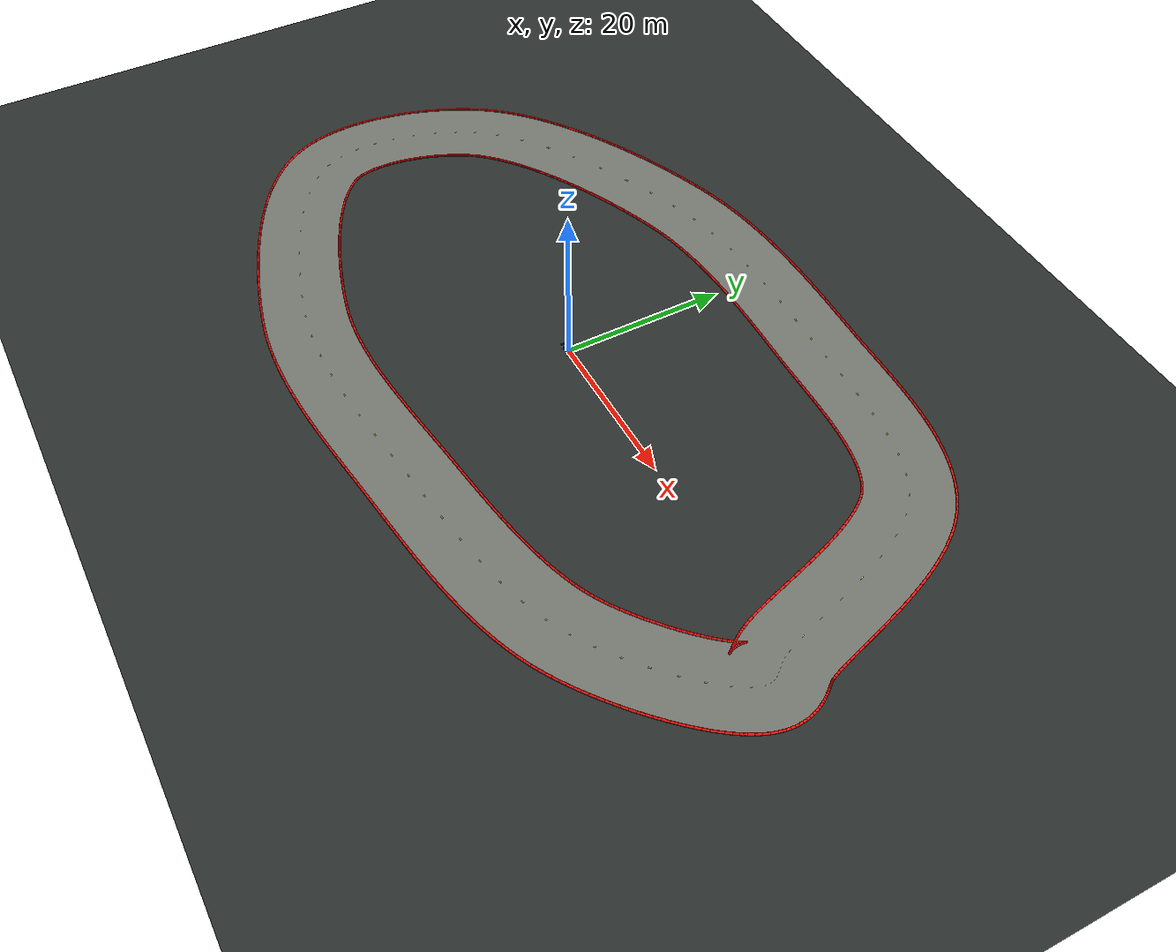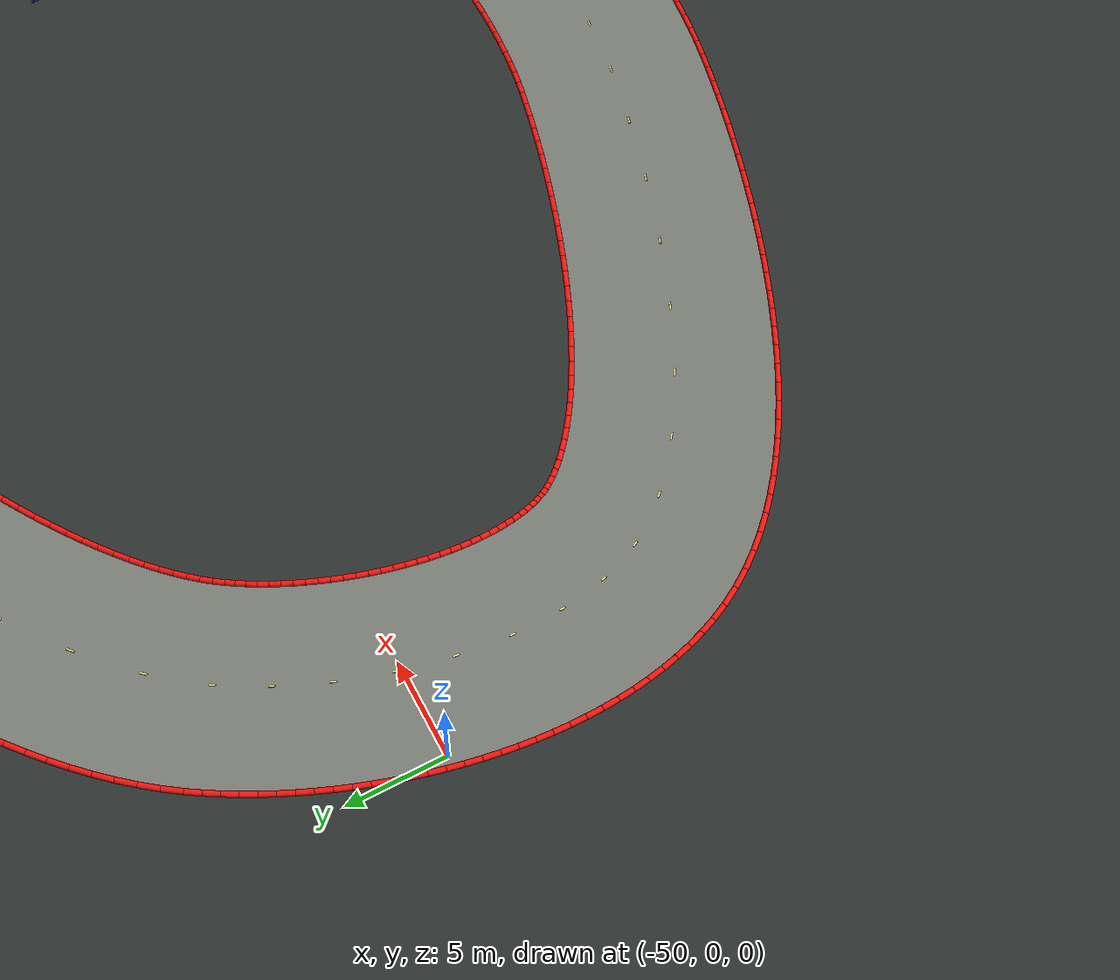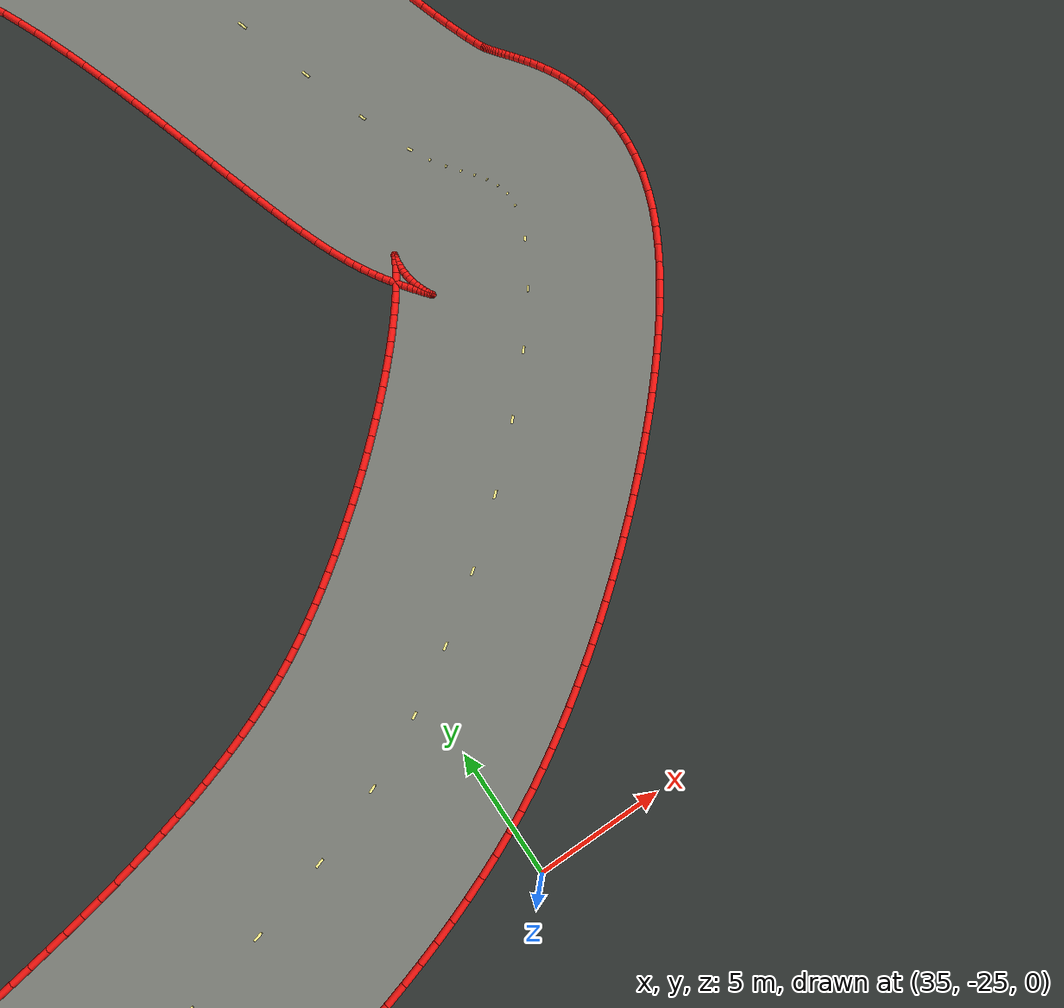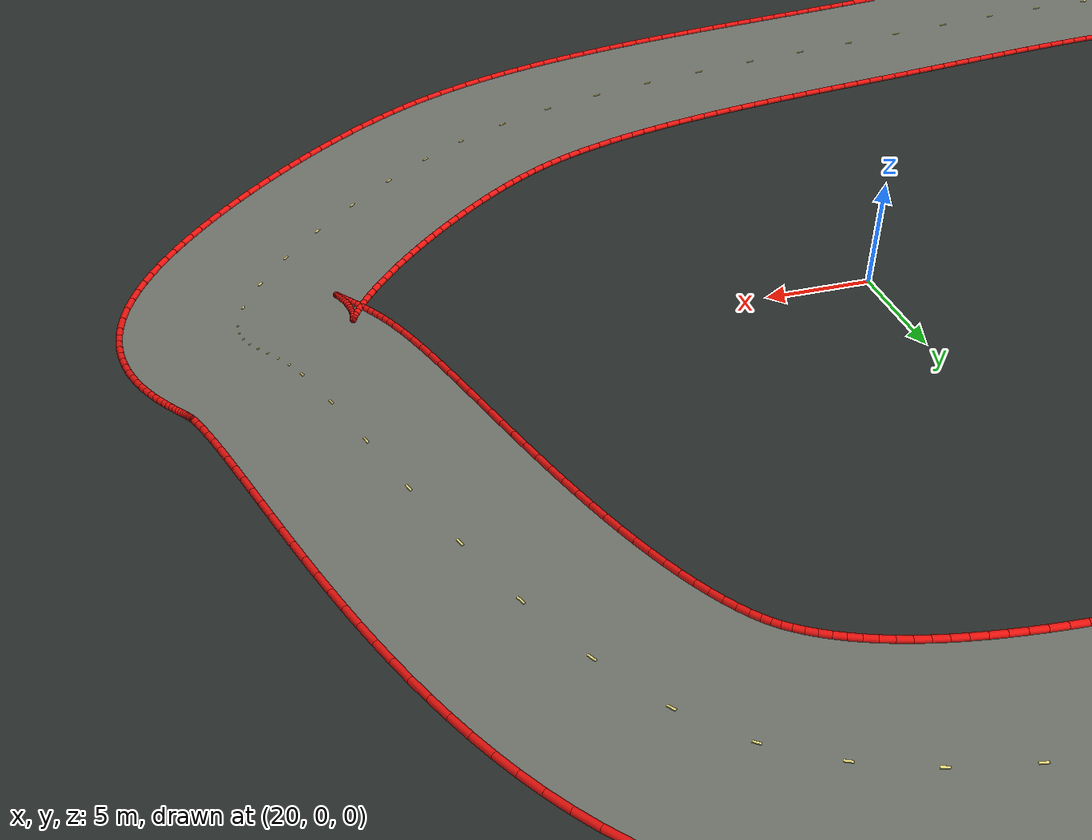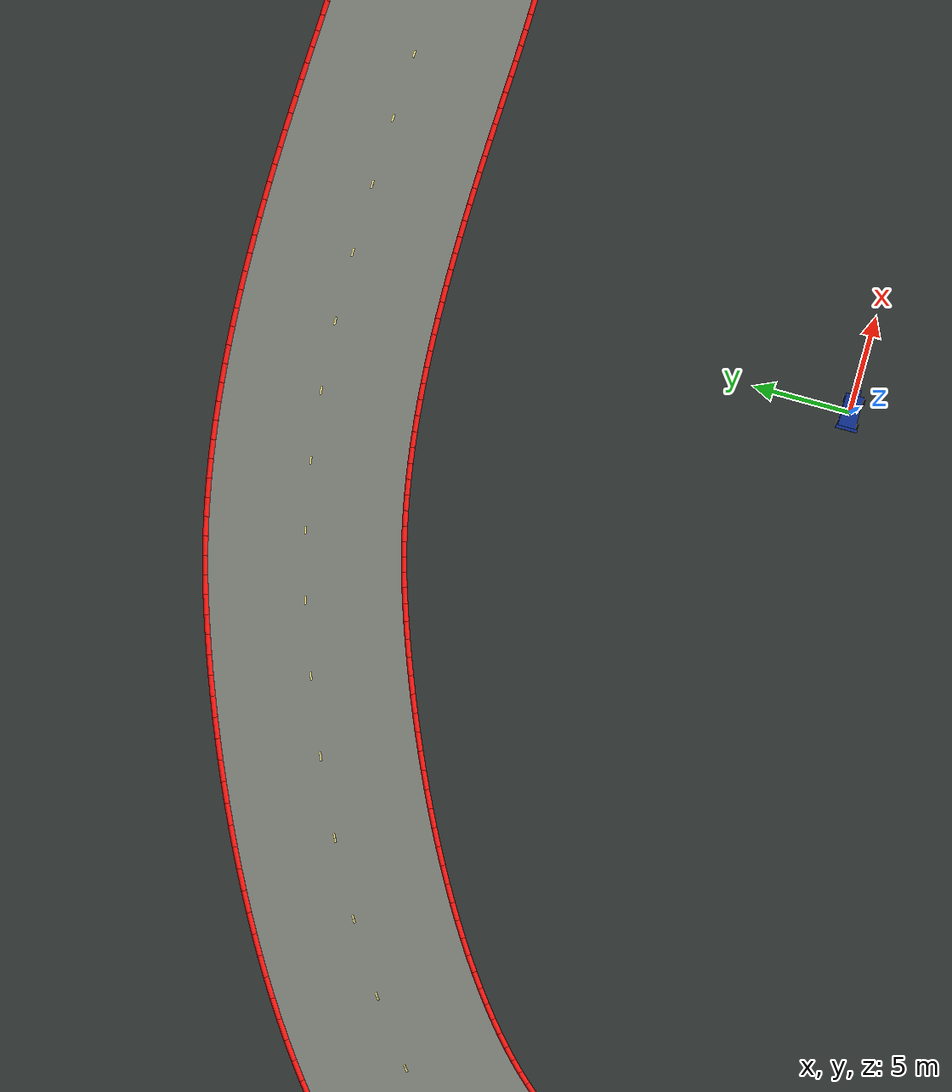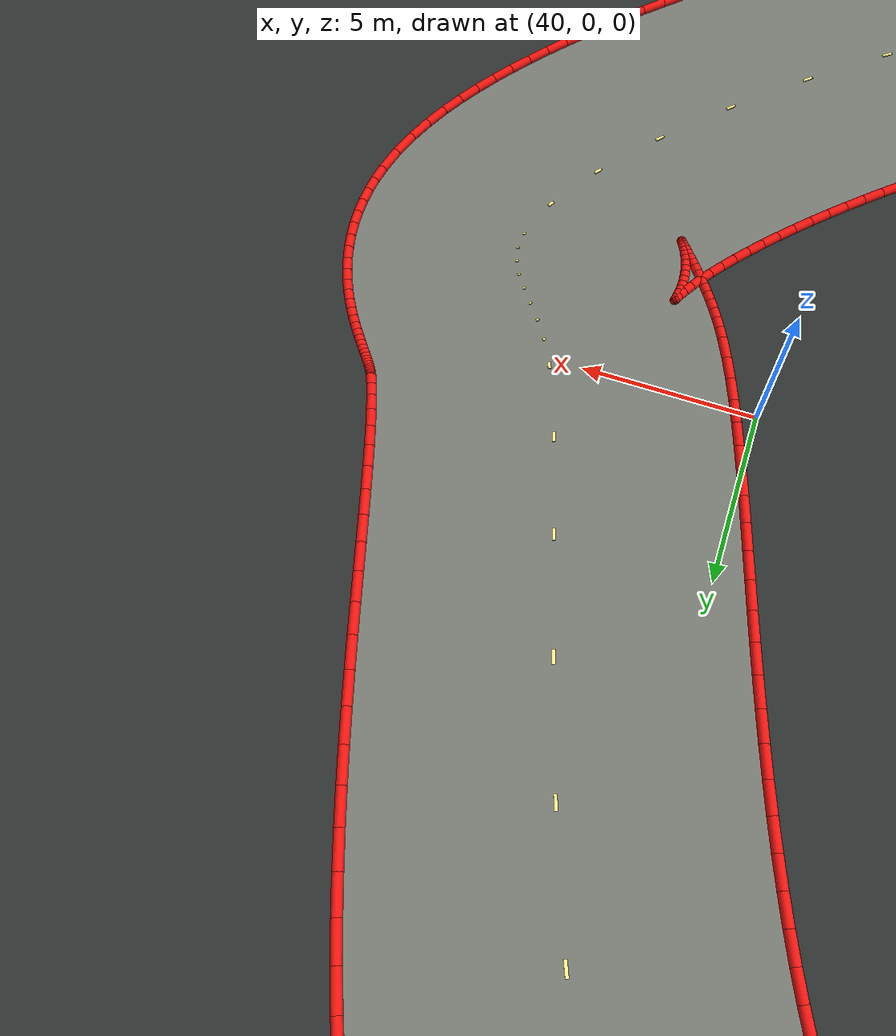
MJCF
<mujoco model="racesim_sweepers_world">
  <compiler angle="degree" autolimits="true"/>
  <option timestep="0.02" gravity="0 0 -9.81"/>
  <visual>
    <global offwidth="1280" offheight="960"/>
    <headlight ambient="0.35 0.35 0.35" diffuse="0.8 0.8 0.8"/>
  </visual>

  <include file="car.xml"/>
  <include file="sweepers_track.xml"/>

  <asset>
    <texture name="grid" type="2d" builtin="checker" width="512" height="512"
             rgb1="0.16 0.18 0.17" rgb2="0.20 0.22 0.21"/>
    <material name="ground" texture="grid" texrepeat="12 12" reflectance="0.05"/>
  </asset>

  <worldbody>
    <light name="sun" pos="0 0 30" dir="0 0 -1" diffuse="1.0 1.0 1.0" ambient="0.25 0.25 0.25"/>
    <geom name="ground" type="plane" size="90 90 0.1" material="ground"/>
    <camera name="topdown" pos="0 0 125" xyaxes="1 0 0 0 1 0" fovy="42"/>
    <camera name="follow" mode="trackcom" target="car" pos="-5 0 3" xyaxes="0 -1 0 0.5 0 0.866"/>
  </worldbody>
</mujoco>

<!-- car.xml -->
<mujoco model="simple_car">
  <default>
    <geom friction="1.2 0.02 0.001" density="600"/>
    <joint damping="0.1"/>
  </default>

  <asset>
    <material name="chassis_blue" rgba="0.05 0.18 0.55 1"/>
    <material name="wheel_dark" rgba="0.02 0.02 0.025 1"/>
  </asset>

  <worldbody>
    <body name="car" pos="0 0 0.28">
      <freejoint name="root"/>
      <geom name="chassis" type="box" size="0.9 0.45 0.12" material="chassis_blue"/>
      <geom name="nose" type="box" pos="0.75 0 0.02" size="0.45 0.25 0.06" material="chassis_blue"/>
      <geom name="rear_wing" type="box" pos="-0.85 0 0.22" size="0.08 0.55 0.04" material="chassis_blue"/>

      <body name="front_left_wheel" pos="0.65 0.48 -0.12">
        <joint name="front_left_spin" type="hinge" axis="0 1 0"/>
        <geom type="cylinder" size="0.18 0.08" euler="90 0 0" material="wheel_dark"/>
      </body>
      <body name="front_right_wheel" pos="0.65 -0.48 -0.12">
        <joint name="front_right_spin" type="hinge" axis="0 1 0"/>
        <geom type="cylinder" size="0.18 0.08" euler="90 0 0" material="wheel_dark"/>
      </body>
      <body name="rear_left_wheel" pos="-0.65 0.48 -0.12">
        <joint name="rear_left_spin" type="hinge" axis="0 1 0"/>
        <geom type="cylinder" size="0.18 0.08" euler="90 0 0" material="wheel_dark"/>
      </body>
      <body name="rear_right_wheel" pos="-0.65 -0.48 -0.12">
        <joint name="rear_right_spin" type="hinge" axis="0 1 0"/>
        <geom type="cylinder" size="0.18 0.08" euler="90 0 0" material="wheel_dark"/>
      </body>
    </body>
  </worldbody>
</mujoco>

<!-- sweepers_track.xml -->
<mujoco model="sweepers_track_visuals">
  <asset>
    <mesh name="track_surface_mesh" inertia="shell" vertex="41.47987 -2.13738 0.02200 41.20917 -1.53661 0.02200 40.95199 -0.90764 0.02200 40.71010 -0.26706 0.02200 40.47738 0.38954 0.02200 40.24982 1.06436 0.02200 40.02463 1.75802 0.02200 39.79980 2.47006 0.02200 39.57377 3.19928 0.02200 39.34535 3.94389 0.02200 39.11355 4.70172 0.02200 38.87754 5.47027 0.02200 38.63663 6.24678 0.02200 38.39024 7.02830 0.02200 38.13787 7.81172 0.02200 37.87911 8.59376 0.02200 37.61367 9.37102 0.02200 37.34133 10.13998 0.02200 37.06198 10.89698 0.02200 36.77567 11.63826 0.02200 36.48260 12.35995 0.02200 36.18316 13.05804 0.02200 35.87798 13.72845 0.02200 35.56798 14.36697 0.02200 35.25447 14.96933 0.02200 34.93919 15.53125 0.02200 34.62442 16.04847 0.02200 34.31308 16.51692 0.02200 34.00882 16.93288 0.02200 33.71608 17.29332 0.02200 33.44001 17.59622 0.02200 33.18626 17.84119 0.02200 32.93530 18.04936 0.02200 32.64064 18.26119 0.02200 32.29969 18.47965 0.02200 31.92934 18.69040 0.02200 31.52852 18.89305 0.02200 31.09672 19.08696 0.02200 30.63395 19.27141 0.02200 30.14065 19.44572 0.02200 29.61762 19.60928 0.02200 29.06592 19.76162 0.02200 28.48683 19.90242 0.02200 27.88176 20.03155 0.02200 27.25222 20.14903 0.02200 26.59976 20.25502 0.02200 25.92596 20.34984 0.02200 25.23240 20.43393 0.02200 24.52062 20.50782 0.02200 23.79217 20.57216 0.02200 23.04852 20.62767 0.02200 22.29113 20.67513 0.02200 21.52139 20.71540 0.02200 20.74068 20.74938 0.02200 19.95028 20.77803 0.02200 19.15145 20.80232 0.02200 18.34541 20.82330 0.02200 17.53331 20.84202 0.02200 16.71624 20.85957 0.02200 15.89525 20.87707 0.02200 15.07134 20.89568 0.02200 14.24543 20.91660 0.02200 13.41839 20.94103 0.02200 12.59103 20.97025 0.02200 11.77688 21.00498 0.02200 10.92699 21.04462 0.02200 10.08430 21.08303 0.02200 9.23840 21.12013 0.02200 8.38973 21.15535 0.02200 7.53874 21.18811 0.02200 6.68588 21.21785 0.02200 5.83162 21.24401 0.02200 4.97645 21.26602 0.02200 4.12086 21.28334 0.02200 3.26534 21.29542 0.02200 2.41040 21.30173 0.02200 1.55656 21.30173 0.02200 0.70434 21.29490 0.02200 -0.14574 21.28072 0.02200 -0.99314 21.25868 0.02200 -1.83731 21.22828 0.02200 -2.67773 21.18903 0.02200 -3.51384 21.14045 0.02200 -4.34510 21.08207 0.02200 -5.17096 21.01343 0.02200 -5.99086 20.93409 0.02200 -6.80427 20.84361 0.02200 -7.61064 20.74157 0.02200 -8.40943 20.62756 0.02200 -9.20013 20.50120 0.02200 -9.98221 20.36211 0.02200 -10.75516 20.20993 0.02200 -11.51852 20.04430 0.02200 -12.27180 19.86490 0.02200 -13.01456 19.67139 0.02200 -13.74641 19.46347 0.02200 -14.47972 19.23673 0.02200 -15.27692 18.97405 0.02200 -16.10360 18.68975 0.02200 -16.94552 18.38814 0.02200 -17.80030 18.06977 0.02200 -18.66561 17.73519 0.02200 -19.53918 17.38494 0.02200 -20.41873 17.01959 0.02200 -21.30203 16.63972 0.02200 -22.18683 16.24590 0.02200 -23.07093 15.83874 0.02200 -23.95210 15.41886 0.02200 -24.82813 14.98688 0.02200 -25.69681 14.54347 0.02200 -26.55591 14.08931 0.02200 -27.40320 13.62512 0.02200 -28.23647 13.15166 0.02200 -29.05345 12.66972 0.02200 -29.85189 12.18017 0.02200 -30.62952 11.68391 0.02200 -31.38406 11.18193 0.02200 -32.11323 10.67531 0.02200 -32.81471 10.16522 0.02200 -33.48622 9.65296 0.02200 -34.12547 9.13996 0.02200 -34.73019 8.62781 0.02200 -35.29816 8.11830 0.02200 -35.82725 7.61341 0.02200 -36.31543 7.11539 0.02200 -36.76086 6.62673 0.02200 -37.16198 6.15020 0.02200 -37.51758 5.68880 0.02200 -37.84220 5.22282 0.02200 -38.09062 4.83324 0.02200 -38.34851 4.40191 0.02200 -38.60154 3.95004 0.02200 -38.84839 3.47942 0.02200 -39.08786 2.99188 0.02200 -39.31886 2.48923 0.02200 -39.54039 1.97328 0.02200 -39.75152 1.44585 0.02200 -39.95140 0.90876 0.02200 -40.13923 0.36382 0.02200 -40.31430 -0.18713 0.02200 -40.47593 -0.74226 0.02200 -40.62349 -1.29971 0.02200 -40.75643 -1.85762 0.02200 -40.87424 -2.41407 0.02200 -40.97648 -2.96716 0.02200 -41.06277 -3.51494 0.02200 -41.13282 -4.05542 0.02200 -41.18640 -4.58659 0.02200 -41.22341 -5.10640 0.02200 -41.24384 -5.61278 0.02200 -41.24781 -6.10362 0.02200 -41.23562 -6.57681 0.02200 -41.20770 -7.03023 0.02200 -41.16472 -7.46180 0.02200 -41.10755 -7.86951 0.02200 -41.03731 -8.25147 0.02200 -40.95537 -8.60598 0.02200 -40.86336 -8.93163 0.02200 -40.76313 -9.22739 0.02200 -40.65668 -9.49276 0.02200 -40.55662 -9.70732 0.02200 -40.41050 -9.96824 0.02200 -40.22855 -10.24002 0.02200 -39.99245 -10.54566 0.02200 -39.70037 -10.87951 0.02200 -39.35220 -11.23599 0.02200 -38.94912 -11.60991 0.02200 -38.49315 -11.99670 0.02200 -37.98690 -12.39239 0.02200 -37.43335 -12.79361 0.02200 -36.83565 -13.19750 0.02200 -36.19706 -13.60167 0.02200 -35.52086 -14.00408 0.02200 -34.81034 -14.40302 0.02200 -34.06876 -14.79704 0.02200 -33.29934 -15.18488 0.02200 -32.50524 -15.56545 0.02200 -31.68958 -15.93782 0.02200 -30.85545 -16.30115 0.02200 -30.00589 -16.65471 0.02200 -29.14390 -16.99785 0.02200 -28.27245 -17.32996 0.02200 -27.39449 -17.65050 0.02200 -26.51295 -17.95896 0.02200 -25.63075 -18.25488 0.02200 -24.75079 -18.53783 0.02200 -23.87597 -18.80739 0.02200 -23.00921 -19.06316 0.02200 -22.15342 -19.30477 0.02200 -21.31157 -19.53187 0.02200 -20.48663 -19.74409 0.02200 -19.68163 -19.94110 0.02200 -18.91754 -20.11858 0.02200 -18.19898 -20.27073 0.02200 -17.48732 -20.40182 0.02200 -16.76387 -20.51644 0.02200 -16.02894 -20.61498 0.02200 -15.28287 -20.69783 0.02200 -14.52606 -20.76542 0.02200 -13.75894 -20.81817 0.02200 -12.98195 -20.85657 0.02200 -12.19557 -20.88109 0.02200 -11.40029 -20.89225 0.02200 -10.59661 -20.89060 0.02200 -9.78505 -20.87668 0.02200 -8.96613 -20.85110 0.02200 -8.14035 -20.81444 0.02200 -7.30823 -20.76734 0.02200 -6.47029 -20.71044 0.02200 -5.62703 -20.64439 0.02200 -4.77894 -20.56988 0.02200 -3.92653 -20.48760 0.02200 -3.07027 -20.39823 0.02200 -2.21063 -20.30250 0.02200 -1.34807 -20.20113 0.02200 -0.48305 -20.09486 0.02200 0.38402 -19.98442 0.02200 1.25270 -19.87056 0.02200 2.12259 -19.75406 0.02200 2.99329 -19.63567 0.02200 3.86443 -19.51618 0.02200 4.73564 -19.39636 0.02200 5.60658 -19.27700 0.02200 6.47693 -19.15892 0.02200 7.34487 -19.04311 0.02200 8.19175 -18.93225 0.02200 9.04139 -18.82245 0.02200 9.89314 -18.71310 0.02200 10.74626 -18.60365 0.02200 11.59994 -18.49353 0.02200 12.45341 -18.38220 0.02200 13.30583 -18.26911 0.02200 14.15638 -18.15375 0.02200 15.00420 -18.03559 0.02200 15.84842 -17.91414 0.02200 16.68816 -17.78889 0.02200 17.52250 -17.65938 0.02200 18.35054 -17.52514 0.02200 19.17134 -17.38571 0.02200 19.98394 -17.24066 0.02200 20.78739 -17.08957 0.02200 21.58071 -16.93205 0.02200 22.36289 -16.76774 0.02200 23.13294 -16.59627 0.02200 23.88984 -16.41733 0.02200 24.63256 -16.23065 0.02200 25.36006 -16.03595 0.02200 26.07131 -15.83305 0.02200 26.76525 -15.62177 0.02200 27.44087 -15.40199 0.02200 28.09713 -15.17364 0.02200 28.73302 -14.93673 0.02200 29.34758 -14.69130 0.02200 29.93988 -14.43746 0.02200 30.50904 -14.17538 0.02200 31.05426 -13.90530 0.02200 31.58384 -13.62254 0.02200 32.03573 -13.36459 0.02200 32.51101 -13.07867 0.02200 33.00021 -12.76999 0.02200 33.50045 -12.44029 0.02200 34.00905 -12.09132 0.02200 34.52350 -11.72483 0.02200 35.04146 -11.34259 0.02200 35.56067 -10.94635 0.02200 36.07895 -10.53786 0.02200 36.59420 -10.11889 0.02200 37.10436 -9.69122 0.02200 37.60742 -9.25664 0.02200 38.10138 -8.81699 0.02200 38.58426 -8.37412 0.02200 39.05406 -7.92994 0.02200 39.50882 -7.48643 0.02200 39.94651 -7.04565 0.02200 40.36512 -6.60975 0.02200 40.76258 -6.18105 0.02200 41.13677 -5.76204 0.02200 41.48553 -5.35544 0.02200 41.80662 -4.96429 0.02200 42.09774 -4.59206 0.02200 42.35651 -4.24280 0.02200 42.58053 -3.92130 0.02200 42.76737 -3.63345 0.02200 42.91479 -3.38660 0.02200 43.02093 -3.19017 0.02200 43.08497 -3.05640 0.02200 43.10817 -3.00132 0.02200 43.09601 -3.04566 0.02200 43.07527 -3.13570 0.02200 43.04712 -3.33065 0.02200 43.03573 -3.48422 0.02200 43.03339 -3.65727 0.02200 43.04257 -3.84408 0.02200 43.06457 -4.03781 0.02200 43.09920 -4.23108 0.02200 43.14470 -4.41658 0.02200 43.19797 -4.58776 0.02200 43.25496 -4.73927 0.02200 43.31117 -4.86730 0.02200 43.36219 -4.96953 0.02200 43.40409 -5.04500 0.02200 43.43364 -5.09379 0.02200 43.44844 -5.11665 0.02200 43.44692 -5.11476 0.02200 43.42820 -5.08946 0.02200 43.39206 -5.04205 0.02200 43.33875 -4.97374 0.02200 43.26893 -4.88556 0.02200 43.18353 -4.77835 0.02200 43.08376 -4.65276 0.02200 42.97096 -4.50927 0.02200 42.84662 -4.34827 0.02200 42.71235 -4.17000 0.02200 42.56981 -3.97470 0.02200 42.42074 -3.76255 0.02200 42.26690 -3.53378 0.02200 42.11004 -3.28864 0.02200 41.95194 -3.02744 0.02200 41.79428 -2.75059 0.02200 41.63871 -2.45856 0.02200 50.52013 2.13738 0.02200 50.39842 2.40770 0.02200 50.25994 2.74778 0.02200 50.10172 3.16768 0.02200 49.92871 3.65641 0.02200 49.74375 4.20526 0.02200 49.54847 4.80705 0.02200 49.34370 5.45569 0.02200 49.12980 6.14585 0.02200 48.90682 6.87276 0.02200 48.67457 7.63205 0.02200 48.43269 8.41969 0.02200 48.18070 9.23186 0.02200 47.91801 10.06499 0.02200 47.64395 10.91564 0.02200 47.35774 11.78055 0.02200 47.05852 12.65656 0.02200 46.74533 13.54067 0.02200 46.41708 14.42997 0.02200 46.07258 15.32168 0.02200 45.71043 16.21314 0.02200 45.32909 17.10179 0.02200 44.92674 17.98519 0.02200 44.50128 18.86099 0.02200 44.05024 19.72691 0.02200 43.57070 20.58071 0.02200 43.05921 21.42008 0.02200 42.51168 22.24255 0.02200 41.92326 23.04530 0.02200 41.28836 23.82482 0.02200 40.60066 24.57656 0.02200 39.85332 25.29440 0.02200 39.06470 25.95064 0.02200 38.27153 26.52515 0.02200 37.47609 27.03563 0.02200 36.66369 27.49869 0.02200 35.83760 27.91701 0.02200 35.00052 28.29350 0.02200 34.15464 28.63116 0.02200 33.30172 28.93296 0.02200 32.44315 29.20180 0.02200 31.58007 29.44041 0.02200 30.71340 29.65139 0.02200 29.84391 29.83716 0.02200 28.97231 29.99998 0.02200 28.09923 30.14196 0.02200 27.22529 30.26507 0.02200 26.35111 30.37116 0.02200 25.47734 30.46195 0.02200 24.60464 30.53910 0.02200 23.73373 30.60417 0.02200 22.86534 30.65863 0.02200 22.00027 30.70393 0.02200 21.13936 30.74143 0.02200 20.28350 30.77247 0.02200 19.43364 30.79834 0.02200 18.59077 30.82029 0.02200 17.75592 30.83954 0.02200 16.93019 30.85728 0.02200 16.11474 30.87466 0.02200 15.31076 30.89282 0.02200 14.51953 30.91284 0.02200 13.74238 30.93578 0.02200 12.98069 30.96265 0.02200 12.22312 30.99502 0.02200 11.38764 31.03400 0.02200 10.53108 31.07304 0.02200 9.66481 31.11104 0.02200 8.78937 31.14736 0.02200 7.90529 31.18139 0.02200 7.01308 31.21250 0.02200 6.11324 31.24004 0.02200 5.20626 31.26338 0.02200 4.29261 31.28186 0.02200 3.37278 31.29484 0.02200 2.44723 31.30166 0.02200 1.51642 31.30165 0.02200 0.58078 31.29414 0.02200 -0.35922 31.27844 0.02200 -1.30317 31.25387 0.02200 -2.25061 31.21974 0.02200 -3.20113 31.17533 0.02200 -4.15430 31.11992 0.02200 -5.10969 31.05280 0.02200 -6.06688 30.97322 0.02200 -7.02545 30.88043 0.02200 -7.98498 30.77366 0.02200 -8.94503 30.65214 0.02200 -9.90516 30.51507 0.02200 -10.86494 30.36165 0.02200 -11.82391 30.19106 0.02200 -12.78160 30.00246 0.02200 -13.73752 29.79500 0.02200 -14.69117 29.56782 0.02200 -15.64202 29.32004 0.02200 -16.58952 29.05079 0.02200 -17.52028 28.76327 0.02200 -18.46717 28.45152 0.02200 -19.41595 28.12523 0.02200 -20.37699 27.78096 0.02200 -21.34873 27.41903 0.02200 -22.32960 27.03977 0.02200 -23.31798 26.64349 0.02200 -24.31222 26.23050 0.02200 -25.31067 25.80109 0.02200 -26.31164 25.35557 0.02200 -27.31345 24.89419 0.02200 -28.31441 24.41721 0.02200 -29.31283 23.92486 0.02200 -30.30701 23.41736 0.02200 -31.29527 22.89490 0.02200 -32.27593 22.35762 0.02200 -33.24732 21.80564 0.02200 -34.20777 21.23903 0.02200 -35.15563 20.65780 0.02200 -36.08928 20.06192 0.02200 -37.00707 19.45126 0.02200 -37.90740 18.82562 0.02200 -38.78866 18.18470 0.02200 -39.64923 17.52807 0.02200 -40.48751 16.85517 0.02200 -41.30184 16.16528 0.02200 -42.09054 15.45748 0.02200 -42.85184 14.73065 0.02200 -43.58385 13.98344 0.02200 -44.28451 13.21420 0.02200 -44.95148 12.42105 0.02200 -45.58206 11.60184 0.02200 -46.15780 10.77718 0.02200 -46.59586 10.09260 0.02200 -47.00301 9.41186 0.02200 -47.39253 8.71642 0.02200 -47.76466 8.00713 0.02200 -48.11950 7.28483 0.02200 -48.45709 6.55036 0.02200 -48.77734 5.80457 0.02200 -49.08010 5.04829 0.02200 -49.36515 4.28236 0.02200 -49.63221 3.50762 0.02200 -49.88092 2.72489 0.02200 -50.11088 1.93499 0.02200 -50.32163 1.13873 0.02200 -50.51267 0.33689 0.02200 -50.68341 -0.46978 0.02200 -50.83322 -1.28053 0.02200 -50.96140 -2.09467 0.02200 -51.06718 -2.91150 0.02200 -51.14968 -3.73040 0.02200 -51.20796 -4.55076 0.02200 -51.24094 -5.37199 0.02200 -51.24741 -6.19354 0.02200 -51.22602 -7.01488 0.02200 -51.17523 -7.83546 0.02200 -51.09331 -8.65470 0.02200 -50.97832 -9.47196 0.02200 -50.82806 -10.28648 0.02200 -50.64007 -11.09731 0.02200 -50.41165 -11.90319 0.02200 -50.13989 -12.70249 0.02200 -49.82170 -13.49307 0.02200 -49.44338 -14.29268 0.02200 -48.93620 -15.19436 0.02200 -48.35527 -16.06724 0.02200 -47.72397 -16.88786 0.02200 -47.04926 -17.66139 0.02200 -46.33631 -18.39296 0.02200 -45.58906 -19.08729 0.02200 -44.81058 -19.74848 0.02200 -44.00332 -20.38005 0.02200 -43.16944 -20.98490 0.02200 -42.31087 -21.56541 0.02200 -41.42943 -22.12353 0.02200 -40.52694 -22.66082 0.02200 -39.60521 -23.17852 0.02200 -38.66606 -23.67763 0.02200 -37.71139 -24.15894 0.02200 -36.74310 -24.62307 0.02200 -35.76318 -25.07049 0.02200 -34.77364 -25.50157 0.02200 -33.77653 -25.91659 0.02200 -32.77394 -26.31573 0.02200 -31.76799 -26.69912 0.02200 -30.76082 -27.06685 0.02200 -29.75461 -27.41896 0.02200 -28.75153 -27.75545 0.02200 -27.75377 -28.07628 0.02200 -26.76351 -28.38142 0.02200 -25.78295 -28.67078 0.02200 -24.81425 -28.94428 0.02200 -23.85955 -29.20181 0.02200 -22.92097 -29.44327 0.02200 -22.00056 -29.66852 0.02200 -21.08246 -29.88142 0.02200 -20.13966 -30.08061 0.02200 -19.17611 -30.25818 0.02200 -18.21131 -30.41113 0.02200 -17.24577 -30.54067 0.02200 -16.27995 -30.64800 0.02200 -15.31428 -30.73430 0.02200 -14.34914 -30.80074 0.02200 -13.38490 -30.84845 0.02200 -12.42188 -30.87853 0.02200 -11.46042 -30.89207 0.02200 -10.50082 -30.89014 0.02200 -9.54339 -30.87376 0.02200 -8.58842 -30.84396 0.02200 -7.63621 -30.80172 0.02200 -6.68706 -30.74803 0.02200 -5.74127 -30.68383 0.02200 -4.79914 -30.61007 0.02200 -3.86100 -30.52766 0.02200 -2.92716 -30.43753 0.02200 -1.99795 -30.34057 0.02200 -1.07372 -30.23766 0.02200 -0.15483 -30.12968 0.02200 0.75837 -30.01750 0.02200 1.66549 -29.90197 0.02200 2.56615 -29.78393 0.02200 3.45993 -29.66423 0.02200 4.34641 -29.54370 0.02200 5.22517 -29.42316 0.02200 6.09575 -29.30343 0.02200 6.95768 -29.18531 0.02200 7.81047 -29.06960 0.02200 8.65513 -28.95689 0.02200 9.48154 -28.84872 0.02200 10.31886 -28.74051 0.02200 11.16605 -28.63176 0.02200 12.02219 -28.52192 0.02200 12.88639 -28.41044 0.02200 13.75776 -28.29677 0.02200 14.63545 -28.18032 0.02200 15.51860 -28.06053 0.02200 16.40641 -27.93679 0.02200 17.29805 -27.80851 0.02200 18.19274 -27.67506 0.02200 19.08971 -27.53581 0.02200 19.98819 -27.39013 0.02200 20.88744 -27.23735 0.02200 21.78673 -27.07681 0.02200 22.68535 -26.90781 0.02200 23.58260 -26.72963 0.02200 24.47779 -26.54154 0.02200 25.37026 -26.34278 0.02200 26.25934 -26.13255 0.02200 27.14438 -25.91004 0.02200 28.02474 -25.67439 0.02200 28.89979 -25.42470 0.02200 29.76888 -25.16002 0.02200 30.63137 -24.87937 0.02200 31.48661 -24.58169 0.02200 32.33393 -24.26590 0.02200 33.17262 -23.93084 0.02200 34.00193 -23.57527 0.02200 34.82106 -23.19793 0.02200 35.62912 -22.79747 0.02200 36.41616 -22.37746 0.02200 37.09052 -21.99297 0.02200 37.75627 -21.59262 0.02200 38.41974 -21.17408 0.02200 39.08075 -20.73850 0.02200 39.73886 -20.28700 0.02200 40.39349 -19.82071 0.02200 41.04389 -19.34077 0.02200 41.68922 -18.84829 0.02200 42.32856 -18.34441 0.02200 42.96091 -17.83024 0.02200 43.58524 -17.30688 0.02200 44.20045 -16.77542 0.02200 44.80547 -16.23691 0.02200 45.39916 -15.69239 0.02200 45.98042 -15.14282 0.02200 46.54814 -14.58911 0.02200 47.10121 -14.03208 0.02200 47.63859 -13.47246 0.02200 48.15922 -12.91081 0.02200 48.66214 -12.34754 0.02200 49.14640 -11.78280 0.02200 49.61116 -11.21642 0.02200 50.05561 -10.64783 0.02200 50.47903 -10.07587 0.02200 50.88074 -9.49862 0.02200 51.26005 -8.91307 0.02200 51.61612 -8.31475 0.02200 51.94770 -7.69714 0.02200 52.25254 -7.05087 0.02200 52.52626 -6.36280 0.02200 52.76028 -5.61508 0.02200 52.92473 -4.86430 0.02200 52.99271 -4.37231 0.02200 53.02562 -3.93390 0.02200 53.03194 -3.48726 0.02200 53.00997 -3.03723 0.02200 52.95917 -2.58971 0.02200 52.88051 -2.15118 0.02200 52.77650 -1.72801 0.02200 52.65102 -1.32588 0.02200 52.50889 -0.94918 0.02200 52.35536 -0.60084 0.02200 52.19561 -0.28224 0.02200 52.03437 0.00657 0.02200 51.87560 0.26656 0.02200 51.72248 0.49943 0.02200 51.57735 0.70726 0.02200 51.44185 0.89230 0.02200 51.31698 1.05678 0.02200 51.20325 1.20281 0.02200 51.10077 1.33234 0.02200 51.00936 1.44712 0.02200 50.92861 1.54873 0.02200 50.85792 1.63856 0.02200 50.79657 1.71789 0.02200 50.74374 1.78791 0.02200 50.69851 1.84975 0.02200 50.65993 1.90452 0.02200 50.62699 1.95336 0.02200 50.59871 1.99743 0.02200 50.57409 2.03797 0.02200 50.55220 2.07629 0.02200 50.53218 2.11378 0.02200" face="0 321 1 0 320 321 1 322 2 1 321 322 2 323 3 2 322 323 3 324 4 3 323 324 4 325 5 4 324 325 5 326 6 5 325 326 6 327 7 6 326 327 7 328 8 7 327 328 8 329 9 8 328 329 9 330 10 9 329 330 10 331 11 10 330 331 11 332 12 11 331 332 12 333 13 12 332 333 13 334 14 13 333 334 14 335 15 14 334 335 15 336 16 15 335 336 16 337 17 16 336 337 17 338 18 17 337 338 18 339 19 18 338 339 19 340 20 19 339 340 20 341 21 20 340 341 21 342 22 21 341 342 22 343 23 22 342 343 23 344 24 23 343 344 24 345 25 24 344 345 25 346 26 25 345 346 26 347 27 26 346 347 27 348 28 27 347 348 28 349 29 28 348 349 29 350 30 29 349 350 30 351 31 30 350 351 31 352 32 31 351 352 32 353 33 32 352 353 33 354 34 33 353 354 34 355 35 34 354 355 35 356 36 35 355 356 36 357 37 36 356 357 37 358 38 37 357 358 38 359 39 38 358 359 39 360 40 39 359 360 40 361 41 40 360 361 41 362 42 41 361 362 42 363 43 42 362 363 43 364 44 43 363 364 44 365 45 44 364 365 45 366 46 45 365 366 46 367 47 46 366 367 47 368 48 47 367 368 48 369 49 48 368 369 49 370 50 49 369 370 50 371 51 50 370 371 51 372 52 51 371 372 52 373 53 52 372 373 53 374 54 53 373 374 54 375 55 54 374 375 55 376 56 55 375 376 56 377 57 56 376 377 57 378 58 57 377 378 58 379 59 58 378 379 59 380 60 59 379 380 60 381 61 60 380 381 61 382 62 61 381 382 62 383 63 62 382 383 63 384 64 63 383 384 64 385 65 64 384 385 65 386 66 65 385 386 66 387 67 66 386 387 67 388 68 67 387 388 68 389 69 68 388 389 69 390 70 69 389 390 70 391 71 70 390 391 71 392 72 71 391 392 72 393 73 72 392 393 73 394 74 73 393 394 74 395 75 74 394 395 75 396 76 75 395 396 76 397 77 76 396 397 77 398 78 77 397 398 78 399 79 78 398 399 79 400 80 79 399 400 80 401 81 80 400 401 81 402 82 81 401 402 82 403 83 82 402 403 83 404 84 83 403 404 84 405 85 84 404 405 85 406 86 85 405 406 86 407 87 86 406 407 87 408 88 87 407 408 88 409 89 88 408 409 89 410 90 89 409 410 90 411 91 90 410 411 91 412 92 91 411 412 92 413 93 92 412 413 93 414 94 93 413 414 94 415 95 94 414 415 95 416 96 95 415 416 96 417 97 96 416 417 97 418 98 97 417 418 98 419 99 98 418 419 99 420 100 99 419 420 100 421 101 100 420 421 101 422 102 101 421 422 102 423 103 102 422 423 103 424 104 103 423 424 104 425 105 104 424 425 105 426 106 105 425 426 106 427 107 106 426 427 107 428 108 107 427 428 108 429 109 108 428 429 109 430 110 109 429 430 110 431 111 110 430 431 111 432 112 111 431 432 112 433 113 112 432 433 113 434 114 113 433 434 114 435 115 114 434 435 115 436 116 115 435 436 116 437 117 116 436 437 117 438 118 117 437 438 118 439 119 118 438 439 119 440 120 119 439 440 120 441 121 120 440 441 121 442 122 121 441 442 122 443 123 122 442 443 123 444 124 123 443 444 124 445 125 124 444 445 125 446 126 125 445 446 126 447 127 126 446 447 127 448 128 127 447 448 128 449 129 128 448 449 129 450 130 129 449 450 130 451 131 130 450 451 131 452 132 131 451 452 132 453 133 132 452 453 133 454 134 133 453 454 134 455 135 134 454 455 135 456 136 135 455 456 136 457 137 136 456 457 137 458 138 137 457 458 138 459 139 138 458 459 139 460 140 139 459 460 140 461 141 140 460 461 141 462 142 141 461 462 142 463 143 142 462 463 143 464 144 143 463 464 144 465 145 144 464 465 145 466 146 145 465 466 146 467 147 146 466 467 147 468 148 147 467 468 148 469 149 148 468 469 149 470 150 149 469 470 150 471 151 150 470 471 151 472 152 151 471 472 152 473 153 152 472 473 153 474 154 153 473 474 154 475 155 154 474 475 155 476 156 155 475 476 156 477 157 156 476 477 157 478 158 157 477 478 158 479 159 158 478 479 159 480 160 159 479 480 160 481 161 160 480 481 161 482 162 161 481 482 162 483 163 162 482 483 163 484 164 163 483 484 164 485 165 164 484 485 165 486 166 165 485 486 166 487 167 166 486 487 167 488 168 167 487 488 168 489 169 168 488 489 169 490 170 169 489 490 170 491 171 170 490 491 171 492 172 171 491 492 172 493 173 172 492 493 173 494 174 173 493 494 174 495 175 174 494 495 175 496 176 175 495 496 176 497 177 176 496 497 177 498 178 177 497 498 178 499 179 178 498 499 179 500 180 179 499 500 180 501 181 180 500 501 181 502 182 181 501 502 182 503 183 182 502 503 183 504 184 183 503 504 184 505 185 184 504 505 185 506 186 185 505 506 186 507 187 186 506 507 187 508 188 187 507 508 188 509 189 188 508 509 189 510 190 189 509 510 190 511 191 190 510 511 191 512 192 191 511 512 192 513 193 192 512 513 193 514 194 193 513 514 194 515 195 194 514 515 195 516 196 195 515 516 196 517 197 196 516 517 197 518 198 197 517 518 198 519 199 198 518 519 199 520 200 199 519 520 200 521 201 200 520 521 201 522 202 201 521 522 202 523 203 202 522 523 203 524 204 203 523 524 204 525 205 204 524 525 205 526 206 205 525 526 206 527 207 206 526 527 207 528 208 207 527 528 208 529 209 208 528 529 209 530 210 209 529 530 210 531 211 210 530 531 211 532 212 211 531 532 212 533 213 212 532 533 213 534 214 213 533 534 214 535 215 214 534 535 215 536 216 215 535 536 216 537 217 216 536 537 217 538 218 217 537 538 218 539 219 218 538 539 219 540 220 219 539 540 220 541 221 220 540 541 221 542 222 221 541 542 222 543 223 222 542 543 223 544 224 223 543 544 224 545 225 224 544 545 225 546 226 225 545 546 226 547 227 226 546 547 227 548 228 227 547 548 228 549 229 228 548 549 229 550 230 229 549 550 230 551 231 230 550 551 231 552 232 231 551 552 232 553 233 232 552 553 233 554 234 233 553 554 234 555 235 234 554 555 235 556 236 235 555 556 236 557 237 236 556 557 237 558 238 237 557 558 238 559 239 238 558 559 239 560 240 239 559 560 240 561 241 240 560 561 241 562 242 241 561 562 242 563 243 242 562 563 243 564 244 243 563 564 244 565 245 244 564 565 245 566 246 245 565 566 246 567 247 246 566 567 247 568 248 247 567 568 248 569 249 248 568 569 249 570 250 249 569 570 250 571 251 250 570 571 251 572 252 251 571 572 252 573 253 252 572 573 253 574 254 253 573 574 254 575 255 254 574 575 255 576 256 255 575 576 256 577 257 256 576 577 257 578 258 257 577 578 258 579 259 258 578 579 259 580 260 259 579 580 260 581 261 260 580 581 261 582 262 261 581 582 262 583 263 262 582 583 263 584 264 263 583 584 264 585 265 264 584 585 265 586 266 265 585 586 266 587 267 266 586 587 267 588 268 267 587 588 268 589 269 268 588 589 269 590 270 269 589 590 270 591 271 270 590 591 271 592 272 271 591 592 272 593 273 272 592 593 273 594 274 273 593 594 274 595 275 274 594 595 275 596 276 275 595 596 276 597 277 276 596 597 277 598 278 277 597 598 278 599 279 278 598 599 279 600 280 279 599 600 280 601 281 280 600 601 281 602 282 281 601 602 282 603 283 282 602 603 283 604 284 283 603 604 284 605 285 284 604 605 285 606 286 285 605 606 286 607 287 286 606 607 287 608 288 287 607 608 288 609 289 288 608 609 289 610 290 289 609 610 290 611 291 290 610 611 291 612 292 291 611 612 292 613 293 292 612 613 293 614 294 293 613 614 294 615 295 294 614 615 295 616 296 295 615 616 296 617 297 296 616 617 297 618 298 297 617 618 298 619 299 298 618 619 299 620 300 299 619 620 300 621 301 300 620 621 301 622 302 301 621 622 302 623 303 302 622 623 303 624 304 303 623 624 304 625 305 304 624 625 305 626 306 305 625 626 306 627 307 306 626 627 307 628 308 307 627 628 308 629 309 308 628 629 309 630 310 309 629 630 310 631 311 310 630 631 311 632 312 311 631 632 312 633 313 312 632 633 313 634 314 313 633 634 314 635 315 314 634 635 315 636 316 315 635 636 316 637 317 316 636 637 317 638 318 317 637 638 318 639 319 318 638 639 319 320 0 319 639 320"/>
    <material name="track_asphalt" rgba="0.48 0.49 0.46 1" emission="0.08"/>
    <material name="track_boundary" rgba="0.95 0.08 0.06 1" emission="0.05"/>
    <material name="track_centerline" rgba="1.0 0.95 0.55 1" emission="0.15"/>
  </asset>
  <worldbody>
    <geom name="track_surface" type="mesh" mesh="track_surface_mesh" material="track_asphalt" contype="0" conaffinity="0"/>
    <geom name="track_left_boundary_000" type="capsule" fromto="41.47987 -2.13738 0.09 41.20917 -1.53661 0.09" size="0.14" material="track_boundary" contype="0" conaffinity="0"/>
    <geom name="track_left_boundary_001" type="capsule" fromto="41.20917 -1.53661 0.09 40.95199 -0.90764 0.09" size="0.14" material="track_boundary" contype="0" conaffinity="0"/>
    <geom name="track_left_boundary_002" type="capsule" fromto="40.95199 -0.90764 0.09 40.71010 -0.26706 0.09" size="0.14" material="track_boundary" contype="0" conaffinity="0"/>
    <geom name="track_left_boundary_003" type="capsule" fromto="40.71010 -0.26706 0.09 40.47738 0.38954 0.09" size="0.14" material="track_boundary" contype="0" conaffinity="0"/>
    <geom name="track_left_boundary_004" type="capsule" fromto="40.47738 0.38954 0.09 40.24982 1.06436 0.09" size="0.14" material="track_boundary" contype="0" conaffinity="0"/>
    <geom name="track_left_boundary_005" type="capsule" fromto="40.24982 1.06436 0.09 40.02463 1.75802 0.09" size="0.14" material="track_boundary" contype="0" conaffinity="0"/>
    <geom name="track_left_boundary_006" type="capsule" fromto="40.02463 1.75802 0.09 39.79980 2.47006 0.09" size="0.14" material="track_boundary" contype="0" conaffinity="0"/>
    <geom name="track_left_boundary_007" type="capsule" fromto="39.79980 2.47006 0.09 39.57377 3.19928 0.09" size="0.14" material="track_boundary" contype="0" conaffinity="0"/>
    <geom name="track_left_boundary_008" type="capsule" fromto="39.57377 3.19928 0.09 39.34535 3.94389 0.09" size="0.14" material="track_boundary" contype="0" conaffinity="0"/>
    <geom name="track_left_boundary_009" type="capsule" fromto="39.34535 3.94389 0.09 39.11355 4.70172 0.09" size="0.14" material="track_boundary" contype="0" conaffinity="0"/>
    <geom name="track_left_boundary_010" type="capsule" fromto="39.11355 4.70172 0.09 38.87754 5.47027 0.09" size="0.14" material="track_boundary" contype="0" conaffinity="0"/>
    <geom name="track_left_boundary_011" type="capsule" fromto="38.87754 5.47027 0.09 38.63663 6.24678 0.09" size="0.14" material="track_boundary" contype="0" conaffinity="0"/>
    <geom name="track_left_boundary_012" type="capsule" fromto="38.63663 6.24678 0.09 38.39024 7.02830 0.09" size="0.14" material="track_boundary" contype="0" conaffinity="0"/>
    <geom name="track_left_boundary_013" type="capsule" fromto="38.39024 7.02830 0.09 38.13787 7.81172 0.09" size="0.14" material="track_boundary" contype="0" conaffinity="0"/>
    <geom name="track_left_boundary_014" type="capsule" fromto="38.13787 7.81172 0.09 37.87911 8.59376 0.09" size="0.14" material="track_boundary" contype="0" conaffinity="0"/>
    <geom name="track_left_boundary_015" type="capsule" fromto="37.87911 8.59376 0.09 37.61367 9.37102 0.09" size="0.14" material="track_boundary" contype="0" conaffinity="0"/>
    <geom name="track_left_boundary_016" type="capsule" fromto="37.61367 9.37102 0.09 37.34133 10.13998 0.09" size="0.14" material="track_boundary" contype="0" conaffinity="0"/>
    <geom name="track_left_boundary_017" type="capsule" fromto="37.34133 10.13998 0.09 37.06198 10.89698 0.09" size="0.14" material="track_boundary" contype="0" conaffinity="0"/>
    <geom name="track_left_boundary_018" type="capsule" fromto="37.06198 10.89698 0.09 36.77567 11.63826 0.09" size="0.14" material="track_boundary" contype="0" conaffinity="0"/>
    <geom name="track_left_boundary_019" type="capsule" fromto="36.77567 11.63826 0.09 36.48260 12.35995 0.09" size="0.14" material="track_boundary" contype="0" conaffinity="0"/>
    <geom name="track_left_boundary_020" type="capsule" fromto="36.48260 12.35995 0.09 36.18316 13.05804 0.09" size="0.14" material="track_boundary" contype="0" conaffinity="0"/>
    <geom name="track_left_boundary_021" type="capsule" fromto="36.18316 13.05804 0.09 35.87798 13.72845 0.09" size="0.14" material="track_boundary" contype="0" conaffinity="0"/>
    <geom name="track_left_boundary_022" type="capsule" fromto="35.87798 13.72845 0.09 35.56798 14.36697 0.09" size="0.14" material="track_boundary" contype="0" conaffinity="0"/>
    <geom name="track_left_boundary_023" type="capsule" fromto="35.56798 14.36697 0.09 35.25447 14.96933 0.09" size="0.14" material="track_boundary" contype="0" conaffinity="0"/>
    <geom name="track_left_boundary_024" type="capsule" fromto="35.25447 14.96933 0.09 34.93919 15.53125 0.09" size="0.14" material="track_boundary" contype="0" conaffinity="0"/>
    <geom name="track_left_boundary_025" type="capsule" fromto="34.93919 15.53125 0.09 34.62442 16.04847 0.09" size="0.14" material="track_boundary" contype="0" conaffinity="0"/>
    <geom name="track_left_boundary_026" type="capsule" fromto="34.62442 16.04847 0.09 34.31308 16.51692 0.09" size="0.14" material="track_boundary" contype="0" conaffinity="0"/>
    <geom name="track_left_boundary_027" type="capsule" fromto="34.31308 16.51692 0.09 34.00882 16.93288 0.09" size="0.14" material="track_boundary" contype="0" conaffinity="0"/>
    <geom name="track_left_boundary_028" type="capsule" fromto="34.00882 16.93288 0.09 33.71608 17.29332 0.09" size="0.14" material="track_boundary" contype="0" conaffinity="0"/>
    <geom name="track_left_boundary_029" type="capsule" fromto="33.71608 17.29332 0.09 33.44001 17.59622 0.09" size="0.14" material="track_boundary" contype="0" conaffinity="0"/>
    <geom name="track_left_boundary_030" type="capsule" fromto="33.44001 17.59622 0.09 33.18626 17.84119 0.09" size="0.14" material="track_boundary" contype="0" conaffinity="0"/>
    <geom name="track_left_boundary_031" type="capsule" fromto="33.18626 17.84119 0.09 32.93530 18.04936 0.09" size="0.14" material="track_boundary" contype="0" conaffinity="0"/>
    <geom name="track_left_boundary_032" type="capsule" fromto="32.93530 18.04936 0.09 32.64064 18.26119 0.09" size="0.14" material="track_boundary" contype="0" conaffinity="0"/>
    <geom name="track_left_boundary_033" type="capsule" fromto="32.64064 18.26119 0.09 32.29969 18.47965 0.09" size="0.14" material="track_boundary" contype="0" conaffinity="0"/>
    <geom name="track_left_boundary_034" type="capsule" fromto="32.29969 18.47965 0.09 31.92934 18.69040 0.09" size="0.14" material="track_boundary" contype="0" conaffinity="0"/>
    <geom name="track_left_boundary_035" type="capsule" fromto="31.92934 18.69040 0.09 31.52852 18.89305 0.09" size="0.14" material="track_boundary" contype="0" conaffinity="0"/>
    <geom name="track_left_boundary_036" type="capsule" fromto="31.52852 18.89305 0.09 31.09672 19.08696 0.09" size="0.14" material="track_boundary" contype="0" conaffinity="0"/>
    <geom name="track_left_boundary_037" type="capsule" fromto="31.09672 19.08696 0.09 30.63395 19.27141 0.09" size="0.14" material="track_boundary" contype="0" conaffinity="0"/>
    <geom name="track_left_boundary_038" type="capsule" fromto="30.63395 19.27141 0.09 30.14065 19.44572 0.09" size="0.14" material="track_boundary" contype="0" conaffinity="0"/>
    <geom name="track_left_boundary_039" type="capsule" fromto="30.14065 19.44572 0.09 29.61762 19.60928 0.09" size="0.14" material="track_boundary" contype="0" conaffinity="0"/>
    <geom name="track_left_boundary_040" type="capsule" fromto="29.61762 19.60928 0.09 29.06592 19.76162 0.09" size="0.14" material="track_boundary" contype="0" conaffinity="0"/>
    <geom name="track_left_boundary_041" type="capsule" fromto="29.06592 19.76162 0.09 28.48683 19.90242 0.09" size="0.14" material="track_boundary" contype="0" conaffinity="0"/>
    <geom name="track_left_boundary_042" type="capsule" fromto="28.48683 19.90242 0.09 27.88176 20.03155 0.09" size="0.14" material="track_boundary" contype="0" conaffinity="0"/>
    <geom name="track_left_boundary_043" type="capsule" fromto="27.88176 20.03155 0.09 27.25222 20.14903 0.09" size="0.14" material="track_boundary" contype="0" conaffinity="0"/>
    <geom name="track_left_boundary_044" type="capsule" fromto="27.25222 20.14903 0.09 26.59976 20.25502 0.09" size="0.14" material="track_boundary" contype="0" conaffinity="0"/>
    <geom name="track_left_boundary_045" type="capsule" fromto="26.59976 20.25502 0.09 25.92596 20.34984 0.09" size="0.14" material="track_boundary" contype="0" conaffinity="0"/>
    <geom name="track_left_boundary_046" type="capsule" fromto="25.92596 20.34984 0.09 25.23240 20.43393 0.09" size="0.14" material="track_boundary" contype="0" conaffinity="0"/>
    <geom name="track_left_boundary_047" type="capsule" fromto="25.23240 20.43393 0.09 24.52062 20.50782 0.09" size="0.14" material="track_boundary" contype="0" conaffinity="0"/>
    <geom name="track_left_boundary_048" type="capsule" fromto="24.52062 20.50782 0.09 23.79217 20.57216 0.09" size="0.14" material="track_boundary" contype="0" conaffinity="0"/>
    <geom name="track_left_boundary_049" type="capsule" fromto="23.79217 20.57216 0.09 23.04852 20.62767 0.09" size="0.14" material="track_boundary" contype="0" conaffinity="0"/>
    <geom name="track_left_boundary_050" type="capsule" fromto="23.04852 20.62767 0.09 22.29113 20.67513 0.09" size="0.14" material="track_boundary" contype="0" conaffinity="0"/>
    <geom name="track_left_boundary_051" type="capsule" fromto="22.29113 20.67513 0.09 21.52139 20.71540 0.09" size="0.14" material="track_boundary" contype="0" conaffinity="0"/>
    <geom name="track_left_boundary_052" type="capsule" fromto="21.52139 20.71540 0.09 20.74068 20.74938 0.09" size="0.14" material="track_boundary" contype="0" conaffinity="0"/>
    <geom name="track_left_boundary_053" type="capsule" fromto="20.74068 20.74938 0.09 19.95028 20.77803 0.09" size="0.14" material="track_boundary" contype="0" conaffinity="0"/>
    <geom name="track_left_boundary_054" type="capsule" fromto="19.95028 20.77803 0.09 19.15145 20.80232 0.09" size="0.14" material="track_boundary" contype="0" conaffinity="0"/>
    <geom name="track_left_boundary_055" type="capsule" fromto="19.15145 20.80232 0.09 18.34541 20.82330 0.09" size="0.14" material="track_boundary" contype="0" conaffinity="0"/>
    <geom name="track_left_boundary_056" type="capsule" fromto="18.34541 20.82330 0.09 17.53331 20.84202 0.09" size="0.14" material="track_boundary" contype="0" conaffinity="0"/>
    <geom name="track_left_boundary_057" type="capsule" fromto="17.53331 20.84202 0.09 16.71624 20.85957 0.09" size="0.14" material="track_boundary" contype="0" conaffinity="0"/>
    <geom name="track_left_boundary_058" type="capsule" fromto="16.71624 20.85957 0.09 15.89525 20.87707 0.09" size="0.14" material="track_boundary" contype="0" conaffinity="0"/>
    <geom name="track_left_boundary_059" type="capsule" fromto="15.89525 20.87707 0.09 15.07134 20.89568 0.09" size="0.14" material="track_boundary" contype="0" conaffinity="0"/>
    <geom name="track_left_boundary_060" type="capsule" fromto="15.07134 20.89568 0.09 14.24543 20.91660 0.09" size="0.14" material="track_boundary" contype="0" conaffinity="0"/>
    <geom name="track_left_boundary_061" type="capsule" fromto="14.24543 20.91660 0.09 13.41839 20.94103 0.09" size="0.14" material="track_boundary" contype="0" conaffinity="0"/>
    <geom name="track_left_boundary_062" type="capsule" fromto="13.41839 20.94103 0.09 12.59103 20.97025 0.09" size="0.14" material="track_boundary" contype="0" conaffinity="0"/>
    <geom name="track_left_boundary_063" type="capsule" fromto="12.59103 20.97025 0.09 11.77688 21.00498 0.09" size="0.14" material="track_boundary" contype="0" conaffinity="0"/>
    <geom name="track_left_boundary_064" type="capsule" fromto="11.77688 21.00498 0.09 10.92699 21.04462 0.09" size="0.14" material="track_boundary" contype="0" conaffinity="0"/>
    <geom name="track_left_boundary_065" type="capsule" fromto="10.92699 21.04462 0.09 10.08430 21.08303 0.09" size="0.14" material="track_boundary" contype="0" conaffinity="0"/>
    <geom name="track_left_boundary_066" type="capsule" fromto="10.08430 21.08303 0.09 9.23840 21.12013 0.09" size="0.14" material="track_boundary" contype="0" conaffinity="0"/>
    <geom name="track_left_boundary_067" type="capsule" fromto="9.23840 21.12013 0.09 8.38973 21.15535 0.09" size="0.14" material="track_boundary" contype="0" conaffinity="0"/>
    <geom name="track_left_boundary_068" type="capsule" fromto="8.38973 21.15535 0.09 7.53874 21.18811 0.09" size="0.14" material="track_boundary" contype="0" conaffinity="0"/>
    <geom name="track_left_boundary_069" type="capsule" fromto="7.53874 21.18811 0.09 6.68588 21.21785 0.09" size="0.14" material="track_boundary" contype="0" conaffinity="0"/>
    <geom name="track_left_boundary_070" type="capsule" fromto="6.68588 21.21785 0.09 5.83162 21.24401 0.09" size="0.14" material="track_boundary" contype="0" conaffinity="0"/>
    <geom name="track_left_boundary_071" type="capsule" fromto="5.83162 21.24401 0.09 4.97645 21.26602 0.09" size="0.14" material="track_boundary" contype="0" conaffinity="0"/>
    <geom name="track_left_boundary_072" type="capsule" fromto="4.97645 21.26602 0.09 4.12086 21.28334 0.09" size="0.14" material="track_boundary" contype="0" conaffinity="0"/>
    <geom name="track_left_boundary_073" type="capsule" fromto="4.12086 21.28334 0.09 3.26534 21.29542 0.09" size="0.14" material="track_boundary" contype="0" conaffinity="0"/>
    <geom name="track_left_boundary_074" type="capsule" fromto="3.26534 21.29542 0.09 2.41040 21.30173 0.09" size="0.14" material="track_boundary" contype="0" conaffinity="0"/>
    <geom name="track_left_boundary_075" type="capsule" fromto="2.41040 21.30173 0.09 1.55656 21.30173 0.09" size="0.14" material="track_boundary" contype="0" conaffinity="0"/>
    <geom name="track_left_boundary_076" type="capsule" fromto="1.55656 21.30173 0.09 0.70434 21.29490 0.09" size="0.14" material="track_boundary" contype="0" conaffinity="0"/>
    <geom name="track_left_boundary_077" type="capsule" fromto="0.70434 21.29490 0.09 -0.14574 21.28072 0.09" size="0.14" material="track_boundary" contype="0" conaffinity="0"/>
    <geom name="track_left_boundary_078" type="capsule" fromto="-0.14574 21.28072 0.09 -0.99314 21.25868 0.09" size="0.14" material="track_boundary" contype="0" conaffinity="0"/>
    <geom name="track_left_boundary_079" type="capsule" fromto="-0.99314 21.25868 0.09 -1.83731 21.22828 0.09" size="0.14" material="track_boundary" contype="0" conaffinity="0"/>
    <geom name="track_left_boundary_080" type="capsule" fromto="-1.83731 21.22828 0.09 -2.67773 21.18903 0.09" size="0.14" material="track_boundary" contype="0" conaffinity="0"/>
    <geom name="track_left_boundary_081" type="capsule" fromto="-2.67773 21.18903 0.09 -3.51384 21.14045 0.09" size="0.14" material="track_boundary" contype="0" conaffinity="0"/>
    <geom name="track_left_boundary_082" type="capsule" fromto="-3.51384 21.14045 0.09 -4.34510 21.08207 0.09" size="0.14" material="track_boundary" contype="0" conaffinity="0"/>
    <geom name="track_left_boundary_083" type="capsule" fromto="-4.34510 21.08207 0.09 -5.17096 21.01343 0.09" size="0.14" material="track_boundary" contype="0" conaffinity="0"/>
    <geom name="track_left_boundary_084" type="capsule" fromto="-5.17096 21.01343 0.09 -5.99086 20.93409 0.09" size="0.14" material="track_boundary" contype="0" conaffinity="0"/>
    <geom name="track_left_boundary_085" type="capsule" fromto="-5.99086 20.93409 0.09 -6.80427 20.84361 0.09" size="0.14" material="track_boundary" contype="0" conaffinity="0"/>
    <geom name="track_left_boundary_086" type="capsule" fromto="-6.80427 20.84361 0.09 -7.61064 20.74157 0.09" size="0.14" material="track_boundary" contype="0" conaffinity="0"/>
    <geom name="track_left_boundary_087" type="capsule" fromto="-7.61064 20.74157 0.09 -8.40943 20.62756 0.09" size="0.14" material="track_boundary" contype="0" conaffinity="0"/>
    <geom name="track_left_boundary_088" type="capsule" fromto="-8.40943 20.62756 0.09 -9.20013 20.50120 0.09" size="0.14" material="track_boundary" contype="0" conaffinity="0"/>
    <geom name="track_left_boundary_089" type="capsule" fromto="-9.20013 20.50120 0.09 -9.98221 20.36211 0.09" size="0.14" material="track_boundary" contype="0" conaffinity="0"/>
    <geom name="track_left_boundary_090" type="capsule" fromto="-9.98221 20.36211 0.09 -10.75516 20.20993 0.09" size="0.14" material="track_boundary" contype="0" conaffinity="0"/>
    <geom name="track_left_boundary_091" type="capsule" fromto="-10.75516 20.20993 0.09 -11.51852 20.04430 0.09" size="0.14" material="track_boundary" contype="0" conaffinity="0"/>
    <geom name="track_left_boundary_092" type="capsule" fromto="-11.51852 20.04430 0.09 -12.27180 19.86490 0.09" size="0.14" material="track_boundary" contype="0" conaffinity="0"/>
    <geom name="track_left_boundary_093" type="capsule" fromto="-12.27180 19.86490 0.09 -13.01456 19.67139 0.09" size="0.14" material="track_boundary" contype="0" conaffinity="0"/>
    <geom name="track_left_boundary_094" type="capsule" fromto="-13.01456 19.67139 0.09 -13.74641 19.46347 0.09" size="0.14" material="track_boundary" contype="0" conaffinity="0"/>
    <geom name="track_left_boundary_095" type="capsule" fromto="-13.74641 19.46347 0.09 -14.47972 19.23673 0.09" size="0.14" material="track_boundary" contype="0" conaffinity="0"/>
    <geom name="track_left_boundary_096" type="capsule" fromto="-14.47972 19.23673 0.09 -15.27692 18.97405 0.09" size="0.14" material="track_boundary" contype="0" conaffinity="0"/>
    <geom name="track_left_boundary_097" type="capsule" fromto="-15.27692 18.97405 0.09 -16.10360 18.68975 0.09" size="0.14" material="track_boundary" contype="0" conaffinity="0"/>
    <geom name="track_left_boundary_098" type="capsule" fromto="-16.10360 18.68975 0.09 -16.94552 18.38814 0.09" size="0.14" material="track_boundary" contype="0" conaffinity="0"/>
    <geom name="track_left_boundary_099" type="capsule" fromto="-16.94552 18.38814 0.09 -17.80030 18.06977 0.09" size="0.14" material="track_boundary" contype="0" conaffinity="0"/>
    <geom name="track_left_boundary_100" type="capsule" fromto="-17.80030 18.06977 0.09 -18.66561 17.73519 0.09" size="0.14" material="track_boundary" contype="0" conaffinity="0"/>
    <geom name="track_left_boundary_101" type="capsule" fromto="-18.66561 17.73519 0.09 -19.53918 17.38494 0.09" size="0.14" material="track_boundary" contype="0" conaffinity="0"/>
    <geom name="track_left_boundary_102" type="capsule" fromto="-19.53918 17.38494 0.09 -20.41873 17.01959 0.09" size="0.14" material="track_boundary" contype="0" conaffinity="0"/>
    <geom name="track_left_boundary_103" type="capsule" fromto="-20.41873 17.01959 0.09 -21.30203 16.63972 0.09" size="0.14" material="track_boundary" contype="0" conaffinity="0"/>
    <geom name="track_left_boundary_104" type="capsule" fromto="-21.30203 16.63972 0.09 -22.18683 16.24590 0.09" size="0.14" material="track_boundary" contype="0" conaffinity="0"/>
    <geom name="track_left_boundary_105" type="capsule" fromto="-22.18683 16.24590 0.09 -23.07093 15.83874 0.09" size="0.14" material="track_boundary" contype="0" conaffinity="0"/>
    <geom name="track_left_boundary_106" type="capsule" fromto="-23.07093 15.83874 0.09 -23.95210 15.41886 0.09" size="0.14" material="track_boundary" contype="0" conaffinity="0"/>
    <geom name="track_left_boundary_107" type="capsule" fromto="-23.95210 15.41886 0.09 -24.82813 14.98688 0.09" size="0.14" material="track_boundary" contype="0" conaffinity="0"/>
    <geom name="track_left_boundary_108" type="capsule" fromto="-24.82813 14.98688 0.09 -25.69681 14.54347 0.09" size="0.14" material="track_boundary" contype="0" conaffinity="0"/>
    <geom name="track_left_boundary_109" type="capsule" fromto="-25.69681 14.54347 0.09 -26.55591 14.08931 0.09" size="0.14" material="track_boundary" contype="0" conaffinity="0"/>
    <geom name="track_left_boundary_110" type="capsule" fromto="-26.55591 14.08931 0.09 -27.40320 13.62512 0.09" size="0.14" material="track_boundary" contype="0" conaffinity="0"/>
    <geom name="track_left_boundary_111" type="capsule" fromto="-27.40320 13.62512 0.09 -28.23647 13.15166 0.09" size="0.14" material="track_boundary" contype="0" conaffinity="0"/>
    <geom name="track_left_boundary_112" type="capsule" fromto="-28.23647 13.15166 0.09 -29.05345 12.66972 0.09" size="0.14" material="track_boundary" contype="0" conaffinity="0"/>
    <geom name="track_left_boundary_113" type="capsule" fromto="-29.05345 12.66972 0.09 -29.85189 12.18017 0.09" size="0.14" material="track_boundary" contype="0" conaffinity="0"/>
    <geom name="track_left_boundary_114" type="capsule" fromto="-29.85189 12.18017 0.09 -30.62952 11.68391 0.09" size="0.14" material="track_boundary" contype="0" conaffinity="0"/>
    <geom name="track_left_boundary_115" type="capsule" fromto="-30.62952 11.68391 0.09 -31.38406 11.18193 0.09" size="0.14" material="track_boundary" contype="0" conaffinity="0"/>
    <geom name="track_left_boundary_116" type="capsule" fromto="-31.38406 11.18193 0.09 -32.11323 10.67531 0.09" size="0.14" material="track_boundary" contype="0" conaffinity="0"/>
    <geom name="track_left_boundary_117" type="capsule" fromto="-32.11323 10.67531 0.09 -32.81471 10.16522 0.09" size="0.14" material="track_boundary" contype="0" conaffinity="0"/>
    <geom name="track_left_boundary_118" type="capsule" fromto="-32.81471 10.16522 0.09 -33.48622 9.65296 0.09" size="0.14" material="track_boundary" contype="0" conaffinity="0"/>
    <geom name="track_left_boundary_119" type="capsule" fromto="-33.48622 9.65296 0.09 -34.12547 9.13996 0.09" size="0.14" material="track_boundary" contype="0" conaffinity="0"/>
    <geom name="track_left_boundary_120" type="capsule" fromto="-34.12547 9.13996 0.09 -34.73019 8.62781 0.09" size="0.14" material="track_boundary" contype="0" conaffinity="0"/>
    <geom name="track_left_boundary_121" type="capsule" fromto="-34.73019 8.62781 0.09 -35.29816 8.11830 0.09" size="0.14" material="track_boundary" contype="0" conaffinity="0"/>
    <geom name="track_left_boundary_122" type="capsule" fromto="-35.29816 8.11830 0.09 -35.82725 7.61341 0.09" size="0.14" material="track_boundary" contype="0" conaffinity="0"/>
    <geom name="track_left_boundary_123" type="capsule" fromto="-35.82725 7.61341 0.09 -36.31543 7.11539 0.09" size="0.14" material="track_boundary" contype="0" conaffinity="0"/>
    <geom name="track_left_boundary_124" type="capsule" fromto="-36.31543 7.11539 0.09 -36.76086 6.62673 0.09" size="0.14" material="track_boundary" contype="0" conaffinity="0"/>
    <geom name="track_left_boundary_125" type="capsule" fromto="-36.76086 6.62673 0.09 -37.16198 6.15020 0.09" size="0.14" material="track_boundary" contype="0" conaffinity="0"/>
    <geom name="track_left_boundary_126" type="capsule" fromto="-37.16198 6.15020 0.09 -37.51758 5.68880 0.09" size="0.14" material="track_boundary" contype="0" conaffinity="0"/>
    <geom name="track_left_boundary_127" type="capsule" fromto="-37.51758 5.68880 0.09 -37.84220 5.22282 0.09" size="0.14" material="track_boundary" contype="0" conaffinity="0"/>
    <geom name="track_left_boundary_128" type="capsule" fromto="-37.84220 5.22282 0.09 -38.09062 4.83324 0.09" size="0.14" material="track_boundary" contype="0" conaffinity="0"/>
    <geom name="track_left_boundary_129" type="capsule" fromto="-38.09062 4.83324 0.09 -38.34851 4.40191 0.09" size="0.14" material="track_boundary" contype="0" conaffinity="0"/>
    <geom name="track_left_boundary_130" type="capsule" fromto="-38.34851 4.40191 0.09 -38.60154 3.95004 0.09" size="0.14" material="track_boundary" contype="0" conaffinity="0"/>
    <geom name="track_left_boundary_131" type="capsule" fromto="-38.60154 3.95004 0.09 -38.84839 3.47942 0.09" size="0.14" material="track_boundary" contype="0" conaffinity="0"/>
    <geom name="track_left_boundary_132" type="capsule" fromto="-38.84839 3.47942 0.09 -39.08786 2.99188 0.09" size="0.14" material="track_boundary" contype="0" conaffinity="0"/>
    <geom name="track_left_boundary_133" type="capsule" fromto="-39.08786 2.99188 0.09 -39.31886 2.48923 0.09" size="0.14" material="track_boundary" contype="0" conaffinity="0"/>
    <geom name="track_left_boundary_134" type="capsule" fromto="-39.31886 2.48923 0.09 -39.54039 1.97328 0.09" size="0.14" material="track_boundary" contype="0" conaffinity="0"/>
    <geom name="track_left_boundary_135" type="capsule" fromto="-39.54039 1.97328 0.09 -39.75152 1.44585 0.09" size="0.14" material="track_boundary" contype="0" conaffinity="0"/>
    <geom name="track_left_boundary_136" type="capsule" fromto="-39.75152 1.44585 0.09 -39.95140 0.90876 0.09" size="0.14" material="track_boundary" contype="0" conaffinity="0"/>
    <geom name="track_left_boundary_137" type="capsule" fromto="-39.95140 0.90876 0.09 -40.13923 0.36382 0.09" size="0.14" material="track_boundary" contype="0" conaffinity="0"/>
    <geom name="track_left_boundary_138" type="capsule" fromto="-40.13923 0.36382 0.09 -40.31430 -0.18713 0.09" size="0.14" material="track_boundary" contype="0" conaffinity="0"/>
    <geom name="track_left_boundary_139" type="capsule" fromto="-40.31430 -0.18713 0.09 -40.47593 -0.74226 0.09" size="0.14" material="track_boundary" contype="0" conaffinity="0"/>
    <geom name="track_left_boundary_140" type="capsule" fromto="-40.47593 -0.74226 0.09 -40.62349 -1.29971 0.09" size="0.14" material="track_boundary" contype="0" conaffinity="0"/>
    <geom name="track_left_boundary_141" type="capsule" fromto="-40.62349 -1.29971 0.09 -40.75643 -1.85762 0.09" size="0.14" material="track_boundary" contype="0" conaffinity="0"/>
    <geom name="track_left_boundary_142" type="capsule" fromto="-40.75643 -1.85762 0.09 -40.87424 -2.41407 0.09" size="0.14" material="track_boundary" contype="0" conaffinity="0"/>
    <geom name="track_left_boundary_143" type="capsule" fromto="-40.87424 -2.41407 0.09 -40.97648 -2.96716 0.09" size="0.14" material="track_boundary" contype="0" conaffinity="0"/>
    <geom name="track_left_boundary_144" type="capsule" fromto="-40.97648 -2.96716 0.09 -41.06277 -3.51494 0.09" size="0.14" material="track_boundary" contype="0" conaffinity="0"/>
    <geom name="track_left_boundary_145" type="capsule" fromto="-41.06277 -3.51494 0.09 -41.13282 -4.05542 0.09" size="0.14" material="track_boundary" contype="0" conaffinity="0"/>
    <geom name="track_left_boundary_146" type="capsule" fromto="-41.13282 -4.05542 0.09 -41.18640 -4.58659 0.09" size="0.14" material="track_boundary" contype="0" conaffinity="0"/>
    <geom name="track_left_boundary_147" type="capsule" fromto="-41.18640 -4.58659 0.09 -41.22341 -5.10640 0.09" size="0.14" material="track_boundary" contype="0" conaffinity="0"/>
    <geom name="track_left_boundary_148" type="capsule" fromto="-41.22341 -5.10640 0.09 -41.24384 -5.61278 0.09" size="0.14" material="track_boundary" contype="0" conaffinity="0"/>
    <geom name="track_left_boundary_149" type="capsule" fromto="-41.24384 -5.61278 0.09 -41.24781 -6.10362 0.09" size="0.14" material="track_boundary" contype="0" conaffinity="0"/>
    <geom name="track_left_boundary_150" type="capsule" fromto="-41.24781 -6.10362 0.09 -41.23562 -6.57681 0.09" size="0.14" material="track_boundary" contype="0" conaffinity="0"/>
    <geom name="track_left_boundary_151" type="capsule" fromto="-41.23562 -6.57681 0.09 -41.20770 -7.03023 0.09" size="0.14" material="track_boundary" contype="0" conaffinity="0"/>
    <geom name="track_left_boundary_152" type="capsule" fromto="-41.20770 -7.03023 0.09 -41.16472 -7.46180 0.09" size="0.14" material="track_boundary" contype="0" conaffinity="0"/>
    <geom name="track_left_boundary_153" type="capsule" fromto="-41.16472 -7.46180 0.09 -41.10755 -7.86951 0.09" size="0.14" material="track_boundary" contype="0" conaffinity="0"/>
    <geom name="track_left_boundary_154" type="capsule" fromto="-41.10755 -7.86951 0.09 -41.03731 -8.25147 0.09" size="0.14" material="track_boundary" contype="0" conaffinity="0"/>
    <geom name="track_left_boundary_155" type="capsule" fromto="-41.03731 -8.25147 0.09 -40.95537 -8.60598 0.09" size="0.14" material="track_boundary" contype="0" conaffinity="0"/>
    <geom name="track_left_boundary_156" type="capsule" fromto="-40.95537 -8.60598 0.09 -40.86336 -8.93163 0.09" size="0.14" material="track_boundary" contype="0" conaffinity="0"/>
    <geom name="track_left_boundary_157" type="capsule" fromto="-40.86336 -8.93163 0.09 -40.76313 -9.22739 0.09" size="0.14" material="track_boundary" contype="0" conaffinity="0"/>
    <geom name="track_left_boundary_158" type="capsule" fromto="-40.76313 -9.22739 0.09 -40.65668 -9.49276 0.09" size="0.14" material="track_boundary" contype="0" conaffinity="0"/>
    <geom name="track_left_boundary_159" type="capsule" fromto="-40.65668 -9.49276 0.09 -40.55662 -9.70732 0.09" size="0.14" material="track_boundary" contype="0" conaffinity="0"/>
    <geom name="track_left_boundary_160" type="capsule" fromto="-40.55662 -9.70732 0.09 -40.41050 -9.96824 0.09" size="0.14" material="track_boundary" contype="0" conaffinity="0"/>
    <geom name="track_left_boundary_161" type="capsule" fromto="-40.41050 -9.96824 0.09 -40.22855 -10.24002 0.09" size="0.14" material="track_boundary" contype="0" conaffinity="0"/>
    <geom name="track_left_boundary_162" type="capsule" fromto="-40.22855 -10.24002 0.09 -39.99245 -10.54566 0.09" size="0.14" material="track_boundary" contype="0" conaffinity="0"/>
    <geom name="track_left_boundary_163" type="capsule" fromto="-39.99245 -10.54566 0.09 -39.70037 -10.87951 0.09" size="0.14" material="track_boundary" contype="0" conaffinity="0"/>
    <geom name="track_left_boundary_164" type="capsule" fromto="-39.70037 -10.87951 0.09 -39.35220 -11.23599 0.09" size="0.14" material="track_boundary" contype="0" conaffinity="0"/>
    <geom name="track_left_boundary_165" type="capsule" fromto="-39.35220 -11.23599 0.09 -38.94912 -11.60991 0.09" size="0.14" material="track_boundary" contype="0" conaffinity="0"/>
    <geom name="track_left_boundary_166" type="capsule" fromto="-38.94912 -11.60991 0.09 -38.49315 -11.99670 0.09" size="0.14" material="track_boundary" contype="0" conaffinity="0"/>
    <geom name="track_left_boundary_167" type="capsule" fromto="-38.49315 -11.99670 0.09 -37.98690 -12.39239 0.09" size="0.14" material="track_boundary" contype="0" conaffinity="0"/>
    <geom name="track_left_boundary_168" type="capsule" fromto="-37.98690 -12.39239 0.09 -37.43335 -12.79361 0.09" size="0.14" material="track_boundary" contype="0" conaffinity="0"/>
    <geom name="track_left_boundary_169" type="capsule" fromto="-37.43335 -12.79361 0.09 -36.83565 -13.19750 0.09" size="0.14" material="track_boundary" contype="0" conaffinity="0"/>
    <geom name="track_left_boundary_170" type="capsule" fromto="-36.83565 -13.19750 0.09 -36.19706 -13.60167 0.09" size="0.14" material="track_boundary" contype="0" conaffinity="0"/>
    <geom name="track_left_boundary_171" type="capsule" fromto="-36.19706 -13.60167 0.09 -35.52086 -14.00408 0.09" size="0.14" material="track_boundary" contype="0" conaffinity="0"/>
    <geom name="track_left_boundary_172" type="capsule" fromto="-35.52086 -14.00408 0.09 -34.81034 -14.40302 0.09" size="0.14" material="track_boundary" contype="0" conaffinity="0"/>
    <geom name="track_left_boundary_173" type="capsule" fromto="-34.81034 -14.40302 0.09 -34.06876 -14.79704 0.09" size="0.14" material="track_boundary" contype="0" conaffinity="0"/>
    <geom name="track_left_boundary_174" type="capsule" fromto="-34.06876 -14.79704 0.09 -33.29934 -15.18488 0.09" size="0.14" material="track_boundary" contype="0" conaffinity="0"/>
    <geom name="track_left_boundary_175" type="capsule" fromto="-33.29934 -15.18488 0.09 -32.50524 -15.56545 0.09" size="0.14" material="track_boundary" contype="0" conaffinity="0"/>
    <geom name="track_left_boundary_176" type="capsule" fromto="-32.50524 -15.56545 0.09 -31.68958 -15.93782 0.09" size="0.14" material="track_boundary" contype="0" conaffinity="0"/>
    <geom name="track_left_boundary_177" type="capsule" fromto="-31.68958 -15.93782 0.09 -30.85545 -16.30115 0.09" size="0.14" material="track_boundary" contype="0" conaffinity="0"/>
    <geom name="track_left_boundary_178" type="capsule" fromto="-30.85545 -16.30115 0.09 -30.00589 -16.65471 0.09" size="0.14" material="track_boundary" contype="0" conaffinity="0"/>
    <geom name="track_left_boundary_179" type="capsule" fromto="-30.00589 -16.65471 0.09 -29.14390 -16.99785 0.09" size="0.14" material="track_boundary" contype="0" conaffinity="0"/>
    <geom name="track_left_boundary_180" type="capsule" fromto="-29.14390 -16.99785 0.09 -28.27245 -17.32996 0.09" size="0.14" material="track_boundary" contype="0" conaffinity="0"/>
    <geom name="track_left_boundary_181" type="capsule" fromto="-28.27245 -17.32996 0.09 -27.39449 -17.65050 0.09" size="0.14" material="track_boundary" contype="0" conaffinity="0"/>
    <geom name="track_left_boundary_182" type="capsule" fromto="-27.39449 -17.65050 0.09 -26.51295 -17.95896 0.09" size="0.14" material="track_boundary" contype="0" conaffinity="0"/>
    <geom name="track_left_boundary_183" type="capsule" fromto="-26.51295 -17.95896 0.09 -25.63075 -18.25488 0.09" size="0.14" material="track_boundary" contype="0" conaffinity="0"/>
    <geom name="track_left_boundary_184" type="capsule" fromto="-25.63075 -18.25488 0.09 -24.75079 -18.53783 0.09" size="0.14" material="track_boundary" contype="0" conaffinity="0"/>
    <geom name="track_left_boundary_185" type="capsule" fromto="-24.75079 -18.53783 0.09 -23.87597 -18.80739 0.09" size="0.14" material="track_boundary" contype="0" conaffinity="0"/>
    <geom name="track_left_boundary_186" type="capsule" fromto="-23.87597 -18.80739 0.09 -23.00921 -19.06316 0.09" size="0.14" material="track_boundary" contype="0" conaffinity="0"/>
    <geom name="track_left_boundary_187" type="capsule" fromto="-23.00921 -19.06316 0.09 -22.15342 -19.30477 0.09" size="0.14" material="track_boundary" contype="0" conaffinity="0"/>
    <geom name="track_left_boundary_188" type="capsule" fromto="-22.15342 -19.30477 0.09 -21.31157 -19.53187 0.09" size="0.14" material="track_boundary" contype="0" conaffinity="0"/>
    <geom name="track_left_boundary_189" type="capsule" fromto="-21.31157 -19.53187 0.09 -20.48663 -19.74409 0.09" size="0.14" material="track_boundary" contype="0" conaffinity="0"/>
    <geom name="track_left_boundary_190" type="capsule" fromto="-20.48663 -19.74409 0.09 -19.68163 -19.94110 0.09" size="0.14" material="track_boundary" contype="0" conaffinity="0"/>
    <geom name="track_left_boundary_191" type="capsule" fromto="-19.68163 -19.94110 0.09 -18.91754 -20.11858 0.09" size="0.14" material="track_boundary" contype="0" conaffinity="0"/>
    <geom name="track_left_boundary_192" type="capsule" fromto="-18.91754 -20.11858 0.09 -18.19898 -20.27073 0.09" size="0.14" material="track_boundary" contype="0" conaffinity="0"/>
    <geom name="track_left_boundary_193" type="capsule" fromto="-18.19898 -20.27073 0.09 -17.48732 -20.40182 0.09" size="0.14" material="track_boundary" contype="0" conaffinity="0"/>
    <geom name="track_left_boundary_194" type="capsule" fromto="-17.48732 -20.40182 0.09 -16.76387 -20.51644 0.09" size="0.14" material="track_boundary" contype="0" conaffinity="0"/>
    <geom name="track_left_boundary_195" type="capsule" fromto="-16.76387 -20.51644 0.09 -16.02894 -20.61498 0.09" size="0.14" material="track_boundary" contype="0" conaffinity="0"/>
    <geom name="track_left_boundary_196" type="capsule" fromto="-16.02894 -20.61498 0.09 -15.28287 -20.69783 0.09" size="0.14" material="track_boundary" contype="0" conaffinity="0"/>
    <geom name="track_left_boundary_197" type="capsule" fromto="-15.28287 -20.69783 0.09 -14.52606 -20.76542 0.09" size="0.14" material="track_boundary" contype="0" conaffinity="0"/>
    <geom name="track_left_boundary_198" type="capsule" fromto="-14.52606 -20.76542 0.09 -13.75894 -20.81817 0.09" size="0.14" material="track_boundary" contype="0" conaffinity="0"/>
    <geom name="track_left_boundary_199" type="capsule" fromto="-13.75894 -20.81817 0.09 -12.98195 -20.85657 0.09" size="0.14" material="track_boundary" contype="0" conaffinity="0"/>
    <geom name="track_left_boundary_200" type="capsule" fromto="-12.98195 -20.85657 0.09 -12.19557 -20.88109 0.09" size="0.14" material="track_boundary" contype="0" conaffinity="0"/>
    <geom name="track_left_boundary_201" type="capsule" fromto="-12.19557 -20.88109 0.09 -11.40029 -20.89225 0.09" size="0.14" material="track_boundary" contype="0" conaffinity="0"/>
    <geom name="track_left_boundary_202" type="capsule" fromto="-11.40029 -20.89225 0.09 -10.59661 -20.89060 0.09" size="0.14" material="track_boundary" contype="0" conaffinity="0"/>
    <geom name="track_left_boundary_203" type="capsule" fromto="-10.59661 -20.89060 0.09 -9.78505 -20.87668 0.09" size="0.14" material="track_boundary" contype="0" conaffinity="0"/>
    <geom name="track_left_boundary_204" type="capsule" fromto="-9.78505 -20.87668 0.09 -8.96613 -20.85110 0.09" size="0.14" material="track_boundary" contype="0" conaffinity="0"/>
    <geom name="track_left_boundary_205" type="capsule" fromto="-8.96613 -20.85110 0.09 -8.14035 -20.81444 0.09" size="0.14" material="track_boundary" contype="0" conaffinity="0"/>
    <geom name="track_left_boundary_206" type="capsule" fromto="-8.14035 -20.81444 0.09 -7.30823 -20.76734 0.09" size="0.14" material="track_boundary" contype="0" conaffinity="0"/>
    <geom name="track_left_boundary_207" type="capsule" fromto="-7.30823 -20.76734 0.09 -6.47029 -20.71044 0.09" size="0.14" material="track_boundary" contype="0" conaffinity="0"/>
    <geom name="track_left_boundary_208" type="capsule" fromto="-6.47029 -20.71044 0.09 -5.62703 -20.64439 0.09" size="0.14" material="track_boundary" contype="0" conaffinity="0"/>
    <geom name="track_left_boundary_209" type="capsule" fromto="-5.62703 -20.64439 0.09 -4.77894 -20.56988 0.09" size="0.14" material="track_boundary" contype="0" conaffinity="0"/>
    <geom name="track_left_boundary_210" type="capsule" fromto="-4.77894 -20.56988 0.09 -3.92653 -20.48760 0.09" size="0.14" material="track_boundary" contype="0" conaffinity="0"/>
    <geom name="track_left_boundary_211" type="capsule" fromto="-3.92653 -20.48760 0.09 -3.07027 -20.39823 0.09" size="0.14" material="track_boundary" contype="0" conaffinity="0"/>
    <geom name="track_left_boundary_212" type="capsule" fromto="-3.07027 -20.39823 0.09 -2.21063 -20.30250 0.09" size="0.14" material="track_boundary" contype="0" conaffinity="0"/>
    <geom name="track_left_boundary_213" type="capsule" fromto="-2.21063 -20.30250 0.09 -1.34807 -20.20113 0.09" size="0.14" material="track_boundary" contype="0" conaffinity="0"/>
    <geom name="track_left_boundary_214" type="capsule" fromto="-1.34807 -20.20113 0.09 -0.48305 -20.09486 0.09" size="0.14" material="track_boundary" contype="0" conaffinity="0"/>
    <geom name="track_left_boundary_215" type="capsule" fromto="-0.48305 -20.09486 0.09 0.38402 -19.98442 0.09" size="0.14" material="track_boundary" contype="0" conaffinity="0"/>
    <geom name="track_left_boundary_216" type="capsule" fromto="0.38402 -19.98442 0.09 1.25270 -19.87056 0.09" size="0.14" material="track_boundary" contype="0" conaffinity="0"/>
    <geom name="track_left_boundary_217" type="capsule" fromto="1.25270 -19.87056 0.09 2.12259 -19.75406 0.09" size="0.14" material="track_boundary" contype="0" conaffinity="0"/>
    <geom name="track_left_boundary_218" type="capsule" fromto="2.12259 -19.75406 0.09 2.99329 -19.63567 0.09" size="0.14" material="track_boundary" contype="0" conaffinity="0"/>
    <geom name="track_left_boundary_219" type="capsule" fromto="2.99329 -19.63567 0.09 3.86443 -19.51618 0.09" size="0.14" material="track_boundary" contype="0" conaffinity="0"/>
    <geom name="track_left_boundary_220" type="capsule" fromto="3.86443 -19.51618 0.09 4.73564 -19.39636 0.09" size="0.14" material="track_boundary" contype="0" conaffinity="0"/>
    <geom name="track_left_boundary_221" type="capsule" fromto="4.73564 -19.39636 0.09 5.60658 -19.27700 0.09" size="0.14" material="track_boundary" contype="0" conaffinity="0"/>
    <geom name="track_left_boundary_222" type="capsule" fromto="5.60658 -19.27700 0.09 6.47693 -19.15892 0.09" size="0.14" material="track_boundary" contype="0" conaffinity="0"/>
    <geom name="track_left_boundary_223" type="capsule" fromto="6.47693 -19.15892 0.09 7.34487 -19.04311 0.09" size="0.14" material="track_boundary" contype="0" conaffinity="0"/>
    <geom name="track_left_boundary_224" type="capsule" fromto="7.34487 -19.04311 0.09 8.19175 -18.93225 0.09" size="0.14" material="track_boundary" contype="0" conaffinity="0"/>
    <geom name="track_left_boundary_225" type="capsule" fromto="8.19175 -18.93225 0.09 9.04139 -18.82245 0.09" size="0.14" material="track_boundary" contype="0" conaffinity="0"/>
    <geom name="track_left_boundary_226" type="capsule" fromto="9.04139 -18.82245 0.09 9.89314 -18.71310 0.09" size="0.14" material="track_boundary" contype="0" conaffinity="0"/>
    <geom name="track_left_boundary_227" type="capsule" fromto="9.89314 -18.71310 0.09 10.74626 -18.60365 0.09" size="0.14" material="track_boundary" contype="0" conaffinity="0"/>
    <geom name="track_left_boundary_228" type="capsule" fromto="10.74626 -18.60365 0.09 11.59994 -18.49353 0.09" size="0.14" material="track_boundary" contype="0" conaffinity="0"/>
    <geom name="track_left_boundary_229" type="capsule" fromto="11.59994 -18.49353 0.09 12.45341 -18.38220 0.09" size="0.14" material="track_boundary" contype="0" conaffinity="0"/>
    <geom name="track_left_boundary_230" type="capsule" fromto="12.45341 -18.38220 0.09 13.30583 -18.26911 0.09" size="0.14" material="track_boundary" contype="0" conaffinity="0"/>
    <geom name="track_left_boundary_231" type="capsule" fromto="13.30583 -18.26911 0.09 14.15638 -18.15375 0.09" size="0.14" material="track_boundary" contype="0" conaffinity="0"/>
    <geom name="track_left_boundary_232" type="capsule" fromto="14.15638 -18.15375 0.09 15.00420 -18.03559 0.09" size="0.14" material="track_boundary" contype="0" conaffinity="0"/>
    <geom name="track_left_boundary_233" type="capsule" fromto="15.00420 -18.03559 0.09 15.84842 -17.91414 0.09" size="0.14" material="track_boundary" contype="0" conaffinity="0"/>
    <geom name="track_left_boundary_234" type="capsule" fromto="15.84842 -17.91414 0.09 16.68816 -17.78889 0.09" size="0.14" material="track_boundary" contype="0" conaffinity="0"/>
    <geom name="track_left_boundary_235" type="capsule" fromto="16.68816 -17.78889 0.09 17.52250 -17.65938 0.09" size="0.14" material="track_boundary" contype="0" conaffinity="0"/>
    <geom name="track_left_boundary_236" type="capsule" fromto="17.52250 -17.65938 0.09 18.35054 -17.52514 0.09" size="0.14" material="track_boundary" contype="0" conaffinity="0"/>
    <geom name="track_left_boundary_237" type="capsule" fromto="18.35054 -17.52514 0.09 19.17134 -17.38571 0.09" size="0.14" material="track_boundary" contype="0" conaffinity="0"/>
    <geom name="track_left_boundary_238" type="capsule" fromto="19.17134 -17.38571 0.09 19.98394 -17.24066 0.09" size="0.14" material="track_boundary" contype="0" conaffinity="0"/>
    <geom name="track_left_boundary_239" type="capsule" fromto="19.98394 -17.24066 0.09 20.78739 -17.08957 0.09" size="0.14" material="track_boundary" contype="0" conaffinity="0"/>
    <geom name="track_left_boundary_240" type="capsule" fromto="20.78739 -17.08957 0.09 21.58071 -16.93205 0.09" size="0.14" material="track_boundary" contype="0" conaffinity="0"/>
    <geom name="track_left_boundary_241" type="capsule" fromto="21.58071 -16.93205 0.09 22.36289 -16.76774 0.09" size="0.14" material="track_boundary" contype="0" conaffinity="0"/>
    <geom name="track_left_boundary_242" type="capsule" fromto="22.36289 -16.76774 0.09 23.13294 -16.59627 0.09" size="0.14" material="track_boundary" contype="0" conaffinity="0"/>
    <geom name="track_left_boundary_243" type="capsule" fromto="23.13294 -16.59627 0.09 23.88984 -16.41733 0.09" size="0.14" material="track_boundary" contype="0" conaffinity="0"/>
    <geom name="track_left_boundary_244" type="capsule" fromto="23.88984 -16.41733 0.09 24.63256 -16.23065 0.09" size="0.14" material="track_boundary" contype="0" conaffinity="0"/>
    <geom name="track_left_boundary_245" type="capsule" fromto="24.63256 -16.23065 0.09 25.36006 -16.03595 0.09" size="0.14" material="track_boundary" contype="0" conaffinity="0"/>
    <geom name="track_left_boundary_246" type="capsule" fromto="25.36006 -16.03595 0.09 26.07131 -15.83305 0.09" size="0.14" material="track_boundary" contype="0" conaffinity="0"/>
    <geom name="track_left_boundary_247" type="capsule" fromto="26.07131 -15.83305 0.09 26.76525 -15.62177 0.09" size="0.14" material="track_boundary" contype="0" conaffinity="0"/>
    <geom name="track_left_boundary_248" type="capsule" fromto="26.76525 -15.62177 0.09 27.44087 -15.40199 0.09" size="0.14" material="track_boundary" contype="0" conaffinity="0"/>
    <geom name="track_left_boundary_249" type="capsule" fromto="27.44087 -15.40199 0.09 28.09713 -15.17364 0.09" size="0.14" material="track_boundary" contype="0" conaffinity="0"/>
    <geom name="track_left_boundary_250" type="capsule" fromto="28.09713 -15.17364 0.09 28.73302 -14.93673 0.09" size="0.14" material="track_boundary" contype="0" conaffinity="0"/>
    <geom name="track_left_boundary_251" type="capsule" fromto="28.73302 -14.93673 0.09 29.34758 -14.69130 0.09" size="0.14" material="track_boundary" contype="0" conaffinity="0"/>
    <geom name="track_left_boundary_252" type="capsule" fromto="29.34758 -14.69130 0.09 29.93988 -14.43746 0.09" size="0.14" material="track_boundary" contype="0" conaffinity="0"/>
    <geom name="track_left_boundary_253" type="capsule" fromto="29.93988 -14.43746 0.09 30.50904 -14.17538 0.09" size="0.14" material="track_boundary" contype="0" conaffinity="0"/>
    <geom name="track_left_boundary_254" type="capsule" fromto="30.50904 -14.17538 0.09 31.05426 -13.90530 0.09" size="0.14" material="track_boundary" contype="0" conaffinity="0"/>
    <geom name="track_left_boundary_255" type="capsule" fromto="31.05426 -13.90530 0.09 31.58384 -13.62254 0.09" size="0.14" material="track_boundary" contype="0" conaffinity="0"/>
    <geom name="track_left_boundary_256" type="capsule" fromto="31.58384 -13.62254 0.09 32.03573 -13.36459 0.09" size="0.14" material="track_boundary" contype="0" conaffinity="0"/>
    <geom name="track_left_boundary_257" type="capsule" fromto="32.03573 -13.36459 0.09 32.51101 -13.07867 0.09" size="0.14" material="track_boundary" contype="0" conaffinity="0"/>
    <geom name="track_left_boundary_258" type="capsule" fromto="32.51101 -13.07867 0.09 33.00021 -12.76999 0.09" size="0.14" material="track_boundary" contype="0" conaffinity="0"/>
    <geom name="track_left_boundary_259" type="capsule" fromto="33.00021 -12.76999 0.09 33.50045 -12.44029 0.09" size="0.14" material="track_boundary" contype="0" conaffinity="0"/>
    <geom name="track_left_boundary_260" type="capsule" fromto="33.50045 -12.44029 0.09 34.00905 -12.09132 0.09" size="0.14" material="track_boundary" contype="0" conaffinity="0"/>
    <geom name="track_left_boundary_261" type="capsule" fromto="34.00905 -12.09132 0.09 34.52350 -11.72483 0.09" size="0.14" material="track_boundary" contype="0" conaffinity="0"/>
    <geom name="track_left_boundary_262" type="capsule" fromto="34.52350 -11.72483 0.09 35.04146 -11.34259 0.09" size="0.14" material="track_boundary" contype="0" conaffinity="0"/>
    <geom name="track_left_boundary_263" type="capsule" fromto="35.04146 -11.34259 0.09 35.56067 -10.94635 0.09" size="0.14" material="track_boundary" contype="0" conaffinity="0"/>
    <geom name="track_left_boundary_264" type="capsule" fromto="35.56067 -10.94635 0.09 36.07895 -10.53786 0.09" size="0.14" material="track_boundary" contype="0" conaffinity="0"/>
    <geom name="track_left_boundary_265" type="capsule" fromto="36.07895 -10.53786 0.09 36.59420 -10.11889 0.09" size="0.14" material="track_boundary" contype="0" conaffinity="0"/>
    <geom name="track_left_boundary_266" type="capsule" fromto="36.59420 -10.11889 0.09 37.10436 -9.69122 0.09" size="0.14" material="track_boundary" contype="0" conaffinity="0"/>
    <geom name="track_left_boundary_267" type="capsule" fromto="37.10436 -9.69122 0.09 37.60742 -9.25664 0.09" size="0.14" material="track_boundary" contype="0" conaffinity="0"/>
    <geom name="track_left_boundary_268" type="capsule" fromto="37.60742 -9.25664 0.09 38.10138 -8.81699 0.09" size="0.14" material="track_boundary" contype="0" conaffinity="0"/>
    <geom name="track_left_boundary_269" type="capsule" fromto="38.10138 -8.81699 0.09 38.58426 -8.37412 0.09" size="0.14" material="track_boundary" contype="0" conaffinity="0"/>
    <geom name="track_left_boundary_270" type="capsule" fromto="38.58426 -8.37412 0.09 39.05406 -7.92994 0.09" size="0.14" material="track_boundary" contype="0" conaffinity="0"/>
    <geom name="track_left_boundary_271" type="capsule" fromto="39.05406 -7.92994 0.09 39.50882 -7.48643 0.09" size="0.14" material="track_boundary" contype="0" conaffinity="0"/>
    <geom name="track_left_boundary_272" type="capsule" fromto="39.50882 -7.48643 0.09 39.94651 -7.04565 0.09" size="0.14" material="track_boundary" contype="0" conaffinity="0"/>
    <geom name="track_left_boundary_273" type="capsule" fromto="39.94651 -7.04565 0.09 40.36512 -6.60975 0.09" size="0.14" material="track_boundary" contype="0" conaffinity="0"/>
    <geom name="track_left_boundary_274" type="capsule" fromto="40.36512 -6.60975 0.09 40.76258 -6.18105 0.09" size="0.14" material="track_boundary" contype="0" conaffinity="0"/>
    <geom name="track_left_boundary_275" type="capsule" fromto="40.76258 -6.18105 0.09 41.13677 -5.76204 0.09" size="0.14" material="track_boundary" contype="0" conaffinity="0"/>
    <geom name="track_left_boundary_276" type="capsule" fromto="41.13677 -5.76204 0.09 41.48553 -5.35544 0.09" size="0.14" material="track_boundary" contype="0" conaffinity="0"/>
    <geom name="track_left_boundary_277" type="capsule" fromto="41.48553 -5.35544 0.09 41.80662 -4.96429 0.09" size="0.14" material="track_boundary" contype="0" conaffinity="0"/>
    <geom name="track_left_boundary_278" type="capsule" fromto="41.80662 -4.96429 0.09 42.09774 -4.59206 0.09" size="0.14" material="track_boundary" contype="0" conaffinity="0"/>
    <geom name="track_left_boundary_279" type="capsule" fromto="42.09774 -4.59206 0.09 42.35651 -4.24280 0.09" size="0.14" material="track_boundary" contype="0" conaffinity="0"/>
    <geom name="track_left_boundary_280" type="capsule" fromto="42.35651 -4.24280 0.09 42.58053 -3.92130 0.09" size="0.14" material="track_boundary" contype="0" conaffinity="0"/>
    <geom name="track_left_boundary_281" type="capsule" fromto="42.58053 -3.92130 0.09 42.76737 -3.63345 0.09" size="0.14" material="track_boundary" contype="0" conaffinity="0"/>
    <geom name="track_left_boundary_282" type="capsule" fromto="42.76737 -3.63345 0.09 42.91479 -3.38660 0.09" size="0.14" material="track_boundary" contype="0" conaffinity="0"/>
    <geom name="track_left_boundary_283" type="capsule" fromto="42.91479 -3.38660 0.09 43.02093 -3.19017 0.09" size="0.14" material="track_boundary" contype="0" conaffinity="0"/>
    <geom name="track_left_boundary_284" type="capsule" fromto="43.02093 -3.19017 0.09 43.08497 -3.05640 0.09" size="0.14" material="track_boundary" contype="0" conaffinity="0"/>
    <geom name="track_left_boundary_285" type="capsule" fromto="43.08497 -3.05640 0.09 43.10817 -3.00132 0.09" size="0.14" material="track_boundary" contype="0" conaffinity="0"/>
    <geom name="track_left_boundary_286" type="capsule" fromto="43.10817 -3.00132 0.09 43.09601 -3.04566 0.09" size="0.14" material="track_boundary" contype="0" conaffinity="0"/>
    <geom name="track_left_boundary_287" type="capsule" fromto="43.09601 -3.04566 0.09 43.07527 -3.13570 0.09" size="0.14" material="track_boundary" contype="0" conaffinity="0"/>
    <geom name="track_left_boundary_288" type="capsule" fromto="43.07527 -3.13570 0.09 43.04712 -3.33065 0.09" size="0.14" material="track_boundary" contype="0" conaffinity="0"/>
    <geom name="track_left_boundary_289" type="capsule" fromto="43.04712 -3.33065 0.09 43.03573 -3.48422 0.09" size="0.14" material="track_boundary" contype="0" conaffinity="0"/>
    <geom name="track_left_boundary_290" type="capsule" fromto="43.03573 -3.48422 0.09 43.03339 -3.65727 0.09" size="0.14" material="track_boundary" contype="0" conaffinity="0"/>
    <geom name="track_left_boundary_291" type="capsule" fromto="43.03339 -3.65727 0.09 43.04257 -3.84408 0.09" size="0.14" material="track_boundary" contype="0" conaffinity="0"/>
    <geom name="track_left_boundary_292" type="capsule" fromto="43.04257 -3.84408 0.09 43.06457 -4.03781 0.09" size="0.14" material="track_boundary" contype="0" conaffinity="0"/>
    <geom name="track_left_boundary_293" type="capsule" fromto="43.06457 -4.03781 0.09 43.09920 -4.23108 0.09" size="0.14" material="track_boundary" contype="0" conaffinity="0"/>
    <geom name="track_left_boundary_294" type="capsule" fromto="43.09920 -4.23108 0.09 43.14470 -4.41658 0.09" size="0.14" material="track_boundary" contype="0" conaffinity="0"/>
    <geom name="track_left_boundary_295" type="capsule" fromto="43.14470 -4.41658 0.09 43.19797 -4.58776 0.09" size="0.14" material="track_boundary" contype="0" conaffinity="0"/>
    <geom name="track_left_boundary_296" type="capsule" fromto="43.19797 -4.58776 0.09 43.25496 -4.73927 0.09" size="0.14" material="track_boundary" contype="0" conaffinity="0"/>
    <geom name="track_left_boundary_297" type="capsule" fromto="43.25496 -4.73927 0.09 43.31117 -4.86730 0.09" size="0.14" material="track_boundary" contype="0" conaffinity="0"/>
    <geom name="track_left_boundary_298" type="capsule" fromto="43.31117 -4.86730 0.09 43.36219 -4.96953 0.09" size="0.14" material="track_boundary" contype="0" conaffinity="0"/>
    <geom name="track_left_boundary_299" type="capsule" fromto="43.36219 -4.96953 0.09 43.40409 -5.04500 0.09" size="0.14" material="track_boundary" contype="0" conaffinity="0"/>
    <geom name="track_left_boundary_300" type="capsule" fromto="43.40409 -5.04500 0.09 43.43364 -5.09379 0.09" size="0.14" material="track_boundary" contype="0" conaffinity="0"/>
    <geom name="track_left_boundary_301" type="capsule" fromto="43.43364 -5.09379 0.09 43.44844 -5.11665 0.09" size="0.14" material="track_boundary" contype="0" conaffinity="0"/>
    <geom name="track_left_boundary_302" type="capsule" fromto="43.44844 -5.11665 0.09 43.44692 -5.11476 0.09" size="0.14" material="track_boundary" contype="0" conaffinity="0"/>
    <geom name="track_left_boundary_303" type="capsule" fromto="43.44692 -5.11476 0.09 43.42820 -5.08946 0.09" size="0.14" material="track_boundary" contype="0" conaffinity="0"/>
    <geom name="track_left_boundary_304" type="capsule" fromto="43.42820 -5.08946 0.09 43.39206 -5.04205 0.09" size="0.14" material="track_boundary" contype="0" conaffinity="0"/>
    <geom name="track_left_boundary_305" type="capsule" fromto="43.39206 -5.04205 0.09 43.33875 -4.97374 0.09" size="0.14" material="track_boundary" contype="0" conaffinity="0"/>
    <geom name="track_left_boundary_306" type="capsule" fromto="43.33875 -4.97374 0.09 43.26893 -4.88556 0.09" size="0.14" material="track_boundary" contype="0" conaffinity="0"/>
    <geom name="track_left_boundary_307" type="capsule" fromto="43.26893 -4.88556 0.09 43.18353 -4.77835 0.09" size="0.14" material="track_boundary" contype="0" conaffinity="0"/>
    <geom name="track_left_boundary_308" type="capsule" fromto="43.18353 -4.77835 0.09 43.08376 -4.65276 0.09" size="0.14" material="track_boundary" contype="0" conaffinity="0"/>
    <geom name="track_left_boundary_309" type="capsule" fromto="43.08376 -4.65276 0.09 42.97096 -4.50927 0.09" size="0.14" material="track_boundary" contype="0" conaffinity="0"/>
    <geom name="track_left_boundary_310" type="capsule" fromto="42.97096 -4.50927 0.09 42.84662 -4.34827 0.09" size="0.14" material="track_boundary" contype="0" conaffinity="0"/>
    <geom name="track_left_boundary_311" type="capsule" fromto="42.84662 -4.34827 0.09 42.71235 -4.17000 0.09" size="0.14" material="track_boundary" contype="0" conaffinity="0"/>
    <geom name="track_left_boundary_312" type="capsule" fromto="42.71235 -4.17000 0.09 42.56981 -3.97470 0.09" size="0.14" material="track_boundary" contype="0" conaffinity="0"/>
    <geom name="track_left_boundary_313" type="capsule" fromto="42.56981 -3.97470 0.09 42.42074 -3.76255 0.09" size="0.14" material="track_boundary" contype="0" conaffinity="0"/>
    <geom name="track_left_boundary_314" type="capsule" fromto="42.42074 -3.76255 0.09 42.26690 -3.53378 0.09" size="0.14" material="track_boundary" contype="0" conaffinity="0"/>
    <geom name="track_left_boundary_315" type="capsule" fromto="42.26690 -3.53378 0.09 42.11004 -3.28864 0.09" size="0.14" material="track_boundary" contype="0" conaffinity="0"/>
    <geom name="track_left_boundary_316" type="capsule" fromto="42.11004 -3.28864 0.09 41.95194 -3.02744 0.09" size="0.14" material="track_boundary" contype="0" conaffinity="0"/>
    <geom name="track_left_boundary_317" type="capsule" fromto="41.95194 -3.02744 0.09 41.79428 -2.75059 0.09" size="0.14" material="track_boundary" contype="0" conaffinity="0"/>
    <geom name="track_left_boundary_318" type="capsule" fromto="41.79428 -2.75059 0.09 41.63871 -2.45856 0.09" size="0.14" material="track_boundary" contype="0" conaffinity="0"/>
    <geom name="track_left_boundary_319" type="capsule" fromto="41.63871 -2.45856 0.09 41.47987 -2.13738 0.09" size="0.14" material="track_boundary" contype="0" conaffinity="0"/>
    <geom name="track_right_boundary_000" type="capsule" fromto="50.52013 2.13738 0.09 50.39842 2.40770 0.09" size="0.14" material="track_boundary" contype="0" conaffinity="0"/>
    <geom name="track_right_boundary_001" type="capsule" fromto="50.39842 2.40770 0.09 50.25994 2.74778 0.09" size="0.14" material="track_boundary" contype="0" conaffinity="0"/>
    <geom name="track_right_boundary_002" type="capsule" fromto="50.25994 2.74778 0.09 50.10172 3.16768 0.09" size="0.14" material="track_boundary" contype="0" conaffinity="0"/>
    <geom name="track_right_boundary_003" type="capsule" fromto="50.10172 3.16768 0.09 49.92871 3.65641 0.09" size="0.14" material="track_boundary" contype="0" conaffinity="0"/>
    <geom name="track_right_boundary_004" type="capsule" fromto="49.92871 3.65641 0.09 49.74375 4.20526 0.09" size="0.14" material="track_boundary" contype="0" conaffinity="0"/>
    <geom name="track_right_boundary_005" type="capsule" fromto="49.74375 4.20526 0.09 49.54847 4.80705 0.09" size="0.14" material="track_boundary" contype="0" conaffinity="0"/>
    <geom name="track_right_boundary_006" type="capsule" fromto="49.54847 4.80705 0.09 49.34370 5.45569 0.09" size="0.14" material="track_boundary" contype="0" conaffinity="0"/>
    <geom name="track_right_boundary_007" type="capsule" fromto="49.34370 5.45569 0.09 49.12980 6.14585 0.09" size="0.14" material="track_boundary" contype="0" conaffinity="0"/>
    <geom name="track_right_boundary_008" type="capsule" fromto="49.12980 6.14585 0.09 48.90682 6.87276 0.09" size="0.14" material="track_boundary" contype="0" conaffinity="0"/>
    <geom name="track_right_boundary_009" type="capsule" fromto="48.90682 6.87276 0.09 48.67457 7.63205 0.09" size="0.14" material="track_boundary" contype="0" conaffinity="0"/>
    <geom name="track_right_boundary_010" type="capsule" fromto="48.67457 7.63205 0.09 48.43269 8.41969 0.09" size="0.14" material="track_boundary" contype="0" conaffinity="0"/>
    <geom name="track_right_boundary_011" type="capsule" fromto="48.43269 8.41969 0.09 48.18070 9.23186 0.09" size="0.14" material="track_boundary" contype="0" conaffinity="0"/>
    <geom name="track_right_boundary_012" type="capsule" fromto="48.18070 9.23186 0.09 47.91801 10.06499 0.09" size="0.14" material="track_boundary" contype="0" conaffinity="0"/>
    <geom name="track_right_boundary_013" type="capsule" fromto="47.91801 10.06499 0.09 47.64395 10.91564 0.09" size="0.14" material="track_boundary" contype="0" conaffinity="0"/>
    <geom name="track_right_boundary_014" type="capsule" fromto="47.64395 10.91564 0.09 47.35774 11.78055 0.09" size="0.14" material="track_boundary" contype="0" conaffinity="0"/>
    <geom name="track_right_boundary_015" type="capsule" fromto="47.35774 11.78055 0.09 47.05852 12.65656 0.09" size="0.14" material="track_boundary" contype="0" conaffinity="0"/>
    <geom name="track_right_boundary_016" type="capsule" fromto="47.05852 12.65656 0.09 46.74533 13.54067 0.09" size="0.14" material="track_boundary" contype="0" conaffinity="0"/>
    <geom name="track_right_boundary_017" type="capsule" fromto="46.74533 13.54067 0.09 46.41708 14.42997 0.09" size="0.14" material="track_boundary" contype="0" conaffinity="0"/>
    <geom name="track_right_boundary_018" type="capsule" fromto="46.41708 14.42997 0.09 46.07258 15.32168 0.09" size="0.14" material="track_boundary" contype="0" conaffinity="0"/>
    <geom name="track_right_boundary_019" type="capsule" fromto="46.07258 15.32168 0.09 45.71043 16.21314 0.09" size="0.14" material="track_boundary" contype="0" conaffinity="0"/>
    <geom name="track_right_boundary_020" type="capsule" fromto="45.71043 16.21314 0.09 45.32909 17.10179 0.09" size="0.14" material="track_boundary" contype="0" conaffinity="0"/>
    <geom name="track_right_boundary_021" type="capsule" fromto="45.32909 17.10179 0.09 44.92674 17.98519 0.09" size="0.14" material="track_boundary" contype="0" conaffinity="0"/>
    <geom name="track_right_boundary_022" type="capsule" fromto="44.92674 17.98519 0.09 44.50128 18.86099 0.09" size="0.14" material="track_boundary" contype="0" conaffinity="0"/>
    <geom name="track_right_boundary_023" type="capsule" fromto="44.50128 18.86099 0.09 44.05024 19.72691 0.09" size="0.14" material="track_boundary" contype="0" conaffinity="0"/>
    <geom name="track_right_boundary_024" type="capsule" fromto="44.05024 19.72691 0.09 43.57070 20.58071 0.09" size="0.14" material="track_boundary" contype="0" conaffinity="0"/>
    <geom name="track_right_boundary_025" type="capsule" fromto="43.57070 20.58071 0.09 43.05921 21.42008 0.09" size="0.14" material="track_boundary" contype="0" conaffinity="0"/>
    <geom name="track_right_boundary_026" type="capsule" fromto="43.05921 21.42008 0.09 42.51168 22.24255 0.09" size="0.14" material="track_boundary" contype="0" conaffinity="0"/>
    <geom name="track_right_boundary_027" type="capsule" fromto="42.51168 22.24255 0.09 41.92326 23.04530 0.09" size="0.14" material="track_boundary" contype="0" conaffinity="0"/>
    <geom name="track_right_boundary_028" type="capsule" fromto="41.92326 23.04530 0.09 41.28836 23.82482 0.09" size="0.14" material="track_boundary" contype="0" conaffinity="0"/>
    <geom name="track_right_boundary_029" type="capsule" fromto="41.28836 23.82482 0.09 40.60066 24.57656 0.09" size="0.14" material="track_boundary" contype="0" conaffinity="0"/>
    <geom name="track_right_boundary_030" type="capsule" fromto="40.60066 24.57656 0.09 39.85332 25.29440 0.09" size="0.14" material="track_boundary" contype="0" conaffinity="0"/>
    <geom name="track_right_boundary_031" type="capsule" fromto="39.85332 25.29440 0.09 39.06470 25.95064 0.09" size="0.14" material="track_boundary" contype="0" conaffinity="0"/>
    <geom name="track_right_boundary_032" type="capsule" fromto="39.06470 25.95064 0.09 38.27153 26.52515 0.09" size="0.14" material="track_boundary" contype="0" conaffinity="0"/>
    <geom name="track_right_boundary_033" type="capsule" fromto="38.27153 26.52515 0.09 37.47609 27.03563 0.09" size="0.14" material="track_boundary" contype="0" conaffinity="0"/>
    <geom name="track_right_boundary_034" type="capsule" fromto="37.47609 27.03563 0.09 36.66369 27.49869 0.09" size="0.14" material="track_boundary" contype="0" conaffinity="0"/>
    <geom name="track_right_boundary_035" type="capsule" fromto="36.66369 27.49869 0.09 35.83760 27.91701 0.09" size="0.14" material="track_boundary" contype="0" conaffinity="0"/>
    <geom name="track_right_boundary_036" type="capsule" fromto="35.83760 27.91701 0.09 35.00052 28.29350 0.09" size="0.14" material="track_boundary" contype="0" conaffinity="0"/>
    <geom name="track_right_boundary_037" type="capsule" fromto="35.00052 28.29350 0.09 34.15464 28.63116 0.09" size="0.14" material="track_boundary" contype="0" conaffinity="0"/>
    <geom name="track_right_boundary_038" type="capsule" fromto="34.15464 28.63116 0.09 33.30172 28.93296 0.09" size="0.14" material="track_boundary" contype="0" conaffinity="0"/>
    <geom name="track_right_boundary_039" type="capsule" fromto="33.30172 28.93296 0.09 32.44315 29.20180 0.09" size="0.14" material="track_boundary" contype="0" conaffinity="0"/>
    <geom name="track_right_boundary_040" type="capsule" fromto="32.44315 29.20180 0.09 31.58007 29.44041 0.09" size="0.14" material="track_boundary" contype="0" conaffinity="0"/>
    <geom name="track_right_boundary_041" type="capsule" fromto="31.58007 29.44041 0.09 30.71340 29.65139 0.09" size="0.14" material="track_boundary" contype="0" conaffinity="0"/>
    <geom name="track_right_boundary_042" type="capsule" fromto="30.71340 29.65139 0.09 29.84391 29.83716 0.09" size="0.14" material="track_boundary" contype="0" conaffinity="0"/>
    <geom name="track_right_boundary_043" type="capsule" fromto="29.84391 29.83716 0.09 28.97231 29.99998 0.09" size="0.14" material="track_boundary" contype="0" conaffinity="0"/>
    <geom name="track_right_boundary_044" type="capsule" fromto="28.97231 29.99998 0.09 28.09923 30.14196 0.09" size="0.14" material="track_boundary" contype="0" conaffinity="0"/>
    <geom name="track_right_boundary_045" type="capsule" fromto="28.09923 30.14196 0.09 27.22529 30.26507 0.09" size="0.14" material="track_boundary" contype="0" conaffinity="0"/>
    <geom name="track_right_boundary_046" type="capsule" fromto="27.22529 30.26507 0.09 26.35111 30.37116 0.09" size="0.14" material="track_boundary" contype="0" conaffinity="0"/>
    <geom name="track_right_boundary_047" type="capsule" fromto="26.35111 30.37116 0.09 25.47734 30.46195 0.09" size="0.14" material="track_boundary" contype="0" conaffinity="0"/>
    <geom name="track_right_boundary_048" type="capsule" fromto="25.47734 30.46195 0.09 24.60464 30.53910 0.09" size="0.14" material="track_boundary" contype="0" conaffinity="0"/>
    <geom name="track_right_boundary_049" type="capsule" fromto="24.60464 30.53910 0.09 23.73373 30.60417 0.09" size="0.14" material="track_boundary" contype="0" conaffinity="0"/>
    <geom name="track_right_boundary_050" type="capsule" fromto="23.73373 30.60417 0.09 22.86534 30.65863 0.09" size="0.14" material="track_boundary" contype="0" conaffinity="0"/>
    <geom name="track_right_boundary_051" type="capsule" fromto="22.86534 30.65863 0.09 22.00027 30.70393 0.09" size="0.14" material="track_boundary" contype="0" conaffinity="0"/>
    <geom name="track_right_boundary_052" type="capsule" fromto="22.00027 30.70393 0.09 21.13936 30.74143 0.09" size="0.14" material="track_boundary" contype="0" conaffinity="0"/>
    <geom name="track_right_boundary_053" type="capsule" fromto="21.13936 30.74143 0.09 20.28350 30.77247 0.09" size="0.14" material="track_boundary" contype="0" conaffinity="0"/>
    <geom name="track_right_boundary_054" type="capsule" fromto="20.28350 30.77247 0.09 19.43364 30.79834 0.09" size="0.14" material="track_boundary" contype="0" conaffinity="0"/>
    <geom name="track_right_boundary_055" type="capsule" fromto="19.43364 30.79834 0.09 18.59077 30.82029 0.09" size="0.14" material="track_boundary" contype="0" conaffinity="0"/>
    <geom name="track_right_boundary_056" type="capsule" fromto="18.59077 30.82029 0.09 17.75592 30.83954 0.09" size="0.14" material="track_boundary" contype="0" conaffinity="0"/>
    <geom name="track_right_boundary_057" type="capsule" fromto="17.75592 30.83954 0.09 16.93019 30.85728 0.09" size="0.14" material="track_boundary" contype="0" conaffinity="0"/>
    <geom name="track_right_boundary_058" type="capsule" fromto="16.93019 30.85728 0.09 16.11474 30.87466 0.09" size="0.14" material="track_boundary" contype="0" conaffinity="0"/>
    <geom name="track_right_boundary_059" type="capsule" fromto="16.11474 30.87466 0.09 15.31076 30.89282 0.09" size="0.14" material="track_boundary" contype="0" conaffinity="0"/>
    <geom name="track_right_boundary_060" type="capsule" fromto="15.31076 30.89282 0.09 14.51953 30.91284 0.09" size="0.14" material="track_boundary" contype="0" conaffinity="0"/>
    <geom name="track_right_boundary_061" type="capsule" fromto="14.51953 30.91284 0.09 13.74238 30.93578 0.09" size="0.14" material="track_boundary" contype="0" conaffinity="0"/>
    <geom name="track_right_boundary_062" type="capsule" fromto="13.74238 30.93578 0.09 12.98069 30.96265 0.09" size="0.14" material="track_boundary" contype="0" conaffinity="0"/>
    <geom name="track_right_boundary_063" type="capsule" fromto="12.98069 30.96265 0.09 12.22312 30.99502 0.09" size="0.14" material="track_boundary" contype="0" conaffinity="0"/>
    <geom name="track_right_boundary_064" type="capsule" fromto="12.22312 30.99502 0.09 11.38764 31.03400 0.09" size="0.14" material="track_boundary" contype="0" conaffinity="0"/>
    <geom name="track_right_boundary_065" type="capsule" fromto="11.38764 31.03400 0.09 10.53108 31.07304 0.09" size="0.14" material="track_boundary" contype="0" conaffinity="0"/>
    <geom name="track_right_boundary_066" type="capsule" fromto="10.53108 31.07304 0.09 9.66481 31.11104 0.09" size="0.14" material="track_boundary" contype="0" conaffinity="0"/>
    <geom name="track_right_boundary_067" type="capsule" fromto="9.66481 31.11104 0.09 8.78937 31.14736 0.09" size="0.14" material="track_boundary" contype="0" conaffinity="0"/>
    <geom name="track_right_boundary_068" type="capsule" fromto="8.78937 31.14736 0.09 7.90529 31.18139 0.09" size="0.14" material="track_boundary" contype="0" conaffinity="0"/>
    <geom name="track_right_boundary_069" type="capsule" fromto="7.90529 31.18139 0.09 7.01308 31.21250 0.09" size="0.14" material="track_boundary" contype="0" conaffinity="0"/>
    <geom name="track_right_boundary_070" type="capsule" fromto="7.01308 31.21250 0.09 6.11324 31.24004 0.09" size="0.14" material="track_boundary" contype="0" conaffinity="0"/>
    <geom name="track_right_boundary_071" type="capsule" fromto="6.11324 31.24004 0.09 5.20626 31.26338 0.09" size="0.14" material="track_boundary" contype="0" conaffinity="0"/>
    <geom name="track_right_boundary_072" type="capsule" fromto="5.20626 31.26338 0.09 4.29261 31.28186 0.09" size="0.14" material="track_boundary" contype="0" conaffinity="0"/>
    <geom name="track_right_boundary_073" type="capsule" fromto="4.29261 31.28186 0.09 3.37278 31.29484 0.09" size="0.14" material="track_boundary" contype="0" conaffinity="0"/>
    <geom name="track_right_boundary_074" type="capsule" fromto="3.37278 31.29484 0.09 2.44723 31.30166 0.09" size="0.14" material="track_boundary" contype="0" conaffinity="0"/>
    <geom name="track_right_boundary_075" type="capsule" fromto="2.44723 31.30166 0.09 1.51642 31.30165 0.09" size="0.14" material="track_boundary" contype="0" conaffinity="0"/>
    <geom name="track_right_boundary_076" type="capsule" fromto="1.51642 31.30165 0.09 0.58078 31.29414 0.09" size="0.14" material="track_boundary" contype="0" conaffinity="0"/>
    <geom name="track_right_boundary_077" type="capsule" fromto="0.58078 31.29414 0.09 -0.35922 31.27844 0.09" size="0.14" material="track_boundary" contype="0" conaffinity="0"/>
    <geom name="track_right_boundary_078" type="capsule" fromto="-0.35922 31.27844 0.09 -1.30317 31.25387 0.09" size="0.14" material="track_boundary" contype="0" conaffinity="0"/>
    <geom name="track_right_boundary_079" type="capsule" fromto="-1.30317 31.25387 0.09 -2.25061 31.21974 0.09" size="0.14" material="track_boundary" contype="0" conaffinity="0"/>
    <geom name="track_right_boundary_080" type="capsule" fromto="-2.25061 31.21974 0.09 -3.20113 31.17533 0.09" size="0.14" material="track_boundary" contype="0" conaffinity="0"/>
    <geom name="track_right_boundary_081" type="capsule" fromto="-3.20113 31.17533 0.09 -4.15430 31.11992 0.09" size="0.14" material="track_boundary" contype="0" conaffinity="0"/>
    <geom name="track_right_boundary_082" type="capsule" fromto="-4.15430 31.11992 0.09 -5.10969 31.05280 0.09" size="0.14" material="track_boundary" contype="0" conaffinity="0"/>
    <geom name="track_right_boundary_083" type="capsule" fromto="-5.10969 31.05280 0.09 -6.06688 30.97322 0.09" size="0.14" material="track_boundary" contype="0" conaffinity="0"/>
    <geom name="track_right_boundary_084" type="capsule" fromto="-6.06688 30.97322 0.09 -7.02545 30.88043 0.09" size="0.14" material="track_boundary" contype="0" conaffinity="0"/>
    <geom name="track_right_boundary_085" type="capsule" fromto="-7.02545 30.88043 0.09 -7.98498 30.77366 0.09" size="0.14" material="track_boundary" contype="0" conaffinity="0"/>
    <geom name="track_right_boundary_086" type="capsule" fromto="-7.98498 30.77366 0.09 -8.94503 30.65214 0.09" size="0.14" material="track_boundary" contype="0" conaffinity="0"/>
    <geom name="track_right_boundary_087" type="capsule" fromto="-8.94503 30.65214 0.09 -9.90516 30.51507 0.09" size="0.14" material="track_boundary" contype="0" conaffinity="0"/>
    <geom name="track_right_boundary_088" type="capsule" fromto="-9.90516 30.51507 0.09 -10.86494 30.36165 0.09" size="0.14" material="track_boundary" contype="0" conaffinity="0"/>
    <geom name="track_right_boundary_089" type="capsule" fromto="-10.86494 30.36165 0.09 -11.82391 30.19106 0.09" size="0.14" material="track_boundary" contype="0" conaffinity="0"/>
    <geom name="track_right_boundary_090" type="capsule" fromto="-11.82391 30.19106 0.09 -12.78160 30.00246 0.09" size="0.14" material="track_boundary" contype="0" conaffinity="0"/>
    <geom name="track_right_boundary_091" type="capsule" fromto="-12.78160 30.00246 0.09 -13.73752 29.79500 0.09" size="0.14" material="track_boundary" contype="0" conaffinity="0"/>
    <geom name="track_right_boundary_092" type="capsule" fromto="-13.73752 29.79500 0.09 -14.69117 29.56782 0.09" size="0.14" material="track_boundary" contype="0" conaffinity="0"/>
    <geom name="track_right_boundary_093" type="capsule" fromto="-14.69117 29.56782 0.09 -15.64202 29.32004 0.09" size="0.14" material="track_boundary" contype="0" conaffinity="0"/>
    <geom name="track_right_boundary_094" type="capsule" fromto="-15.64202 29.32004 0.09 -16.58952 29.05079 0.09" size="0.14" material="track_boundary" contype="0" conaffinity="0"/>
    <geom name="track_right_boundary_095" type="capsule" fromto="-16.58952 29.05079 0.09 -17.52028 28.76327 0.09" size="0.14" material="track_boundary" contype="0" conaffinity="0"/>
    <geom name="track_right_boundary_096" type="capsule" fromto="-17.52028 28.76327 0.09 -18.46717 28.45152 0.09" size="0.14" material="track_boundary" contype="0" conaffinity="0"/>
    <geom name="track_right_boundary_097" type="capsule" fromto="-18.46717 28.45152 0.09 -19.41595 28.12523 0.09" size="0.14" material="track_boundary" contype="0" conaffinity="0"/>
    <geom name="track_right_boundary_098" type="capsule" fromto="-19.41595 28.12523 0.09 -20.37699 27.78096 0.09" size="0.14" material="track_boundary" contype="0" conaffinity="0"/>
    <geom name="track_right_boundary_099" type="capsule" fromto="-20.37699 27.78096 0.09 -21.34873 27.41903 0.09" size="0.14" material="track_boundary" contype="0" conaffinity="0"/>
    <geom name="track_right_boundary_100" type="capsule" fromto="-21.34873 27.41903 0.09 -22.32960 27.03977 0.09" size="0.14" material="track_boundary" contype="0" conaffinity="0"/>
    <geom name="track_right_boundary_101" type="capsule" fromto="-22.32960 27.03977 0.09 -23.31798 26.64349 0.09" size="0.14" material="track_boundary" contype="0" conaffinity="0"/>
    <geom name="track_right_boundary_102" type="capsule" fromto="-23.31798 26.64349 0.09 -24.31222 26.23050 0.09" size="0.14" material="track_boundary" contype="0" conaffinity="0"/>
    <geom name="track_right_boundary_103" type="capsule" fromto="-24.31222 26.23050 0.09 -25.31067 25.80109 0.09" size="0.14" material="track_boundary" contype="0" conaffinity="0"/>
    <geom name="track_right_boundary_104" type="capsule" fromto="-25.31067 25.80109 0.09 -26.31164 25.35557 0.09" size="0.14" material="track_boundary" contype="0" conaffinity="0"/>
    <geom name="track_right_boundary_105" type="capsule" fromto="-26.31164 25.35557 0.09 -27.31345 24.89419 0.09" size="0.14" material="track_boundary" contype="0" conaffinity="0"/>
    <geom name="track_right_boundary_106" type="capsule" fromto="-27.31345 24.89419 0.09 -28.31441 24.41721 0.09" size="0.14" material="track_boundary" contype="0" conaffinity="0"/>
    <geom name="track_right_boundary_107" type="capsule" fromto="-28.31441 24.41721 0.09 -29.31283 23.92486 0.09" size="0.14" material="track_boundary" contype="0" conaffinity="0"/>
    <geom name="track_right_boundary_108" type="capsule" fromto="-29.31283 23.92486 0.09 -30.30701 23.41736 0.09" size="0.14" material="track_boundary" contype="0" conaffinity="0"/>
    <geom name="track_right_boundary_109" type="capsule" fromto="-30.30701 23.41736 0.09 -31.29527 22.89490 0.09" size="0.14" material="track_boundary" contype="0" conaffinity="0"/>
    <geom name="track_right_boundary_110" type="capsule" fromto="-31.29527 22.89490 0.09 -32.27593 22.35762 0.09" size="0.14" material="track_boundary" contype="0" conaffinity="0"/>
    <geom name="track_right_boundary_111" type="capsule" fromto="-32.27593 22.35762 0.09 -33.24732 21.80564 0.09" size="0.14" material="track_boundary" contype="0" conaffinity="0"/>
    <geom name="track_right_boundary_112" type="capsule" fromto="-33.24732 21.80564 0.09 -34.20777 21.23903 0.09" size="0.14" material="track_boundary" contype="0" conaffinity="0"/>
    <geom name="track_right_boundary_113" type="capsule" fromto="-34.20777 21.23903 0.09 -35.15563 20.65780 0.09" size="0.14" material="track_boundary" contype="0" conaffinity="0"/>
    <geom name="track_right_boundary_114" type="capsule" fromto="-35.15563 20.65780 0.09 -36.08928 20.06192 0.09" size="0.14" material="track_boundary" contype="0" conaffinity="0"/>
    <geom name="track_right_boundary_115" type="capsule" fromto="-36.08928 20.06192 0.09 -37.00707 19.45126 0.09" size="0.14" material="track_boundary" contype="0" conaffinity="0"/>
    <geom name="track_right_boundary_116" type="capsule" fromto="-37.00707 19.45126 0.09 -37.90740 18.82562 0.09" size="0.14" material="track_boundary" contype="0" conaffinity="0"/>
    <geom name="track_right_boundary_117" type="capsule" fromto="-37.90740 18.82562 0.09 -38.78866 18.18470 0.09" size="0.14" material="track_boundary" contype="0" conaffinity="0"/>
    <geom name="track_right_boundary_118" type="capsule" fromto="-38.78866 18.18470 0.09 -39.64923 17.52807 0.09" size="0.14" material="track_boundary" contype="0" conaffinity="0"/>
    <geom name="track_right_boundary_119" type="capsule" fromto="-39.64923 17.52807 0.09 -40.48751 16.85517 0.09" size="0.14" material="track_boundary" contype="0" conaffinity="0"/>
    <geom name="track_right_boundary_120" type="capsule" fromto="-40.48751 16.85517 0.09 -41.30184 16.16528 0.09" size="0.14" material="track_boundary" contype="0" conaffinity="0"/>
    <geom name="track_right_boundary_121" type="capsule" fromto="-41.30184 16.16528 0.09 -42.09054 15.45748 0.09" size="0.14" material="track_boundary" contype="0" conaffinity="0"/>
    <geom name="track_right_boundary_122" type="capsule" fromto="-42.09054 15.45748 0.09 -42.85184 14.73065 0.09" size="0.14" material="track_boundary" contype="0" conaffinity="0"/>
    <geom name="track_right_boundary_123" type="capsule" fromto="-42.85184 14.73065 0.09 -43.58385 13.98344 0.09" size="0.14" material="track_boundary" contype="0" conaffinity="0"/>
    <geom name="track_right_boundary_124" type="capsule" fromto="-43.58385 13.98344 0.09 -44.28451 13.21420 0.09" size="0.14" material="track_boundary" contype="0" conaffinity="0"/>
    <geom name="track_right_boundary_125" type="capsule" fromto="-44.28451 13.21420 0.09 -44.95148 12.42105 0.09" size="0.14" material="track_boundary" contype="0" conaffinity="0"/>
    <geom name="track_right_boundary_126" type="capsule" fromto="-44.95148 12.42105 0.09 -45.58206 11.60184 0.09" size="0.14" material="track_boundary" contype="0" conaffinity="0"/>
    <geom name="track_right_boundary_127" type="capsule" fromto="-45.58206 11.60184 0.09 -46.15780 10.77718 0.09" size="0.14" material="track_boundary" contype="0" conaffinity="0"/>
    <geom name="track_right_boundary_128" type="capsule" fromto="-46.15780 10.77718 0.09 -46.59586 10.09260 0.09" size="0.14" material="track_boundary" contype="0" conaffinity="0"/>
    <geom name="track_right_boundary_129" type="capsule" fromto="-46.59586 10.09260 0.09 -47.00301 9.41186 0.09" size="0.14" material="track_boundary" contype="0" conaffinity="0"/>
    <geom name="track_right_boundary_130" type="capsule" fromto="-47.00301 9.41186 0.09 -47.39253 8.71642 0.09" size="0.14" material="track_boundary" contype="0" conaffinity="0"/>
    <geom name="track_right_boundary_131" type="capsule" fromto="-47.39253 8.71642 0.09 -47.76466 8.00713 0.09" size="0.14" material="track_boundary" contype="0" conaffinity="0"/>
    <geom name="track_right_boundary_132" type="capsule" fromto="-47.76466 8.00713 0.09 -48.11950 7.28483 0.09" size="0.14" material="track_boundary" contype="0" conaffinity="0"/>
    <geom name="track_right_boundary_133" type="capsule" fromto="-48.11950 7.28483 0.09 -48.45709 6.55036 0.09" size="0.14" material="track_boundary" contype="0" conaffinity="0"/>
    <geom name="track_right_boundary_134" type="capsule" fromto="-48.45709 6.55036 0.09 -48.77734 5.80457 0.09" size="0.14" material="track_boundary" contype="0" conaffinity="0"/>
    <geom name="track_right_boundary_135" type="capsule" fromto="-48.77734 5.80457 0.09 -49.08010 5.04829 0.09" size="0.14" material="track_boundary" contype="0" conaffinity="0"/>
    <geom name="track_right_boundary_136" type="capsule" fromto="-49.08010 5.04829 0.09 -49.36515 4.28236 0.09" size="0.14" material="track_boundary" contype="0" conaffinity="0"/>
    <geom name="track_right_boundary_137" type="capsule" fromto="-49.36515 4.28236 0.09 -49.63221 3.50762 0.09" size="0.14" material="track_boundary" contype="0" conaffinity="0"/>
    <geom name="track_right_boundary_138" type="capsule" fromto="-49.63221 3.50762 0.09 -49.88092 2.72489 0.09" size="0.14" material="track_boundary" contype="0" conaffinity="0"/>
    <geom name="track_right_boundary_139" type="capsule" fromto="-49.88092 2.72489 0.09 -50.11088 1.93499 0.09" size="0.14" material="track_boundary" contype="0" conaffinity="0"/>
    <geom name="track_right_boundary_140" type="capsule" fromto="-50.11088 1.93499 0.09 -50.32163 1.13873 0.09" size="0.14" material="track_boundary" contype="0" conaffinity="0"/>
    <geom name="track_right_boundary_141" type="capsule" fromto="-50.32163 1.13873 0.09 -50.51267 0.33689 0.09" size="0.14" material="track_boundary" contype="0" conaffinity="0"/>
    <geom name="track_right_boundary_142" type="capsule" fromto="-50.51267 0.33689 0.09 -50.68341 -0.46978 0.09" size="0.14" material="track_boundary" contype="0" conaffinity="0"/>
    <geom name="track_right_boundary_143" type="capsule" fromto="-50.68341 -0.46978 0.09 -50.83322 -1.28053 0.09" size="0.14" material="track_boundary" contype="0" conaffinity="0"/>
    <geom name="track_right_boundary_144" type="capsule" fromto="-50.83322 -1.28053 0.09 -50.96140 -2.09467 0.09" size="0.14" material="track_boundary" contype="0" conaffinity="0"/>
    <geom name="track_right_boundary_145" type="capsule" fromto="-50.96140 -2.09467 0.09 -51.06718 -2.91150 0.09" size="0.14" material="track_boundary" contype="0" conaffinity="0"/>
    <geom name="track_right_boundary_146" type="capsule" fromto="-51.06718 -2.91150 0.09 -51.14968 -3.73040 0.09" size="0.14" material="track_boundary" contype="0" conaffinity="0"/>
    <geom name="track_right_boundary_147" type="capsule" fromto="-51.14968 -3.73040 0.09 -51.20796 -4.55076 0.09" size="0.14" material="track_boundary" contype="0" conaffinity="0"/>
    <geom name="track_right_boundary_148" type="capsule" fromto="-51.20796 -4.55076 0.09 -51.24094 -5.37199 0.09" size="0.14" material="track_boundary" contype="0" conaffinity="0"/>
    <geom name="track_right_boundary_149" type="capsule" fromto="-51.24094 -5.37199 0.09 -51.24741 -6.19354 0.09" size="0.14" material="track_boundary" contype="0" conaffinity="0"/>
    <geom name="track_right_boundary_150" type="capsule" fromto="-51.24741 -6.19354 0.09 -51.22602 -7.01488 0.09" size="0.14" material="track_boundary" contype="0" conaffinity="0"/>
    <geom name="track_right_boundary_151" type="capsule" fromto="-51.22602 -7.01488 0.09 -51.17523 -7.83546 0.09" size="0.14" material="track_boundary" contype="0" conaffinity="0"/>
    <geom name="track_right_boundary_152" type="capsule" fromto="-51.17523 -7.83546 0.09 -51.09331 -8.65470 0.09" size="0.14" material="track_boundary" contype="0" conaffinity="0"/>
    <geom name="track_right_boundary_153" type="capsule" fromto="-51.09331 -8.65470 0.09 -50.97832 -9.47196 0.09" size="0.14" material="track_boundary" contype="0" conaffinity="0"/>
    <geom name="track_right_boundary_154" type="capsule" fromto="-50.97832 -9.47196 0.09 -50.82806 -10.28648 0.09" size="0.14" material="track_boundary" contype="0" conaffinity="0"/>
    <geom name="track_right_boundary_155" type="capsule" fromto="-50.82806 -10.28648 0.09 -50.64007 -11.09731 0.09" size="0.14" material="track_boundary" contype="0" conaffinity="0"/>
    <geom name="track_right_boundary_156" type="capsule" fromto="-50.64007 -11.09731 0.09 -50.41165 -11.90319 0.09" size="0.14" material="track_boundary" contype="0" conaffinity="0"/>
    <geom name="track_right_boundary_157" type="capsule" fromto="-50.41165 -11.90319 0.09 -50.13989 -12.70249 0.09" size="0.14" material="track_boundary" contype="0" conaffinity="0"/>
    <geom name="track_right_boundary_158" type="capsule" fromto="-50.13989 -12.70249 0.09 -49.82170 -13.49307 0.09" size="0.14" material="track_boundary" contype="0" conaffinity="0"/>
    <geom name="track_right_boundary_159" type="capsule" fromto="-49.82170 -13.49307 0.09 -49.44338 -14.29268 0.09" size="0.14" material="track_boundary" contype="0" conaffinity="0"/>
    <geom name="track_right_boundary_160" type="capsule" fromto="-49.44338 -14.29268 0.09 -48.93620 -15.19436 0.09" size="0.14" material="track_boundary" contype="0" conaffinity="0"/>
    <geom name="track_right_boundary_161" type="capsule" fromto="-48.93620 -15.19436 0.09 -48.35527 -16.06724 0.09" size="0.14" material="track_boundary" contype="0" conaffinity="0"/>
    <geom name="track_right_boundary_162" type="capsule" fromto="-48.35527 -16.06724 0.09 -47.72397 -16.88786 0.09" size="0.14" material="track_boundary" contype="0" conaffinity="0"/>
    <geom name="track_right_boundary_163" type="capsule" fromto="-47.72397 -16.88786 0.09 -47.04926 -17.66139 0.09" size="0.14" material="track_boundary" contype="0" conaffinity="0"/>
    <geom name="track_right_boundary_164" type="capsule" fromto="-47.04926 -17.66139 0.09 -46.33631 -18.39296 0.09" size="0.14" material="track_boundary" contype="0" conaffinity="0"/>
    <geom name="track_right_boundary_165" type="capsule" fromto="-46.33631 -18.39296 0.09 -45.58906 -19.08729 0.09" size="0.14" material="track_boundary" contype="0" conaffinity="0"/>
    <geom name="track_right_boundary_166" type="capsule" fromto="-45.58906 -19.08729 0.09 -44.81058 -19.74848 0.09" size="0.14" material="track_boundary" contype="0" conaffinity="0"/>
    <geom name="track_right_boundary_167" type="capsule" fromto="-44.81058 -19.74848 0.09 -44.00332 -20.38005 0.09" size="0.14" material="track_boundary" contype="0" conaffinity="0"/>
    <geom name="track_right_boundary_168" type="capsule" fromto="-44.00332 -20.38005 0.09 -43.16944 -20.98490 0.09" size="0.14" material="track_boundary" contype="0" conaffinity="0"/>
    <geom name="track_right_boundary_169" type="capsule" fromto="-43.16944 -20.98490 0.09 -42.31087 -21.56541 0.09" size="0.14" material="track_boundary" contype="0" conaffinity="0"/>
    <geom name="track_right_boundary_170" type="capsule" fromto="-42.31087 -21.56541 0.09 -41.42943 -22.12353 0.09" size="0.14" material="track_boundary" contype="0" conaffinity="0"/>
    <geom name="track_right_boundary_171" type="capsule" fromto="-41.42943 -22.12353 0.09 -40.52694 -22.66082 0.09" size="0.14" material="track_boundary" contype="0" conaffinity="0"/>
    <geom name="track_right_boundary_172" type="capsule" fromto="-40.52694 -22.66082 0.09 -39.60521 -23.17852 0.09" size="0.14" material="track_boundary" contype="0" conaffinity="0"/>
    <geom name="track_right_boundary_173" type="capsule" fromto="-39.60521 -23.17852 0.09 -38.66606 -23.67763 0.09" size="0.14" material="track_boundary" contype="0" conaffinity="0"/>
    <geom name="track_right_boundary_174" type="capsule" fromto="-38.66606 -23.67763 0.09 -37.71139 -24.15894 0.09" size="0.14" material="track_boundary" contype="0" conaffinity="0"/>
    <geom name="track_right_boundary_175" type="capsule" fromto="-37.71139 -24.15894 0.09 -36.74310 -24.62307 0.09" size="0.14" material="track_boundary" contype="0" conaffinity="0"/>
    <geom name="track_right_boundary_176" type="capsule" fromto="-36.74310 -24.62307 0.09 -35.76318 -25.07049 0.09" size="0.14" material="track_boundary" contype="0" conaffinity="0"/>
    <geom name="track_right_boundary_177" type="capsule" fromto="-35.76318 -25.07049 0.09 -34.77364 -25.50157 0.09" size="0.14" material="track_boundary" contype="0" conaffinity="0"/>
    <geom name="track_right_boundary_178" type="capsule" fromto="-34.77364 -25.50157 0.09 -33.77653 -25.91659 0.09" size="0.14" material="track_boundary" contype="0" conaffinity="0"/>
    <geom name="track_right_boundary_179" type="capsule" fromto="-33.77653 -25.91659 0.09 -32.77394 -26.31573 0.09" size="0.14" material="track_boundary" contype="0" conaffinity="0"/>
    <geom name="track_right_boundary_180" type="capsule" fromto="-32.77394 -26.31573 0.09 -31.76799 -26.69912 0.09" size="0.14" material="track_boundary" contype="0" conaffinity="0"/>
    <geom name="track_right_boundary_181" type="capsule" fromto="-31.76799 -26.69912 0.09 -30.76082 -27.06685 0.09" size="0.14" material="track_boundary" contype="0" conaffinity="0"/>
    <geom name="track_right_boundary_182" type="capsule" fromto="-30.76082 -27.06685 0.09 -29.75461 -27.41896 0.09" size="0.14" material="track_boundary" contype="0" conaffinity="0"/>
    <geom name="track_right_boundary_183" type="capsule" fromto="-29.75461 -27.41896 0.09 -28.75153 -27.75545 0.09" size="0.14" material="track_boundary" contype="0" conaffinity="0"/>
    <geom name="track_right_boundary_184" type="capsule" fromto="-28.75153 -27.75545 0.09 -27.75377 -28.07628 0.09" size="0.14" material="track_boundary" contype="0" conaffinity="0"/>
    <geom name="track_right_boundary_185" type="capsule" fromto="-27.75377 -28.07628 0.09 -26.76351 -28.38142 0.09" size="0.14" material="track_boundary" contype="0" conaffinity="0"/>
    <geom name="track_right_boundary_186" type="capsule" fromto="-26.76351 -28.38142 0.09 -25.78295 -28.67078 0.09" size="0.14" material="track_boundary" contype="0" conaffinity="0"/>
    <geom name="track_right_boundary_187" type="capsule" fromto="-25.78295 -28.67078 0.09 -24.81425 -28.94428 0.09" size="0.14" material="track_boundary" contype="0" conaffinity="0"/>
    <geom name="track_right_boundary_188" type="capsule" fromto="-24.81425 -28.94428 0.09 -23.85955 -29.20181 0.09" size="0.14" material="track_boundary" contype="0" conaffinity="0"/>
    <geom name="track_right_boundary_189" type="capsule" fromto="-23.85955 -29.20181 0.09 -22.92097 -29.44327 0.09" size="0.14" material="track_boundary" contype="0" conaffinity="0"/>
    <geom name="track_right_boundary_190" type="capsule" fromto="-22.92097 -29.44327 0.09 -22.00056 -29.66852 0.09" size="0.14" material="track_boundary" contype="0" conaffinity="0"/>
    <geom name="track_right_boundary_191" type="capsule" fromto="-22.00056 -29.66852 0.09 -21.08246 -29.88142 0.09" size="0.14" material="track_boundary" contype="0" conaffinity="0"/>
    <geom name="track_right_boundary_192" type="capsule" fromto="-21.08246 -29.88142 0.09 -20.13966 -30.08061 0.09" size="0.14" material="track_boundary" contype="0" conaffinity="0"/>
    <geom name="track_right_boundary_193" type="capsule" fromto="-20.13966 -30.08061 0.09 -19.17611 -30.25818 0.09" size="0.14" material="track_boundary" contype="0" conaffinity="0"/>
    <geom name="track_right_boundary_194" type="capsule" fromto="-19.17611 -30.25818 0.09 -18.21131 -30.41113 0.09" size="0.14" material="track_boundary" contype="0" conaffinity="0"/>
    <geom name="track_right_boundary_195" type="capsule" fromto="-18.21131 -30.41113 0.09 -17.24577 -30.54067 0.09" size="0.14" material="track_boundary" contype="0" conaffinity="0"/>
    <geom name="track_right_boundary_196" type="capsule" fromto="-17.24577 -30.54067 0.09 -16.27995 -30.64800 0.09" size="0.14" material="track_boundary" contype="0" conaffinity="0"/>
    <geom name="track_right_boundary_197" type="capsule" fromto="-16.27995 -30.64800 0.09 -15.31428 -30.73430 0.09" size="0.14" material="track_boundary" contype="0" conaffinity="0"/>
    <geom name="track_right_boundary_198" type="capsule" fromto="-15.31428 -30.73430 0.09 -14.34914 -30.80074 0.09" size="0.14" material="track_boundary" contype="0" conaffinity="0"/>
    <geom name="track_right_boundary_199" type="capsule" fromto="-14.34914 -30.80074 0.09 -13.38490 -30.84845 0.09" size="0.14" material="track_boundary" contype="0" conaffinity="0"/>
    <geom name="track_right_boundary_200" type="capsule" fromto="-13.38490 -30.84845 0.09 -12.42188 -30.87853 0.09" size="0.14" material="track_boundary" contype="0" conaffinity="0"/>
    <geom name="track_right_boundary_201" type="capsule" fromto="-12.42188 -30.87853 0.09 -11.46042 -30.89207 0.09" size="0.14" material="track_boundary" contype="0" conaffinity="0"/>
    <geom name="track_right_boundary_202" type="capsule" fromto="-11.46042 -30.89207 0.09 -10.50082 -30.89014 0.09" size="0.14" material="track_boundary" contype="0" conaffinity="0"/>
    <geom name="track_right_boundary_203" type="capsule" fromto="-10.50082 -30.89014 0.09 -9.54339 -30.87376 0.09" size="0.14" material="track_boundary" contype="0" conaffinity="0"/>
    <geom name="track_right_boundary_204" type="capsule" fromto="-9.54339 -30.87376 0.09 -8.58842 -30.84396 0.09" size="0.14" material="track_boundary" contype="0" conaffinity="0"/>
    <geom name="track_right_boundary_205" type="capsule" fromto="-8.58842 -30.84396 0.09 -7.63621 -30.80172 0.09" size="0.14" material="track_boundary" contype="0" conaffinity="0"/>
    <geom name="track_right_boundary_206" type="capsule" fromto="-7.63621 -30.80172 0.09 -6.68706 -30.74803 0.09" size="0.14" material="track_boundary" contype="0" conaffinity="0"/>
    <geom name="track_right_boundary_207" type="capsule" fromto="-6.68706 -30.74803 0.09 -5.74127 -30.68383 0.09" size="0.14" material="track_boundary" contype="0" conaffinity="0"/>
    <geom name="track_right_boundary_208" type="capsule" fromto="-5.74127 -30.68383 0.09 -4.79914 -30.61007 0.09" size="0.14" material="track_boundary" contype="0" conaffinity="0"/>
    <geom name="track_right_boundary_209" type="capsule" fromto="-4.79914 -30.61007 0.09 -3.86100 -30.52766 0.09" size="0.14" material="track_boundary" contype="0" conaffinity="0"/>
    <geom name="track_right_boundary_210" type="capsule" fromto="-3.86100 -30.52766 0.09 -2.92716 -30.43753 0.09" size="0.14" material="track_boundary" contype="0" conaffinity="0"/>
    <geom name="track_right_boundary_211" type="capsule" fromto="-2.92716 -30.43753 0.09 -1.99795 -30.34057 0.09" size="0.14" material="track_boundary" contype="0" conaffinity="0"/>
    <geom name="track_right_boundary_212" type="capsule" fromto="-1.99795 -30.34057 0.09 -1.07372 -30.23766 0.09" size="0.14" material="track_boundary" contype="0" conaffinity="0"/>
    <geom name="track_right_boundary_213" type="capsule" fromto="-1.07372 -30.23766 0.09 -0.15483 -30.12968 0.09" size="0.14" material="track_boundary" contype="0" conaffinity="0"/>
    <geom name="track_right_boundary_214" type="capsule" fromto="-0.15483 -30.12968 0.09 0.75837 -30.01750 0.09" size="0.14" material="track_boundary" contype="0" conaffinity="0"/>
    <geom name="track_right_boundary_215" type="capsule" fromto="0.75837 -30.01750 0.09 1.66549 -29.90197 0.09" size="0.14" material="track_boundary" contype="0" conaffinity="0"/>
    <geom name="track_right_boundary_216" type="capsule" fromto="1.66549 -29.90197 0.09 2.56615 -29.78393 0.09" size="0.14" material="track_boundary" contype="0" conaffinity="0"/>
    <geom name="track_right_boundary_217" type="capsule" fromto="2.56615 -29.78393 0.09 3.45993 -29.66423 0.09" size="0.14" material="track_boundary" contype="0" conaffinity="0"/>
    <geom name="track_right_boundary_218" type="capsule" fromto="3.45993 -29.66423 0.09 4.34641 -29.54370 0.09" size="0.14" material="track_boundary" contype="0" conaffinity="0"/>
    <geom name="track_right_boundary_219" type="capsule" fromto="4.34641 -29.54370 0.09 5.22517 -29.42316 0.09" size="0.14" material="track_boundary" contype="0" conaffinity="0"/>
    <geom name="track_right_boundary_220" type="capsule" fromto="5.22517 -29.42316 0.09 6.09575 -29.30343 0.09" size="0.14" material="track_boundary" contype="0" conaffinity="0"/>
    <geom name="track_right_boundary_221" type="capsule" fromto="6.09575 -29.30343 0.09 6.95768 -29.18531 0.09" size="0.14" material="track_boundary" contype="0" conaffinity="0"/>
    <geom name="track_right_boundary_222" type="capsule" fromto="6.95768 -29.18531 0.09 7.81047 -29.06960 0.09" size="0.14" material="track_boundary" contype="0" conaffinity="0"/>
    <geom name="track_right_boundary_223" type="capsule" fromto="7.81047 -29.06960 0.09 8.65513 -28.95689 0.09" size="0.14" material="track_boundary" contype="0" conaffinity="0"/>
    <geom name="track_right_boundary_224" type="capsule" fromto="8.65513 -28.95689 0.09 9.48154 -28.84872 0.09" size="0.14" material="track_boundary" contype="0" conaffinity="0"/>
    <geom name="track_right_boundary_225" type="capsule" fromto="9.48154 -28.84872 0.09 10.31886 -28.74051 0.09" size="0.14" material="track_boundary" contype="0" conaffinity="0"/>
    <geom name="track_right_boundary_226" type="capsule" fromto="10.31886 -28.74051 0.09 11.16605 -28.63176 0.09" size="0.14" material="track_boundary" contype="0" conaffinity="0"/>
    <geom name="track_right_boundary_227" type="capsule" fromto="11.16605 -28.63176 0.09 12.02219 -28.52192 0.09" size="0.14" material="track_boundary" contype="0" conaffinity="0"/>
    <geom name="track_right_boundary_228" type="capsule" fromto="12.02219 -28.52192 0.09 12.88639 -28.41044 0.09" size="0.14" material="track_boundary" contype="0" conaffinity="0"/>
    <geom name="track_right_boundary_229" type="capsule" fromto="12.88639 -28.41044 0.09 13.75776 -28.29677 0.09" size="0.14" material="track_boundary" contype="0" conaffinity="0"/>
    <geom name="track_right_boundary_230" type="capsule" fromto="13.75776 -28.29677 0.09 14.63545 -28.18032 0.09" size="0.14" material="track_boundary" contype="0" conaffinity="0"/>
    <geom name="track_right_boundary_231" type="capsule" fromto="14.63545 -28.18032 0.09 15.51860 -28.06053 0.09" size="0.14" material="track_boundary" contype="0" conaffinity="0"/>
    <geom name="track_right_boundary_232" type="capsule" fromto="15.51860 -28.06053 0.09 16.40641 -27.93679 0.09" size="0.14" material="track_boundary" contype="0" conaffinity="0"/>
    <geom name="track_right_boundary_233" type="capsule" fromto="16.40641 -27.93679 0.09 17.29805 -27.80851 0.09" size="0.14" material="track_boundary" contype="0" conaffinity="0"/>
    <geom name="track_right_boundary_234" type="capsule" fromto="17.29805 -27.80851 0.09 18.19274 -27.67506 0.09" size="0.14" material="track_boundary" contype="0" conaffinity="0"/>
    <geom name="track_right_boundary_235" type="capsule" fromto="18.19274 -27.67506 0.09 19.08971 -27.53581 0.09" size="0.14" material="track_boundary" contype="0" conaffinity="0"/>
    <geom name="track_right_boundary_236" type="capsule" fromto="19.08971 -27.53581 0.09 19.98819 -27.39013 0.09" size="0.14" material="track_boundary" contype="0" conaffinity="0"/>
    <geom name="track_right_boundary_237" type="capsule" fromto="19.98819 -27.39013 0.09 20.88744 -27.23735 0.09" size="0.14" material="track_boundary" contype="0" conaffinity="0"/>
    <geom name="track_right_boundary_238" type="capsule" fromto="20.88744 -27.23735 0.09 21.78673 -27.07681 0.09" size="0.14" material="track_boundary" contype="0" conaffinity="0"/>
    <geom name="track_right_boundary_239" type="capsule" fromto="21.78673 -27.07681 0.09 22.68535 -26.90781 0.09" size="0.14" material="track_boundary" contype="0" conaffinity="0"/>
    <geom name="track_right_boundary_240" type="capsule" fromto="22.68535 -26.90781 0.09 23.58260 -26.72963 0.09" size="0.14" material="track_boundary" contype="0" conaffinity="0"/>
    <geom name="track_right_boundary_241" type="capsule" fromto="23.58260 -26.72963 0.09 24.47779 -26.54154 0.09" size="0.14" material="track_boundary" contype="0" conaffinity="0"/>
    <geom name="track_right_boundary_242" type="capsule" fromto="24.47779 -26.54154 0.09 25.37026 -26.34278 0.09" size="0.14" material="track_boundary" contype="0" conaffinity="0"/>
    <geom name="track_right_boundary_243" type="capsule" fromto="25.37026 -26.34278 0.09 26.25934 -26.13255 0.09" size="0.14" material="track_boundary" contype="0" conaffinity="0"/>
    <geom name="track_right_boundary_244" type="capsule" fromto="26.25934 -26.13255 0.09 27.14438 -25.91004 0.09" size="0.14" material="track_boundary" contype="0" conaffinity="0"/>
    <geom name="track_right_boundary_245" type="capsule" fromto="27.14438 -25.91004 0.09 28.02474 -25.67439 0.09" size="0.14" material="track_boundary" contype="0" conaffinity="0"/>
    <geom name="track_right_boundary_246" type="capsule" fromto="28.02474 -25.67439 0.09 28.89979 -25.42470 0.09" size="0.14" material="track_boundary" contype="0" conaffinity="0"/>
    <geom name="track_right_boundary_247" type="capsule" fromto="28.89979 -25.42470 0.09 29.76888 -25.16002 0.09" size="0.14" material="track_boundary" contype="0" conaffinity="0"/>
    <geom name="track_right_boundary_248" type="capsule" fromto="29.76888 -25.16002 0.09 30.63137 -24.87937 0.09" size="0.14" material="track_boundary" contype="0" conaffinity="0"/>
    <geom name="track_right_boundary_249" type="capsule" fromto="30.63137 -24.87937 0.09 31.48661 -24.58169 0.09" size="0.14" material="track_boundary" contype="0" conaffinity="0"/>
    <geom name="track_right_boundary_250" type="capsule" fromto="31.48661 -24.58169 0.09 32.33393 -24.26590 0.09" size="0.14" material="track_boundary" contype="0" conaffinity="0"/>
    <geom name="track_right_boundary_251" type="capsule" fromto="32.33393 -24.26590 0.09 33.17262 -23.93084 0.09" size="0.14" material="track_boundary" contype="0" conaffinity="0"/>
    <geom name="track_right_boundary_252" type="capsule" fromto="33.17262 -23.93084 0.09 34.00193 -23.57527 0.09" size="0.14" material="track_boundary" contype="0" conaffinity="0"/>
    <geom name="track_right_boundary_253" type="capsule" fromto="34.00193 -23.57527 0.09 34.82106 -23.19793 0.09" size="0.14" material="track_boundary" contype="0" conaffinity="0"/>
    <geom name="track_right_boundary_254" type="capsule" fromto="34.82106 -23.19793 0.09 35.62912 -22.79747 0.09" size="0.14" material="track_boundary" contype="0" conaffinity="0"/>
    <geom name="track_right_boundary_255" type="capsule" fromto="35.62912 -22.79747 0.09 36.41616 -22.37746 0.09" size="0.14" material="track_boundary" contype="0" conaffinity="0"/>
    <geom name="track_right_boundary_256" type="capsule" fromto="36.41616 -22.37746 0.09 37.09052 -21.99297 0.09" size="0.14" material="track_boundary" contype="0" conaffinity="0"/>
    <geom name="track_right_boundary_257" type="capsule" fromto="37.09052 -21.99297 0.09 37.75627 -21.59262 0.09" size="0.14" material="track_boundary" contype="0" conaffinity="0"/>
    <geom name="track_right_boundary_258" type="capsule" fromto="37.75627 -21.59262 0.09 38.41974 -21.17408 0.09" size="0.14" material="track_boundary" contype="0" conaffinity="0"/>
    <geom name="track_right_boundary_259" type="capsule" fromto="38.41974 -21.17408 0.09 39.08075 -20.73850 0.09" size="0.14" material="track_boundary" contype="0" conaffinity="0"/>
    <geom name="track_right_boundary_260" type="capsule" fromto="39.08075 -20.73850 0.09 39.73886 -20.28700 0.09" size="0.14" material="track_boundary" contype="0" conaffinity="0"/>
    <geom name="track_right_boundary_261" type="capsule" fromto="39.73886 -20.28700 0.09 40.39349 -19.82071 0.09" size="0.14" material="track_boundary" contype="0" conaffinity="0"/>
    <geom name="track_right_boundary_262" type="capsule" fromto="40.39349 -19.82071 0.09 41.04389 -19.34077 0.09" size="0.14" material="track_boundary" contype="0" conaffinity="0"/>
    <geom name="track_right_boundary_263" type="capsule" fromto="41.04389 -19.34077 0.09 41.68922 -18.84829 0.09" size="0.14" material="track_boundary" contype="0" conaffinity="0"/>
    <geom name="track_right_boundary_264" type="capsule" fromto="41.68922 -18.84829 0.09 42.32856 -18.34441 0.09" size="0.14" material="track_boundary" contype="0" conaffinity="0"/>
    <geom name="track_right_boundary_265" type="capsule" fromto="42.32856 -18.34441 0.09 42.96091 -17.83024 0.09" size="0.14" material="track_boundary" contype="0" conaffinity="0"/>
    <geom name="track_right_boundary_266" type="capsule" fromto="42.96091 -17.83024 0.09 43.58524 -17.30688 0.09" size="0.14" material="track_boundary" contype="0" conaffinity="0"/>
    <geom name="track_right_boundary_267" type="capsule" fromto="43.58524 -17.30688 0.09 44.20045 -16.77542 0.09" size="0.14" material="track_boundary" contype="0" conaffinity="0"/>
    <geom name="track_right_boundary_268" type="capsule" fromto="44.20045 -16.77542 0.09 44.80547 -16.23691 0.09" size="0.14" material="track_boundary" contype="0" conaffinity="0"/>
    <geom name="track_right_boundary_269" type="capsule" fromto="44.80547 -16.23691 0.09 45.39916 -15.69239 0.09" size="0.14" material="track_boundary" contype="0" conaffinity="0"/>
    <geom name="track_right_boundary_270" type="capsule" fromto="45.39916 -15.69239 0.09 45.98042 -15.14282 0.09" size="0.14" material="track_boundary" contype="0" conaffinity="0"/>
    <geom name="track_right_boundary_271" type="capsule" fromto="45.98042 -15.14282 0.09 46.54814 -14.58911 0.09" size="0.14" material="track_boundary" contype="0" conaffinity="0"/>
    <geom name="track_right_boundary_272" type="capsule" fromto="46.54814 -14.58911 0.09 47.10121 -14.03208 0.09" size="0.14" material="track_boundary" contype="0" conaffinity="0"/>
    <geom name="track_right_boundary_273" type="capsule" fromto="47.10121 -14.03208 0.09 47.63859 -13.47246 0.09" size="0.14" material="track_boundary" contype="0" conaffinity="0"/>
    <geom name="track_right_boundary_274" type="capsule" fromto="47.63859 -13.47246 0.09 48.15922 -12.91081 0.09" size="0.14" material="track_boundary" contype="0" conaffinity="0"/>
    <geom name="track_right_boundary_275" type="capsule" fromto="48.15922 -12.91081 0.09 48.66214 -12.34754 0.09" size="0.14" material="track_boundary" contype="0" conaffinity="0"/>
    <geom name="track_right_boundary_276" type="capsule" fromto="48.66214 -12.34754 0.09 49.14640 -11.78280 0.09" size="0.14" material="track_boundary" contype="0" conaffinity="0"/>
    <geom name="track_right_boundary_277" type="capsule" fromto="49.14640 -11.78280 0.09 49.61116 -11.21642 0.09" size="0.14" material="track_boundary" contype="0" conaffinity="0"/>
    <geom name="track_right_boundary_278" type="capsule" fromto="49.61116 -11.21642 0.09 50.05561 -10.64783 0.09" size="0.14" material="track_boundary" contype="0" conaffinity="0"/>
    <geom name="track_right_boundary_279" type="capsule" fromto="50.05561 -10.64783 0.09 50.47903 -10.07587 0.09" size="0.14" material="track_boundary" contype="0" conaffinity="0"/>
    <geom name="track_right_boundary_280" type="capsule" fromto="50.47903 -10.07587 0.09 50.88074 -9.49862 0.09" size="0.14" material="track_boundary" contype="0" conaffinity="0"/>
    <geom name="track_right_boundary_281" type="capsule" fromto="50.88074 -9.49862 0.09 51.26005 -8.91307 0.09" size="0.14" material="track_boundary" contype="0" conaffinity="0"/>
    <geom name="track_right_boundary_282" type="capsule" fromto="51.26005 -8.91307 0.09 51.61612 -8.31475 0.09" size="0.14" material="track_boundary" contype="0" conaffinity="0"/>
    <geom name="track_right_boundary_283" type="capsule" fromto="51.61612 -8.31475 0.09 51.94770 -7.69714 0.09" size="0.14" material="track_boundary" contype="0" conaffinity="0"/>
    <geom name="track_right_boundary_284" type="capsule" fromto="51.94770 -7.69714 0.09 52.25254 -7.05087 0.09" size="0.14" material="track_boundary" contype="0" conaffinity="0"/>
    <geom name="track_right_boundary_285" type="capsule" fromto="52.25254 -7.05087 0.09 52.52626 -6.36280 0.09" size="0.14" material="track_boundary" contype="0" conaffinity="0"/>
    <geom name="track_right_boundary_286" type="capsule" fromto="52.52626 -6.36280 0.09 52.76028 -5.61508 0.09" size="0.14" material="track_boundary" contype="0" conaffinity="0"/>
    <geom name="track_right_boundary_287" type="capsule" fromto="52.76028 -5.61508 0.09 52.92473 -4.86430 0.09" size="0.14" material="track_boundary" contype="0" conaffinity="0"/>
    <geom name="track_right_boundary_288" type="capsule" fromto="52.92473 -4.86430 0.09 52.99271 -4.37231 0.09" size="0.14" material="track_boundary" contype="0" conaffinity="0"/>
    <geom name="track_right_boundary_289" type="capsule" fromto="52.99271 -4.37231 0.09 53.02562 -3.93390 0.09" size="0.14" material="track_boundary" contype="0" conaffinity="0"/>
    <geom name="track_right_boundary_290" type="capsule" fromto="53.02562 -3.93390 0.09 53.03194 -3.48726 0.09" size="0.14" material="track_boundary" contype="0" conaffinity="0"/>
    <geom name="track_right_boundary_291" type="capsule" fromto="53.03194 -3.48726 0.09 53.00997 -3.03723 0.09" size="0.14" material="track_boundary" contype="0" conaffinity="0"/>
    <geom name="track_right_boundary_292" type="capsule" fromto="53.00997 -3.03723 0.09 52.95917 -2.58971 0.09" size="0.14" material="track_boundary" contype="0" conaffinity="0"/>
    <geom name="track_right_boundary_293" type="capsule" fromto="52.95917 -2.58971 0.09 52.88051 -2.15118 0.09" size="0.14" material="track_boundary" contype="0" conaffinity="0"/>
    <geom name="track_right_boundary_294" type="capsule" fromto="52.88051 -2.15118 0.09 52.77650 -1.72801 0.09" size="0.14" material="track_boundary" contype="0" conaffinity="0"/>
    <geom name="track_right_boundary_295" type="capsule" fromto="52.77650 -1.72801 0.09 52.65102 -1.32588 0.09" size="0.14" material="track_boundary" contype="0" conaffinity="0"/>
    <geom name="track_right_boundary_296" type="capsule" fromto="52.65102 -1.32588 0.09 52.50889 -0.94918 0.09" size="0.14" material="track_boundary" contype="0" conaffinity="0"/>
    <geom name="track_right_boundary_297" type="capsule" fromto="52.50889 -0.94918 0.09 52.35536 -0.60084 0.09" size="0.14" material="track_boundary" contype="0" conaffinity="0"/>
    <geom name="track_right_boundary_298" type="capsule" fromto="52.35536 -0.60084 0.09 52.19561 -0.28224 0.09" size="0.14" material="track_boundary" contype="0" conaffinity="0"/>
    <geom name="track_right_boundary_299" type="capsule" fromto="52.19561 -0.28224 0.09 52.03437 0.00657 0.09" size="0.14" material="track_boundary" contype="0" conaffinity="0"/>
    <geom name="track_right_boundary_300" type="capsule" fromto="52.03437 0.00657 0.09 51.87560 0.26656 0.09" size="0.14" material="track_boundary" contype="0" conaffinity="0"/>
    <geom name="track_right_boundary_301" type="capsule" fromto="51.87560 0.26656 0.09 51.72248 0.49943 0.09" size="0.14" material="track_boundary" contype="0" conaffinity="0"/>
    <geom name="track_right_boundary_302" type="capsule" fromto="51.72248 0.49943 0.09 51.57735 0.70726 0.09" size="0.14" material="track_boundary" contype="0" conaffinity="0"/>
    <geom name="track_right_boundary_303" type="capsule" fromto="51.57735 0.70726 0.09 51.44185 0.89230 0.09" size="0.14" material="track_boundary" contype="0" conaffinity="0"/>
    <geom name="track_right_boundary_304" type="capsule" fromto="51.44185 0.89230 0.09 51.31698 1.05678 0.09" size="0.14" material="track_boundary" contype="0" conaffinity="0"/>
    <geom name="track_right_boundary_305" type="capsule" fromto="51.31698 1.05678 0.09 51.20325 1.20281 0.09" size="0.14" material="track_boundary" contype="0" conaffinity="0"/>
    <geom name="track_right_boundary_306" type="capsule" fromto="51.20325 1.20281 0.09 51.10077 1.33234 0.09" size="0.14" material="track_boundary" contype="0" conaffinity="0"/>
    <geom name="track_right_boundary_307" type="capsule" fromto="51.10077 1.33234 0.09 51.00936 1.44712 0.09" size="0.14" material="track_boundary" contype="0" conaffinity="0"/>
    <geom name="track_right_boundary_308" type="capsule" fromto="51.00936 1.44712 0.09 50.92861 1.54873 0.09" size="0.14" material="track_boundary" contype="0" conaffinity="0"/>
    <geom name="track_right_boundary_309" type="capsule" fromto="50.92861 1.54873 0.09 50.85792 1.63856 0.09" size="0.14" material="track_boundary" contype="0" conaffinity="0"/>
    <geom name="track_right_boundary_310" type="capsule" fromto="50.85792 1.63856 0.09 50.79657 1.71789 0.09" size="0.14" material="track_boundary" contype="0" conaffinity="0"/>
    <geom name="track_right_boundary_311" type="capsule" fromto="50.79657 1.71789 0.09 50.74374 1.78791 0.09" size="0.14" material="track_boundary" contype="0" conaffinity="0"/>
    <geom name="track_right_boundary_312" type="capsule" fromto="50.74374 1.78791 0.09 50.69851 1.84975 0.09" size="0.14" material="track_boundary" contype="0" conaffinity="0"/>
    <geom name="track_right_boundary_313" type="capsule" fromto="50.69851 1.84975 0.09 50.65993 1.90452 0.09" size="0.14" material="track_boundary" contype="0" conaffinity="0"/>
    <geom name="track_right_boundary_314" type="capsule" fromto="50.65993 1.90452 0.09 50.62699 1.95336 0.09" size="0.14" material="track_boundary" contype="0" conaffinity="0"/>
    <geom name="track_right_boundary_315" type="capsule" fromto="50.62699 1.95336 0.09 50.59871 1.99743 0.09" size="0.14" material="track_boundary" contype="0" conaffinity="0"/>
    <geom name="track_right_boundary_316" type="capsule" fromto="50.59871 1.99743 0.09 50.57409 2.03797 0.09" size="0.14" material="track_boundary" contype="0" conaffinity="0"/>
    <geom name="track_right_boundary_317" type="capsule" fromto="50.57409 2.03797 0.09 50.55220 2.07629 0.09" size="0.14" material="track_boundary" contype="0" conaffinity="0"/>
    <geom name="track_right_boundary_318" type="capsule" fromto="50.55220 2.07629 0.09 50.53218 2.11378 0.09" size="0.14" material="track_boundary" contype="0" conaffinity="0"/>
    <geom name="track_right_boundary_319" type="capsule" fromto="50.53218 2.11378 0.09 50.52013 2.13738 0.09" size="0.14" material="track_boundary" contype="0" conaffinity="0"/>
    <geom name="track_center_mark_000" type="box" pos="45.90190 0.21777 0.045" euler="0 0 114.25045" size="0.10748 0.04500 0.018" material="track_centerline" contype="0" conaffinity="0"/>
    <geom name="track_center_mark_004" type="box" pos="45.09992 2.32890 0.045" euler="0 0 108.62951" size="0.14527 0.04500 0.018" material="track_centerline" contype="0" conaffinity="0"/>
    <geom name="track_center_mark_008" type="box" pos="44.23894 5.04045 0.045" euler="0 0 107.05385" size="0.17316 0.04500 0.018" material="track_centerline" contype="0" conaffinity="0"/>
    <geom name="track_center_mark_012" type="box" pos="43.28139 8.14298 0.045" euler="0 0 107.49935" size="0.19046 0.04500 0.018" material="track_centerline" contype="0" conaffinity="0"/>
    <geom name="track_center_mark_016" type="box" pos="42.18971 11.42706 0.045" euler="0 0 109.50492" size="0.19729 0.04500 0.018" material="track_centerline" contype="0" conaffinity="0"/>
    <geom name="track_center_mark_020" type="box" pos="40.92632 14.68323 0.045" euler="0 0 113.22152" size="0.19425 0.04500 0.018" material="track_centerline" contype="0" conaffinity="0"/>
    <geom name="track_center_mark_024" type="box" pos="39.45365 17.70205 0.045" euler="0 0 119.31103" size="0.18265 0.04500 0.018" material="track_centerline" contype="0" conaffinity="0"/>
    <geom name="track_center_mark_028" type="box" pos="37.73413 20.27408 0.045" euler="0 0 129.13696" size="0.16534 0.04500 0.018" material="track_centerline" contype="0" conaffinity="0"/>
    <geom name="track_center_mark_032" type="box" pos="35.72804 22.19659 0.045" euler="0 0 144.13869" size="0.15101 0.04500 0.018" material="track_centerline" contype="0" conaffinity="0"/>
    <geom name="track_center_mark_036" type="box" pos="33.36584 23.54763 0.045" euler="0 0 155.79454" size="0.15651 0.04500 0.018" material="track_centerline" contype="0" conaffinity="0"/>
    <geom name="track_center_mark_040" type="box" pos="30.67669 24.50327 0.045" euler="0 0 164.55290" size="0.16513 0.04500 0.018" material="track_centerline" contype="0" conaffinity="0"/>
    <geom name="track_center_mark_044" type="box" pos="27.73088 25.13650 0.045" euler="0 0 170.76734" size="0.17388 0.04500 0.018" material="track_centerline" contype="0" conaffinity="0"/>
    <geom name="track_center_mark_048" type="box" pos="24.59869 25.52026 0.045" euler="0 0 174.95007" size="0.18083 0.04500 0.018" material="track_centerline" contype="0" conaffinity="0"/>
    <geom name="track_center_mark_052" type="box" pos="21.35042 25.72754 0.045" euler="0 0 177.50659" size="0.18486 0.04500 0.018" material="track_centerline" contype="0" conaffinity="0"/>
    <geom name="track_center_mark_056" type="box" pos="18.05635 25.83129 0.045" euler="0 0 178.67942" size="0.18533 0.04500 0.018" material="track_centerline" contype="0" conaffinity="0"/>
    <geom name="track_center_mark_060" type="box" pos="14.78677 25.90448 0.045" euler="0 0 178.55010" size="0.18199 0.04500 0.018" material="track_centerline" contype="0" conaffinity="0"/>
    <geom name="track_center_mark_064" type="box" pos="11.57866 26.01965 0.045" euler="0 0 177.32934" size="0.18981 0.04500 0.018" material="track_centerline" contype="0" conaffinity="0"/>
    <geom name="track_center_mark_068" type="box" pos="8.15578 26.16806 0.045" euler="0 0 177.79547" size="0.19534 0.04500 0.018" material="track_centerline" contype="0" conaffinity="0"/>
    <geom name="track_center_mark_072" type="box" pos="4.64905 26.27365 0.045" euler="0 0 178.84061" size="0.19908 0.04500 0.018" material="track_centerline" contype="0" conaffinity="0"/>
    <geom name="track_center_mark_076" type="box" pos="1.08952 26.29810 0.045" euler="0 0 -179.54030" size="0.20114 0.04500 0.018" material="track_centerline" contype="0" conaffinity="0"/>
    <geom name="track_center_mark_080" type="box" pos="-2.49170 26.20309 0.045" euler="0 0 -177.32552" size="0.20170 0.04500 0.018" material="track_centerline" contype="0" conaffinity="0"/>
    <geom name="track_center_mark_084" type="box" pos="-6.06354 25.95029 0.045" euler="0 0 -174.47162" size="0.20101 0.04500 0.018" material="track_centerline" contype="0" conaffinity="0"/>
    <geom name="track_center_mark_088" type="box" pos="-9.59492 25.50137 0.045" euler="0 0 -170.91922" size="0.19943 0.04500 0.018" material="track_centerline" contype="0" conaffinity="0"/>
    <geom name="track_center_mark_092" type="box" pos="-13.05475 24.81800 0.045" euler="0 0 -166.60207" size="0.19740 0.04500 0.018" material="track_centerline" contype="0" conaffinity="0"/>
    <geom name="track_center_mark_096" type="box" pos="-16.43602 23.85639 0.045" euler="0 0 -161.77032" size="0.20658 0.04500 0.018" material="track_centerline" contype="0" conaffinity="0"/>
    <geom name="track_center_mark_100" type="box" pos="-20.03606 22.56594 0.045" euler="0 0 -158.86043" size="0.22268 0.04500 0.018" material="track_centerline" contype="0" conaffinity="0"/>
    <geom name="track_center_mark_104" type="box" pos="-23.77779 21.01057 0.045" euler="0 0 -156.00656" size="0.23222 0.04500 0.018" material="track_centerline" contype="0" conaffinity="0"/>
    <geom name="track_center_mark_108" type="box" pos="-27.53619 19.21814 0.045" euler="0 0 -152.95764" size="0.23530 0.04500 0.018" material="track_centerline" contype="0" conaffinity="0"/>
    <geom name="track_center_mark_112" type="box" pos="-31.18625 17.21651 0.045" euler="0 0 -149.46266" size="0.23216 0.04500 0.018" material="track_centerline" contype="0" conaffinity="0"/>
    <geom name="track_center_mark_116" type="box" pos="-34.60294 15.03353 0.045" euler="0 0 -145.20640" size="0.22323 0.04500 0.018" material="track_centerline" contype="0" conaffinity="0"/>
    <geom name="track_center_mark_120" type="box" pos="-37.66125 12.69705 0.045" euler="0 0 -139.73290" size="0.20922 0.04500 0.018" material="track_centerline" contype="0" conaffinity="0"/>
    <geom name="track_center_mark_124" type="box" pos="-40.23616 10.23494 0.045" euler="0 0 -132.33730" size="0.19144 0.04500 0.018" material="track_centerline" contype="0" conaffinity="0"/>
    <geom name="track_center_mark_128" type="box" pos="-42.17162 7.73146 0.045" euler="0 0 -122.58179" size="0.14341 0.04500 0.018" material="track_centerline" contype="0" conaffinity="0"/>
    <geom name="track_center_mark_132" type="box" pos="-43.45510 5.44082 0.045" euler="0 0 -116.16193" size="0.15164 0.04500 0.018" material="track_centerline" contype="0" conaffinity="0"/>
    <geom name="track_center_mark_136" type="box" pos="-44.53704 2.92131 0.045" euler="0 0 -110.41317" size="0.15641 0.04500 0.018" material="track_centerline" contype="0" conaffinity="0"/>
    <geom name="track_center_mark_140" type="box" pos="-45.38298 0.25794 0.045" euler="0 0 -104.82575" size="0.15754 0.04500 0.018" material="track_centerline" contype="0" conaffinity="0"/>
    <geom name="track_center_mark_144" type="box" pos="-45.95847 -2.46433 0.045" euler="0 0 -98.94951" size="0.15510 0.04500 0.018" material="track_centerline" contype="0" conaffinity="0"/>
    <geom name="track_center_mark_148" type="box" pos="-46.22904 -5.16048 0.045" euler="0 0 -92.30353" size="0.14948 0.04500 0.018" material="track_centerline" contype="0" conaffinity="0"/>
    <geom name="track_center_mark_152" type="box" pos="-46.16024 -7.74555 0.045" euler="0 0 -84.29787" size="0.14142 0.04500 0.018" material="track_centerline" contype="0" conaffinity="0"/>
    <geom name="track_center_mark_156" type="box" pos="-45.71761 -10.13453 0.045" euler="0 0 -74.18909" size="0.13230 0.04500 0.018" material="track_centerline" contype="0" conaffinity="0"/>
    <geom name="track_center_mark_160" type="box" pos="-44.83668 -12.29065 0.045" euler="0 0 -60.66726" size="0.15003 0.04500 0.018" material="track_centerline" contype="0" conaffinity="0"/>
    <geom name="track_center_mark_164" type="box" pos="-43.10953 -14.54246 0.045" euler="0 0 -45.71809" size="0.17098 0.04500 0.018" material="track_centerline" contype="0" conaffinity="0"/>
    <geom name="track_center_mark_168" type="box" pos="-40.64826 -16.63774 0.045" euler="0 0 -35.94688" size="0.19280 0.04500 0.018" material="track_centerline" contype="0" conaffinity="0"/>
    <geom name="track_center_mark_172" type="box" pos="-37.61584 -18.56161 0.045" euler="0 0 -29.31781" size="0.21060 0.04500 0.018" material="track_centerline" contype="0" conaffinity="0"/>
    <geom name="track_center_mark_176" type="box" pos="-34.17528 -20.29921 0.045" euler="0 0 -24.53964" size="0.22206 0.04500 0.018" material="track_centerline" contype="0" conaffinity="0"/>
    <geom name="track_center_mark_180" type="box" pos="-30.48957 -21.83566 0.045" euler="0 0 -20.86257" size="0.22603 0.04500 0.018" material="track_centerline" contype="0" conaffinity="0"/>
    <geom name="track_center_mark_184" type="box" pos="-26.72171 -23.15611 0.045" euler="0 0 -17.82520" size="0.22190 0.04500 0.018" material="track_centerline" contype="0" conaffinity="0"/>
    <geom name="track_center_mark_188" type="box" pos="-23.03470 -24.24568 0.045" euler="0 0 -15.09644" size="0.20934 0.04500 0.018" material="track_centerline" contype="0" conaffinity="0"/>
    <geom name="track_center_mark_192" type="box" pos="-19.58466 -25.08784 0.045" euler="0 0 -11.94099" size="0.19104 0.04500 0.018" material="track_centerline" contype="0" conaffinity="0"/>
    <geom name="track_center_mark_196" type="box" pos="-16.20938 -25.62537 0.045" euler="0 0 -6.33935" size="0.19377 0.04500 0.018" material="track_centerline" contype="0" conaffinity="0"/>
    <geom name="track_center_mark_200" type="box" pos="-12.74607 -25.86616 0.045" euler="0 0 -1.78783" size="0.19690 0.04500 0.018" material="track_centerline" contype="0" conaffinity="0"/>
    <geom name="track_center_mark_204" type="box" pos="-9.22075 -25.86138 0.045" euler="0 0 1.78853" size="0.19966 0.04500 0.018" material="track_centerline" contype="0" conaffinity="0"/>
    <geom name="track_center_mark_208" type="box" pos="-5.65943 -25.66218 0.045" euler="0 0 4.47744" size="0.20147 0.04500 0.018" material="track_centerline" contype="0" conaffinity="0"/>
    <geom name="track_center_mark_212" type="box" pos="-2.08815 -25.31974 0.045" euler="0 0 6.35384" size="0.20193 0.04500 0.018" material="track_centerline" contype="0" conaffinity="0"/>
    <geom name="track_center_mark_216" type="box" pos="1.46709 -24.88522 0.045" euler="0 0 7.46657" size="0.20075 0.04500 0.018" material="track_centerline" contype="0" conaffinity="0"/>
    <geom name="track_center_mark_220" type="box" pos="4.98025 -24.40978 0.045" euler="0 0 7.83095" size="0.19780 0.04500 0.018" material="track_centerline" contype="0" conaffinity="0"/>
    <geom name="track_center_mark_224" type="box" pos="8.41832 -23.94524 0.045" euler="0 0 7.45754" size="0.18985 0.04500 0.018" material="track_centerline" contype="0" conaffinity="0"/>
    <geom name="track_center_mark_228" type="box" pos="11.81370 -23.50739 0.045" euler="0 0 7.35020" size="0.19486 0.04500 0.018" material="track_centerline" contype="0" conaffinity="0"/>
    <geom name="track_center_mark_232" type="box" pos="15.27140 -23.04667 0.045" euler="0 0 7.93421" size="0.19715 0.04500 0.018" material="track_centerline" contype="0" conaffinity="0"/>
    <geom name="track_center_mark_236" type="box" pos="18.73774 -22.52762 0.045" euler="0 0 9.20946" size="0.19677 0.04500 0.018" material="track_centerline" contype="0" conaffinity="0"/>
    <geom name="track_center_mark_240" type="box" pos="22.15901 -21.91476 0.045" euler="0 0 11.23112" size="0.19390 0.04500 0.018" material="track_centerline" contype="0" conaffinity="0"/>
    <geom name="track_center_mark_244" type="box" pos="25.48153 -21.17264 0.045" euler="0 0 14.11099" size="0.18882 0.04500 0.018" material="track_centerline" contype="0" conaffinity="0"/>
    <geom name="track_center_mark_248" type="box" pos="28.65159 -20.26578 0.045" euler="0 0 18.02264" size="0.18197 0.04500 0.018" material="track_centerline" contype="0" conaffinity="0"/>
    <geom name="track_center_mark_252" type="box" pos="31.61550 -19.15872 0.045" euler="0 0 23.20350" size="0.17401 0.04500 0.018" material="track_centerline" contype="0" conaffinity="0"/>
    <geom name="track_center_mark_256" type="box" pos="34.28156 -17.83939 0.045" euler="0 0 29.70130" size="0.14587 0.04500 0.018" material="track_centerline" contype="0" conaffinity="0"/>
    <geom name="track_center_mark_260" type="box" pos="36.58228 -16.38928 0.045" euler="0 0 34.45357" size="0.15918 0.04500 0.018" material="track_centerline" contype="0" conaffinity="0"/>
    <geom name="track_center_mark_264" type="box" pos="38.91435 -14.66923 0.045" euler="0 0 38.24332" size="0.16582 0.04500 0.018" material="track_centerline" contype="0" conaffinity="0"/>
    <geom name="track_center_mark_268" type="box" pos="41.17868 -12.77149 0.045" euler="0 0 41.67112" size="0.16551 0.04500 0.018" material="track_centerline" contype="0" conaffinity="0"/>
    <geom name="track_center_mark_272" type="box" pos="43.27617 -10.78832 0.045" euler="0 0 45.20279" size="0.15819 0.04500 0.018" material="track_centerline" contype="0" conaffinity="0"/>
    <geom name="track_center_mark_276" type="box" pos="45.10771 -8.81195 0.045" euler="0 0 49.38365" size="0.14396 0.04500 0.018" material="track_centerline" contype="0" conaffinity="0"/>
    <geom name="track_center_mark_280" type="box" pos="46.57420 -6.93465 0.045" euler="0 0 55.15391" size="0.12320 0.04500 0.018" material="track_centerline" contype="0" conaffinity="0"/>
    <geom name="track_center_mark_284" type="box" pos="47.57654 -5.24865 0.045" euler="0 0 64.69113" size="0.09707 0.04500 0.018" material="track_centerline" contype="0" conaffinity="0"/>
    <geom name="track_center_mark_288" type="box" pos="48.00996 -3.92574 0.045" euler="0 0 82.36258" size="0.03372 0.04500 0.018" material="track_centerline" contype="0" conaffinity="0"/>
    <geom name="track_center_mark_292" type="box" pos="48.01907 -3.37721 0.045" euler="0 0 96.47372" size="0.02873 0.04500 0.018" material="track_centerline" contype="0" conaffinity="0"/>
    <geom name="track_center_mark_296" type="box" pos="47.90321 -2.90052 0.045" euler="0 0 110.71304" size="0.02708 0.04500 0.018" material="track_centerline" contype="0" conaffinity="0"/>
    <geom name="track_center_mark_300" type="box" pos="47.68692 -2.46642 0.045" euler="0 0 121.45806" size="0.02786 0.04500 0.018" material="track_centerline" contype="0" conaffinity="0"/>
    <geom name="track_center_mark_304" type="box" pos="47.39477 -2.04561 0.045" euler="0 0 127.23145" size="0.02994 0.04500 0.018" material="track_centerline" contype="0" conaffinity="0"/>
    <geom name="track_center_mark_308" type="box" pos="47.05131 -1.60881 0.045" euler="0 0 128.47043" size="0.03265 0.04500 0.018" material="track_centerline" contype="0" conaffinity="0"/>
    <geom name="track_center_mark_312" type="box" pos="46.68110 -1.12676 0.045" euler="0 0 126.13657" size="0.03582 0.04500 0.018" material="track_centerline" contype="0" conaffinity="0"/>
    <geom name="track_center_mark_316" type="box" pos="46.30870 -0.57017 0.045" euler="0 0 121.19822" size="0.03968 0.04500 0.018" material="track_centerline" contype="0" conaffinity="0"/>
  </worldbody>
</mujoco>
